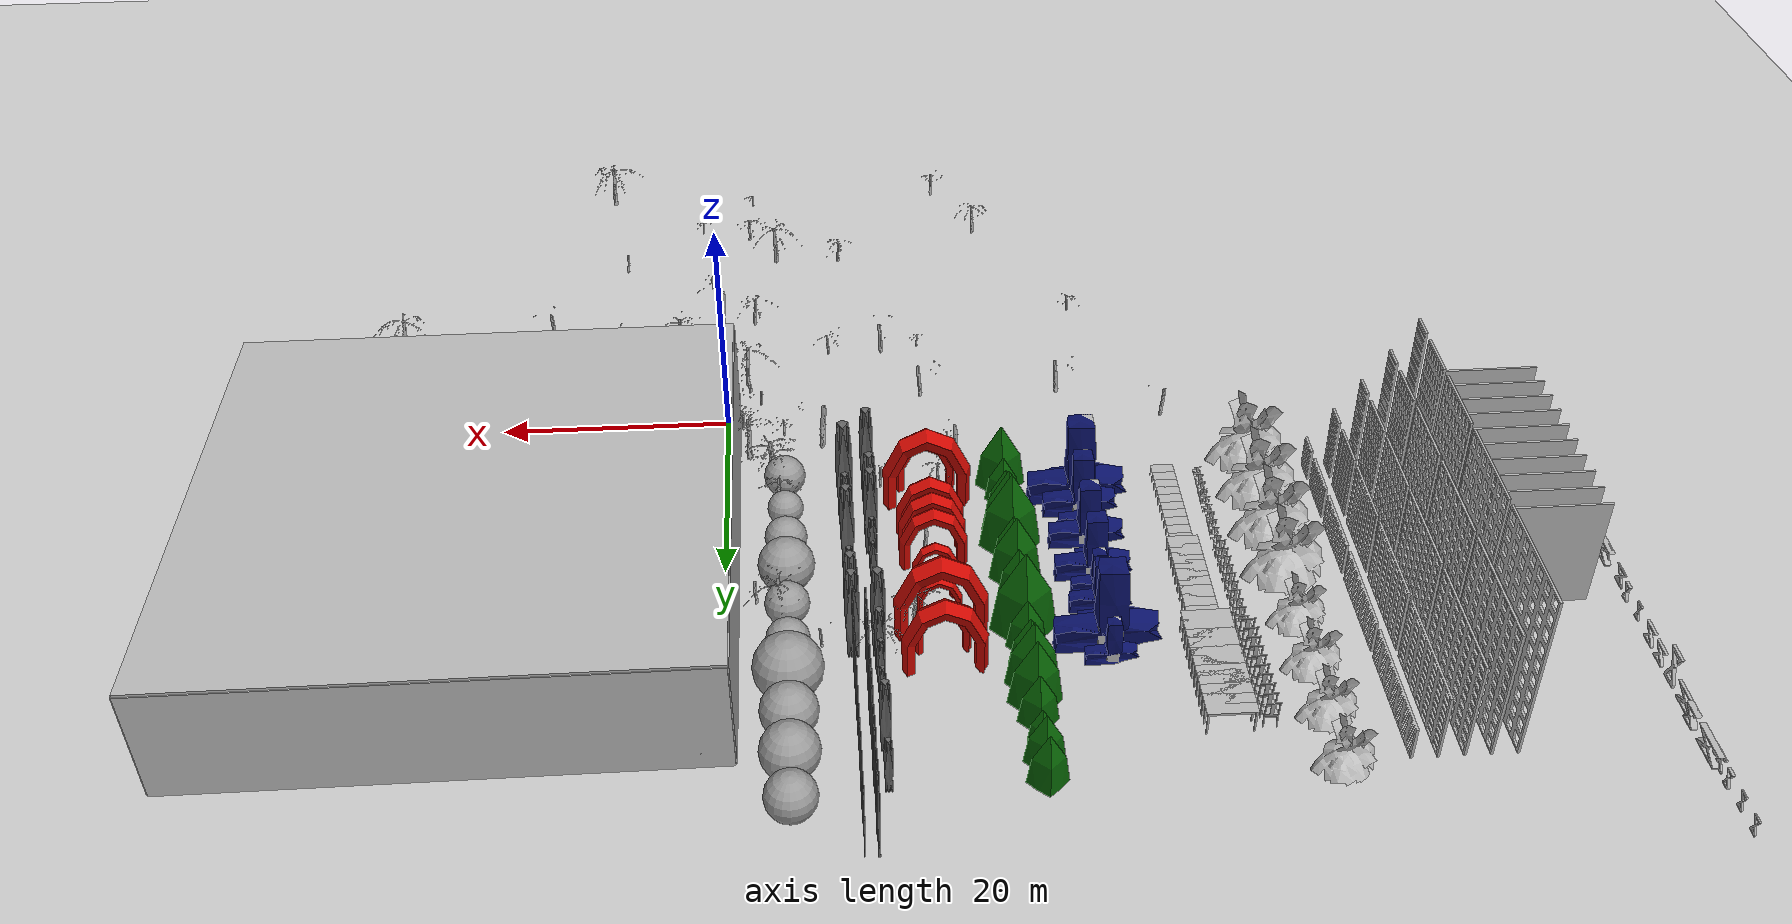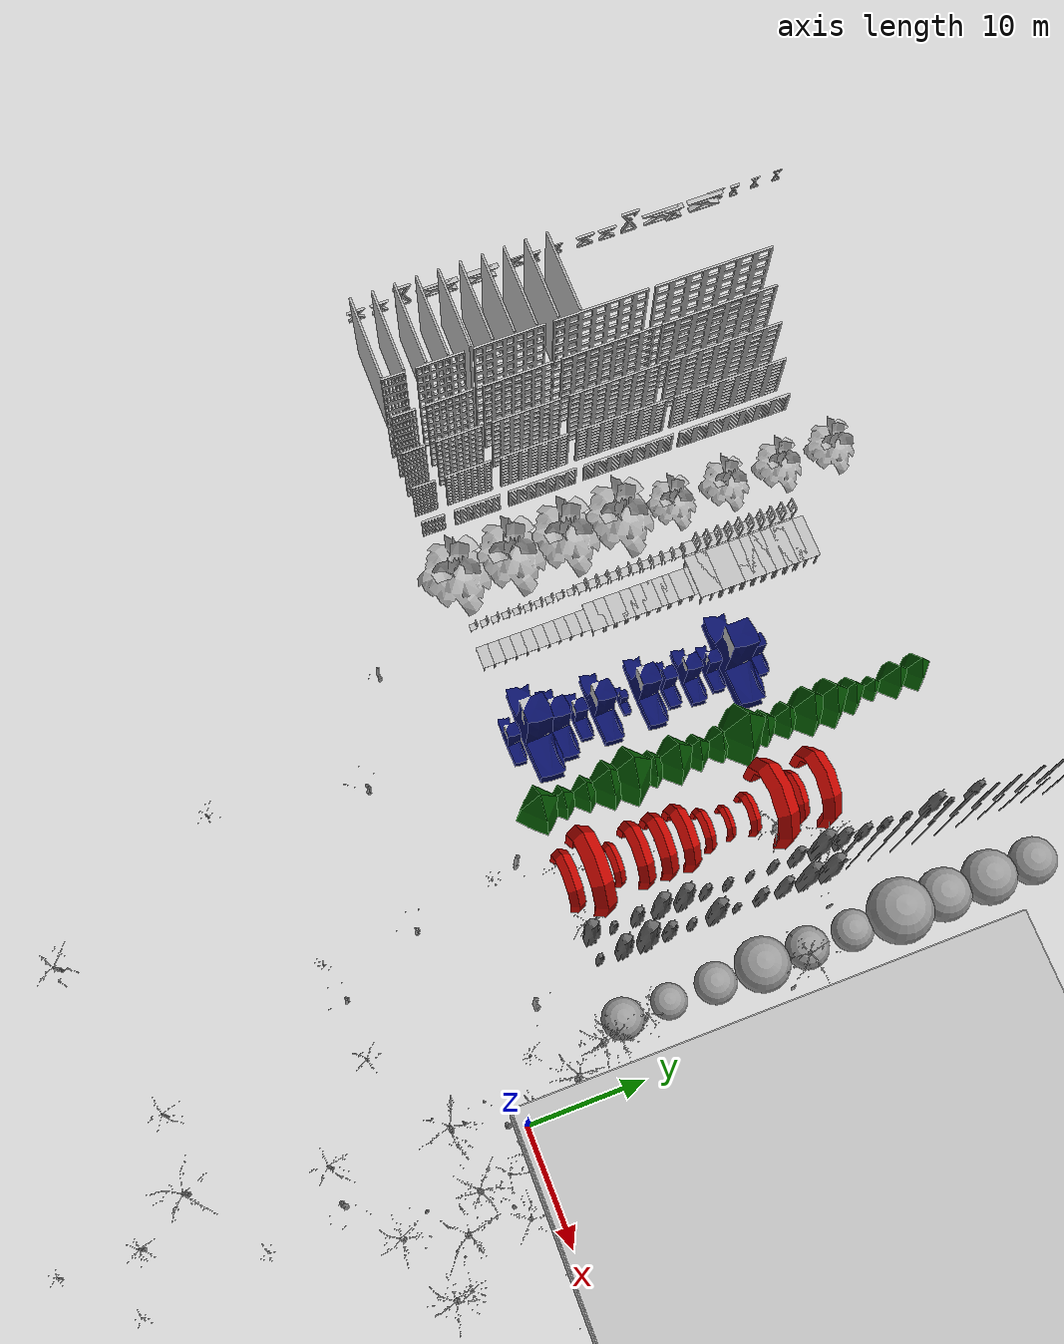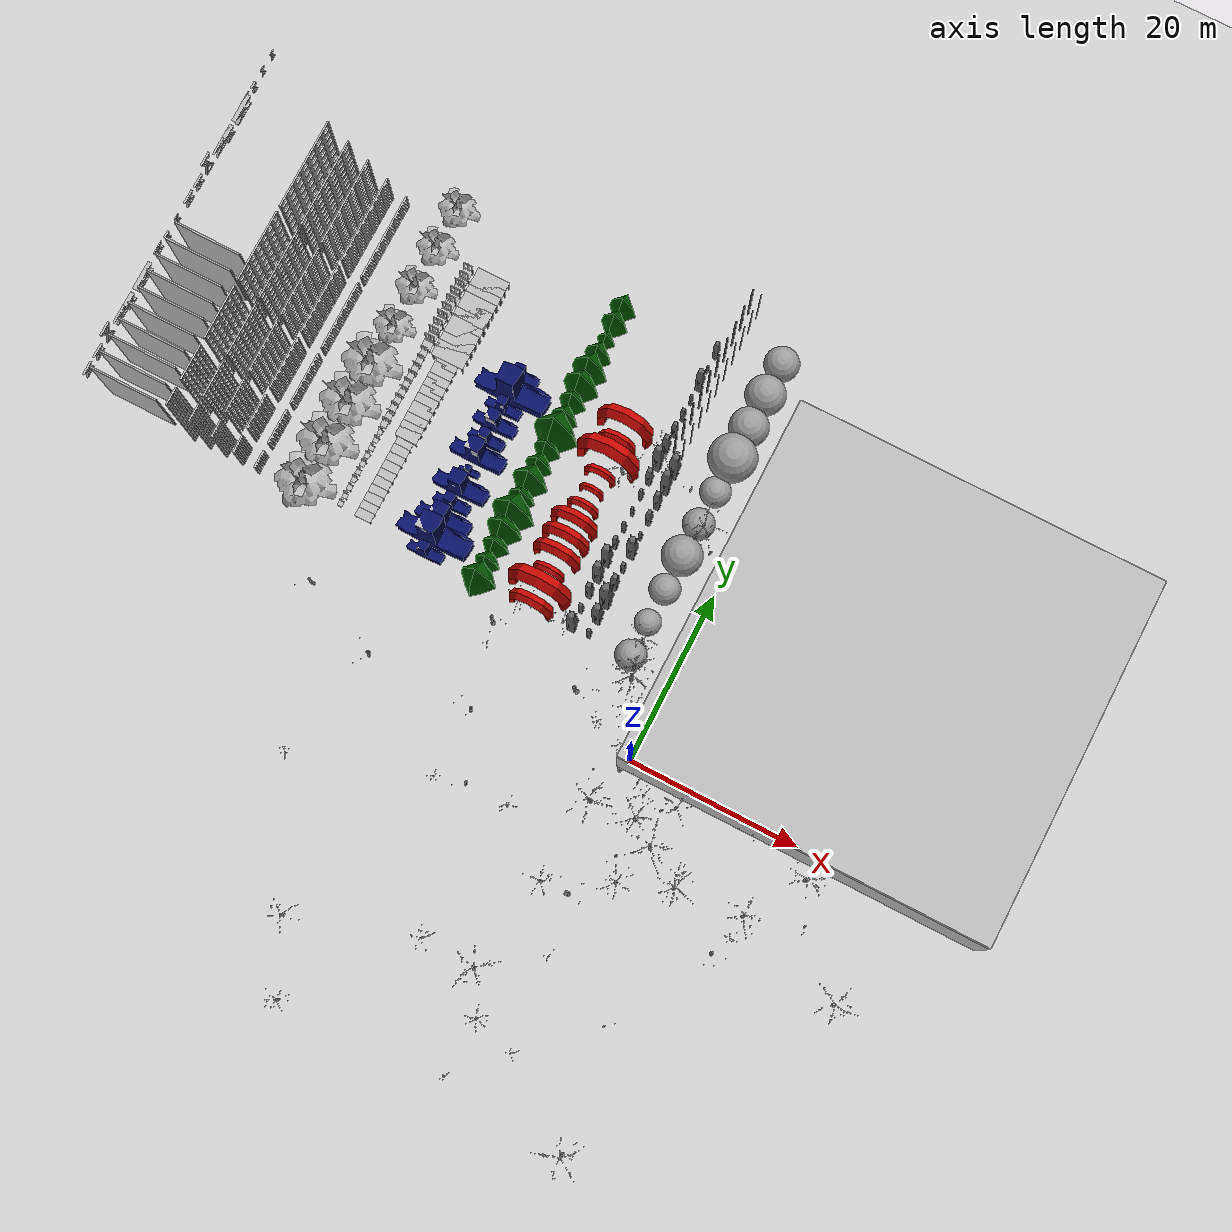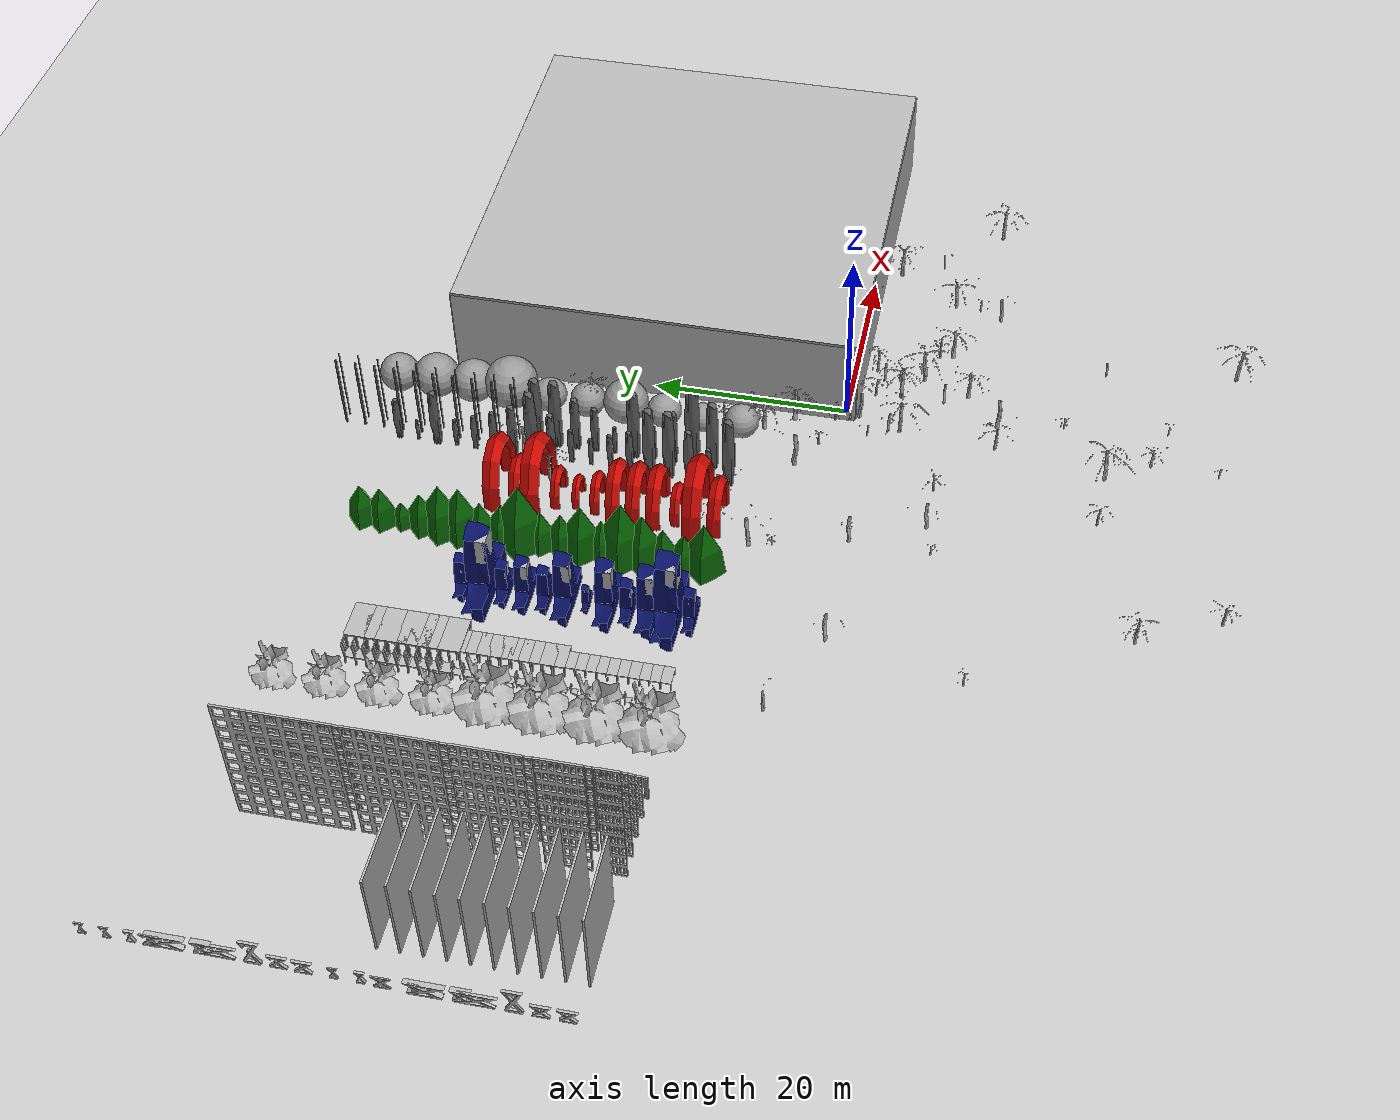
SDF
<sdf version="1.6">
 <world name="default">
  <model name="ground_plane">
   <static>1</static>
   <link name="link">
    <collision name="collision">
     <geometry><plane><normal>0 0 1</normal><size>1000 1000</size></plane></geometry>
     <surface>
      <contact><collide_bitmask>65535</collide_bitmask></contact>
      <friction><ode><mu>100</mu><mu2>50</mu2></ode></friction>
     </surface>
    </collision>
    <visual name="visual">
     <cast_shadows>0</cast_shadows>
     <geometry><plane><normal>0 0 1</normal><size>1000 1000</size></plane></geometry>
     <material>
      <script><uri>file://media/materials/scripts/gazebo.material</uri><name>Gazebo/Grey</name></script>
     </material>
    </visual>
   </link>
  </model>
  <light name="sun" type="directional">
   <pose>0 0 10 0 -0 0</pose>
   <diffuse>0.8 0.8 0.8 1</diffuse>
   <specular>0.2 0.2 0.2 1</specular>
   <attenuation>
    <range>1000</range>
    <constant>0.9</constant>
    <linear>0.01</linear>
    <quadratic>0.001</quadratic>
   </attenuation>
   <direction>-0.5 0.1 -0.9</direction>
  </light>
  <scene><shadows>0</shadows><ambient>0.4 0.4 0.4 1</ambient><background>0.7 0.7 0.7 1</background></scene>
  <plugin name="ros_interface_plugin" filename="librotors_gazebo_ros_interface_plugin.so"/>
  <physics name="default_physics" default="0" type="ode">
   <max_step_size>0.005</max_step_size>
   <real_time_factor>10</real_time_factor>
   <real_time_update_rate>600</real_time_update_rate>
   <ode>
    <solver>
     <type>quick</type>
     <iters>1000</iters>
     <sor>1.3</sor>
     <use_dynamic_moi_rescaling>0</use_dynamic_moi_rescaling>
    </solver>
    <constraints>
     <cfm>0</cfm>
     <erp>0.2</erp>
     <contact_max_correcting_vel>100</contact_max_correcting_vel>
     <contact_surface_layer>0.001</contact_surface_layer>
    </constraints>
   </ode>
  </physics>
  <gravity>0 0 -9.8</gravity>
  <magnetic_field>6e-06 2.3e-05 -4.2e-05</magnetic_field>
  <atmosphere type="adiabatic"/>
  <audio><device>default</device></audio>
  <spherical_coordinates>
   <surface_model>EARTH_WGS84</surface_model>
   <latitude_deg>0</latitude_deg>
   <longitude_deg>0</longitude_deg>
   <elevation>0</elevation>
   <heading_deg>0</heading_deg>
  </spherical_coordinates>
  <model name="wall_top">
   <static>1</static>
   <link name="link">
    <pose>0 0 0.1 0 0 0</pose>
    <collision name="collision"><geometry><box><size>42.0 42.0 0.2</size></box></geometry></collision>
    <visual name="visual">
     <cast_shadows>0</cast_shadows>
     <geometry><box><size>42.0 42.0 0.2</size></box></geometry>
    </visual>
   </link>
   <pose>20.0 20.0 10.0 0 0 0</pose>
  </model>
  <model name="Simple Block_6">
   <pose>-30 22 0 0 -0 0</pose>
   <static>1</static>
   <link name="link">
    <collision name="collision">
     <geometry>
      <mesh><uri>model://Simple Block/meshes/Simple Block.dae</uri><scale>0.75 0.75 0.75</scale></mesh>
     </geometry>
    </collision>
    <visual name="visual">
     <geometry>
      <mesh><uri>model://Simple Block/meshes/Simple Block.dae</uri><scale>0.75 0.75 0.75</scale></mesh>
     </geometry>
    </visual>
   </link>
  </model>
  <model name="Simple Block_0">
   <pose>-30 10 0 0 -0 0</pose>
   <static>1</static>
   <link name="link">
    <collision name="collision">
     <geometry>
      <mesh><uri>model://Simple Block/meshes/Simple Block.dae</uri><scale>0.5 0.5 0.5</scale></mesh>
     </geometry>
    </collision>
    <visual name="visual">
     <geometry>
      <mesh><uri>model://Simple Block/meshes/Simple Block.dae</uri><scale>0.5 0.5 0.5</scale></mesh>
     </geometry>
    </visual>
   </link>
  </model>
  <model name="Simple Block_1">
   <pose>-30 12 0 0 -0 0</pose>
   <static>1</static>
   <link name="link">
    <collision name="collision">
     <geometry><mesh><uri>model://Simple Block/meshes/Simple Block.dae</uri></mesh></geometry>
    </collision>
    <visual name="visual">
     <geometry><mesh><uri>model://Simple Block/meshes/Simple Block.dae</uri></mesh></geometry>
    </visual>
   </link>
  </model>
  <model name="Simple Block_2">
   <pose>-30 14 0 0 -0 0</pose>
   <static>1</static>
   <link name="link">
    <collision name="collision">
     <geometry>
      <mesh><uri>model://Simple Block/meshes/Simple Block.dae</uri><scale>0.75 0.75 0.75</scale></mesh>
     </geometry>
    </collision>
    <visual name="visual">
     <geometry>
      <mesh><uri>model://Simple Block/meshes/Simple Block.dae</uri><scale>0.75 0.75 0.75</scale></mesh>
     </geometry>
    </visual>
   </link>
  </model>
  <model name="Simple Block_3">
   <pose>-30 16 0 0 -0 0</pose>
   <static>1</static>
   <link name="link">
    <collision name="collision">
     <geometry>
      <mesh><uri>model://Simple Block/meshes/Simple Block.dae</uri><scale>0.5 0.5 0.5</scale></mesh>
     </geometry>
    </collision>
    <visual name="visual">
     <geometry>
      <mesh><uri>model://Simple Block/meshes/Simple Block.dae</uri><scale>0.5 0.5 0.5</scale></mesh>
     </geometry>
    </visual>
   </link>
  </model>
  <model name="Simple Block_4">
   <pose>-30 18 0 0 -0 0</pose>
   <static>1</static>
   <link name="link">
    <collision name="collision">
     <geometry>
      <mesh><uri>model://Simple Block/meshes/Simple Block.dae</uri><scale>0.75 0.75 0.75</scale></mesh>
     </geometry>
    </collision>
    <visual name="visual">
     <geometry>
      <mesh><uri>model://Simple Block/meshes/Simple Block.dae</uri><scale>0.75 0.75 0.75</scale></mesh>
     </geometry>
    </visual>
   </link>
  </model>
  <model name="Simple Block_5">
   <pose>-30 20 0 0 -0 0</pose>
   <static>1</static>
   <link name="link">
    <collision name="collision">
     <geometry>
      <mesh><uri>model://Simple Block/meshes/Simple Block.dae</uri><scale>0.3 0.3 0.3</scale></mesh>
     </geometry>
    </collision>
    <visual name="visual">
     <geometry>
      <mesh><uri>model://Simple Block/meshes/Simple Block.dae</uri><scale>0.3 0.3 0.3</scale></mesh>
     </geometry>
    </visual>
   </link>
  </model>
  <model name="Simple Pyramid_11">
   <pose>-23.5 32 0 0 -0 0</pose>
   <static>1</static>
   <link name="link">
    <collision name="collision">
     <geometry>
      <mesh><uri>model://Simple Pyramid/meshes/Simple Pyramid.dae</uri><scale>0.75 0.75 0.75</scale></mesh>
     </geometry>
    </collision>
    <visual name="visual">
     <geometry>
      <mesh><uri>model://Simple Pyramid/meshes/Simple Pyramid.dae</uri><scale>0.75 0.75 0.75</scale></mesh>
     </geometry>
    </visual>
   </link>
  </model>
  <model name="Simple Pyramid_0">
   <pose>-23.5 10 0 0 -0 0</pose>
   <static>1</static>
   <link name="link">
    <collision name="collision">
     <geometry><mesh><uri>model://Simple Pyramid/meshes/Simple Pyramid.dae</uri></mesh></geometry>
    </collision>
    <visual name="visual">
     <geometry><mesh><uri>model://Simple Pyramid/meshes/Simple Pyramid.dae</uri></mesh></geometry>
    </visual>
   </link>
  </model>
  <model name="Simple Pyramid_1">
   <pose>-23.5 12 0 0 -0 0</pose>
   <static>1</static>
   <link name="link">
    <collision name="collision">
     <geometry>
      <mesh><uri>model://Simple Pyramid/meshes/Simple Pyramid.dae</uri><scale>0.7 0.7 0.7</scale></mesh>
     </geometry>
    </collision>
    <visual name="visual">
     <geometry>
      <mesh><uri>model://Simple Pyramid/meshes/Simple Pyramid.dae</uri><scale>0.7 0.7 0.7</scale></mesh>
     </geometry>
    </visual>
   </link>
  </model>
  <model name="Simple Pyramid_2">
   <pose>-23.5 14 0 0 -0 0</pose>
   <static>1</static>
   <link name="link">
    <collision name="collision">
     <geometry>
      <mesh><uri>model://Simple Pyramid/meshes/Simple Pyramid.dae</uri><scale>0.75 0.75 0.75</scale></mesh>
     </geometry>
    </collision>
    <visual name="visual">
     <geometry>
      <mesh><uri>model://Simple Pyramid/meshes/Simple Pyramid.dae</uri><scale>0.75 0.75 0.75</scale></mesh>
     </geometry>
    </visual>
   </link>
  </model>
  <model name="Simple Pyramid_3">
   <pose>-23.5 16 0 0 -0 0</pose>
   <static>1</static>
   <link name="link">
    <collision name="collision">
     <geometry><mesh><uri>model://Simple Pyramid/meshes/Simple Pyramid.dae</uri></mesh></geometry>
    </collision>
    <visual name="visual">
     <geometry><mesh><uri>model://Simple Pyramid/meshes/Simple Pyramid.dae</uri></mesh></geometry>
    </visual>
   </link>
  </model>
  <model name="Simple Pyramid_4">
   <pose>-23.5 18 0 0 -0 0</pose>
   <static>1</static>
   <link name="link">
    <collision name="collision">
     <geometry>
      <mesh><uri>model://Simple Pyramid/meshes/Simple Pyramid.dae</uri><scale>1.2 1.2 1.2</scale></mesh>
     </geometry>
    </collision>
    <visual name="visual">
     <geometry>
      <mesh><uri>model://Simple Pyramid/meshes/Simple Pyramid.dae</uri><scale>1.2 1.2 1.2</scale></mesh>
     </geometry>
    </visual>
   </link>
  </model>
  <model name="Simple Pyramid_5">
   <pose>-23.5 20 0 0 -0 0</pose>
   <static>1</static>
   <link name="link">
    <collision name="collision">
     <geometry>
      <mesh><uri>model://Simple Pyramid/meshes/Simple Pyramid.dae</uri><scale>0.75 0.75 0.75</scale></mesh>
     </geometry>
    </collision>
    <visual name="visual">
     <geometry>
      <mesh><uri>model://Simple Pyramid/meshes/Simple Pyramid.dae</uri><scale>0.75 0.75 0.75</scale></mesh>
     </geometry>
    </visual>
   </link>
  </model>
  <model name="Simple Pyramid_6">
   <pose>-23.5 22 0 0 -0 0</pose>
   <static>1</static>
   <link name="link">
    <collision name="collision">
     <geometry><mesh><uri>model://Simple Pyramid/meshes/Simple Pyramid.dae</uri></mesh></geometry>
    </collision>
    <visual name="visual">
     <geometry><mesh><uri>model://Simple Pyramid/meshes/Simple Pyramid.dae</uri></mesh></geometry>
    </visual>
   </link>
  </model>
  <model name="Simple Pyramid_7">
   <pose>-23.5 24 0 0 -0 0</pose>
   <static>1</static>
   <link name="link">
    <collision name="collision">
     <geometry>
      <mesh><uri>model://Simple Pyramid/meshes/Simple Pyramid.dae</uri><scale>0.75 0.75 0.75</scale></mesh>
     </geometry>
    </collision>
    <visual name="visual">
     <geometry>
      <mesh><uri>model://Simple Pyramid/meshes/Simple Pyramid.dae</uri><scale>0.75 0.75 0.75</scale></mesh>
     </geometry>
    </visual>
   </link>
  </model>
  <model name="Simple Pyramid_8">
   <pose>-23.5 26 0 0 -0 0</pose>
   <static>1</static>
   <link name="link">
    <collision name="collision">
     <geometry>
      <mesh><uri>model://Simple Pyramid/meshes/Simple Pyramid.dae</uri><scale>0.75 0.75 0.75</scale></mesh>
     </geometry>
    </collision>
    <visual name="visual">
     <geometry>
      <mesh><uri>model://Simple Pyramid/meshes/Simple Pyramid.dae</uri><scale>0.75 0.75 0.75</scale></mesh>
     </geometry>
    </visual>
   </link>
  </model>
  <model name="Simple Pyramid_9">
   <pose>-23.5 28 0 0 -0 0</pose>
   <static>1</static>
   <link name="link">
    <collision name="collision">
     <geometry>
      <mesh><uri>model://Simple Pyramid/meshes/Simple Pyramid.dae</uri><scale>1.25 1.25 1.25</scale></mesh>
     </geometry>
    </collision>
    <visual name="visual">
     <geometry>
      <mesh><uri>model://Simple Pyramid/meshes/Simple Pyramid.dae</uri><scale>1.25 1.25 1.25</scale></mesh>
     </geometry>
    </visual>
   </link>
  </model>
  <model name="Simple Pyramid_10">
   <pose>-23.5 30 0 0 -0 0</pose>
   <static>1</static>
   <link name="link">
    <collision name="collision">
     <geometry>
      <mesh><uri>model://Simple Pyramid/meshes/Simple Pyramid.dae</uri><scale>0.75 0.75 0.75</scale></mesh>
     </geometry>
    </collision>
    <visual name="visual">
     <geometry>
      <mesh><uri>model://Simple Pyramid/meshes/Simple Pyramid.dae</uri><scale>0.75 0.75 0.75</scale></mesh>
     </geometry>
    </visual>
   </link>
  </model>
  <model name="Simple U_7">
   <pose>-17 24 0 0 -0 0</pose>
   <static>1</static>
   <link name="link">
    <collision name="collision">
     <geometry><mesh><uri>model://Simple U/meshes/Simple U.dae</uri><scale>0.4 0.4 0.4</scale></mesh></geometry>
    </collision>
    <visual name="visual">
     <geometry><mesh><uri>model://Simple U/meshes/Simple U.dae</uri><scale>0.4 0.4 0.4</scale></mesh></geometry>
    </visual>
   </link>
  </model>
  <model name="Simple U_0">
   <pose>-17 10 0 0 -0 0</pose>
   <static>1</static>
   <link name="link">
    <collision name="collision">
     <geometry><mesh><uri>model://Simple U/meshes/Simple U.dae</uri><scale>0.7 0.7 0.7</scale></mesh></geometry>
    </collision>
    <visual name="visual">
     <geometry><mesh><uri>model://Simple U/meshes/Simple U.dae</uri><scale>0.7 0.7 0.7</scale></mesh></geometry>
    </visual>
   </link>
  </model>
  <model name="Simple U_1">
   <pose>-17 12 0 0 -0 0</pose>
   <static>1</static>
   <link name="link">
    <collision name="collision">
     <geometry><mesh><uri>model://Simple U/meshes/Simple U.dae</uri></mesh></geometry>
    </collision>
    <visual name="visual">
     <geometry><mesh><uri>model://Simple U/meshes/Simple U.dae</uri></mesh></geometry>
    </visual>
   </link>
  </model>
  <model name="Simple U_2">
   <pose>-17 14 0 0 -0 0</pose>
   <static>1</static>
   <link name="link">
    <collision name="collision">
     <geometry><mesh><uri>model://Simple U/meshes/Simple U.dae</uri><scale>0.5 0.5 0.5</scale></mesh></geometry>
    </collision>
    <visual name="visual">
     <geometry><mesh><uri>model://Simple U/meshes/Simple U.dae</uri><scale>0.5 0.5 0.5</scale></mesh></geometry>
    </visual>
   </link>
  </model>
  <model name="Simple U_3">
   <pose>-17 16 0 0 -0 0</pose>
   <static>1</static>
   <link name="link">
    <collision name="collision">
     <geometry><mesh><uri>model://Simple U/meshes/Simple U.dae</uri><scale>0.75 0.75 0.75</scale></mesh></geometry>
    </collision>
    <visual name="visual">
     <geometry><mesh><uri>model://Simple U/meshes/Simple U.dae</uri><scale>0.75 0.75 0.75</scale></mesh></geometry>
    </visual>
   </link>
  </model>
  <model name="Simple U_4">
   <pose>-17 18 0 0 -0 0</pose>
   <static>1</static>
   <link name="link">
    <collision name="collision">
     <geometry><mesh><uri>model://Simple U/meshes/Simple U.dae</uri><scale>0.75 0.75 0.75</scale></mesh></geometry>
    </collision>
    <visual name="visual">
     <geometry><mesh><uri>model://Simple U/meshes/Simple U.dae</uri><scale>0.75 0.75 0.75</scale></mesh></geometry>
    </visual>
   </link>
  </model>
  <model name="Simple U_5">
   <pose>-17 20 0 0 -0 0</pose>
   <static>1</static>
   <link name="link">
    <collision name="collision">
     <geometry><mesh><uri>model://Simple U/meshes/Simple U.dae</uri><scale>0.75 0.75 0.75</scale></mesh></geometry>
    </collision>
    <visual name="visual">
     <geometry><mesh><uri>model://Simple U/meshes/Simple U.dae</uri><scale>0.75 0.75 0.75</scale></mesh></geometry>
    </visual>
   </link>
  </model>
  <model name="Simple U_6">
   <pose>-17 22 0 0 -0 0</pose>
   <static>1</static>
   <link name="link">
    <collision name="collision">
     <geometry><mesh><uri>model://Simple U/meshes/Simple U.dae</uri><scale>0.5 0.5 0.5</scale></mesh></geometry>
    </collision>
    <visual name="visual">
     <geometry><mesh><uri>model://Simple U/meshes/Simple U.dae</uri><scale>0.5 0.5 0.5</scale></mesh></geometry>
    </visual>
   </link>
  </model>
  <model name="Simple Stone_25">
   <pose>-10 24 0 0 -0 0</pose>
   <static>1</static>
   <link name="link">
    <collision name="collision">
     <geometry>
      <mesh><uri>model://Simple Stone/meshes/Simple Stone.dae</uri><scale>0.66 0.66 0.66</scale></mesh>
     </geometry>
    </collision>
    <visual name="visual">
     <geometry>
      <mesh><uri>model://Simple Stone/meshes/Simple Stone.dae</uri><scale>0.66 0.66 0.66</scale></mesh>
     </geometry>
    </visual>
   </link>
  </model>
  <model name="Simple Stone_0">
   <pose>-12 10 0 0 -0 0</pose>
   <static>1</static>
   <link name="link">
    <collision name="collision">
     <geometry><mesh><uri>model://Simple Stone/meshes/Simple Stone.dae</uri></mesh></geometry>
    </collision>
    <visual name="visual">
     <geometry><mesh><uri>model://Simple Stone/meshes/Simple Stone.dae</uri></mesh></geometry>
    </visual>
   </link>
  </model>
  <model name="Simple Stone_1">
   <pose>-12 12 0 0 -0 0</pose>
   <static>1</static>
   <link name="link">
    <collision name="collision">
     <geometry>
      <mesh><uri>model://Simple Stone/meshes/Simple Stone.dae</uri><scale>0.5 0.5 0.5</scale></mesh>
     </geometry>
    </collision>
    <visual name="visual">
     <geometry>
      <mesh><uri>model://Simple Stone/meshes/Simple Stone.dae</uri><scale>0.5 0.5 0.5</scale></mesh>
     </geometry>
    </visual>
   </link>
  </model>
  <model name="Simple Stone_2">
   <pose>-12 14 0 0 -0 0</pose>
   <static>1</static>
   <link name="link">
    <collision name="collision">
     <geometry>
      <mesh><uri>model://Simple Stone/meshes/Simple Stone.dae</uri><scale>0.75 0.75 0.75</scale></mesh>
     </geometry>
    </collision>
    <visual name="visual">
     <geometry>
      <mesh><uri>model://Simple Stone/meshes/Simple Stone.dae</uri><scale>0.75 0.75 0.75</scale></mesh>
     </geometry>
    </visual>
   </link>
  </model>
  <model name="Simple Stone_3">
   <pose>-12 16 0 0 -0 0</pose>
   <static>1</static>
   <link name="link">
    <collision name="collision">
     <geometry><mesh><uri>model://Simple Stone/meshes/Simple Stone.dae</uri></mesh></geometry>
    </collision>
    <visual name="visual">
     <geometry><mesh><uri>model://Simple Stone/meshes/Simple Stone.dae</uri></mesh></geometry>
    </visual>
   </link>
  </model>
  <model name="Simple Stone_4">
   <pose>-12 18 0 0 -0 0</pose>
   <static>1</static>
   <link name="link">
    <collision name="collision">
     <geometry><mesh><uri>model://Simple Stone/meshes/Simple Stone.dae</uri></mesh></geometry>
    </collision>
    <visual name="visual">
     <geometry><mesh><uri>model://Simple Stone/meshes/Simple Stone.dae</uri></mesh></geometry>
    </visual>
   </link>
  </model>
  <model name="Simple Stone_5">
   <pose>-12 20 0 0 -0 0</pose>
   <static>1</static>
   <link name="link">
    <collision name="collision">
     <geometry>
      <mesh><uri>model://Simple Stone/meshes/Simple Stone.dae</uri><scale>0.6 0.6 0.6</scale></mesh>
     </geometry>
    </collision>
    <visual name="visual">
     <geometry>
      <mesh><uri>model://Simple Stone/meshes/Simple Stone.dae</uri><scale>0.6 0.6 0.6</scale></mesh>
     </geometry>
    </visual>
   </link>
  </model>
  <model name="Simple Stone_6">
   <pose>-12 22 0 0 -0 0</pose>
   <static>1</static>
   <link name="link">
    <collision name="collision">
     <geometry>
      <mesh><uri>model://Simple Stone/meshes/Simple Stone.dae</uri><scale>0.5 0.5 0.5</scale></mesh>
     </geometry>
    </collision>
    <visual name="visual">
     <geometry>
      <mesh><uri>model://Simple Stone/meshes/Simple Stone.dae</uri><scale>0.5 0.5 0.5</scale></mesh>
     </geometry>
    </visual>
   </link>
  </model>
  <model name="Simple Stone_7">
   <pose>-12 24 0 0 -0 0</pose>
   <static>1</static>
   <link name="link">
    <collision name="collision">
     <geometry>
      <mesh><uri>model://Simple Stone/meshes/Simple Stone.dae</uri><scale>0.4 0.4 0.4</scale></mesh>
     </geometry>
    </collision>
    <visual name="visual">
     <geometry>
      <mesh><uri>model://Simple Stone/meshes/Simple Stone.dae</uri><scale>0.4 0.4 0.4</scale></mesh>
     </geometry>
    </visual>
   </link>
  </model>
  <model name="Simple Stone_8">
   <pose>-12 26 0 0 -0 0</pose>
   <static>1</static>
   <link name="link">
    <collision name="collision">
     <geometry>
      <mesh><uri>model://Simple Stone/meshes/Simple Stone.dae</uri><scale>0.5 0.5 0.5</scale></mesh>
     </geometry>
    </collision>
    <visual name="visual">
     <geometry>
      <mesh><uri>model://Simple Stone/meshes/Simple Stone.dae</uri><scale>0.5 0.5 0.5</scale></mesh>
     </geometry>
    </visual>
   </link>
  </model>
  <model name="Simple Stone_9">
   <pose>-12 28 0 0 -0 0</pose>
   <static>1</static>
   <link name="link">
    <collision name="collision">
     <geometry>
      <mesh><uri>model://Simple Stone/meshes/Simple Stone.dae</uri><scale>0.7 0.7 0.7</scale></mesh>
     </geometry>
    </collision>
    <visual name="visual">
     <geometry>
      <mesh><uri>model://Simple Stone/meshes/Simple Stone.dae</uri><scale>0.7 0.7 0.7</scale></mesh>
     </geometry>
    </visual>
   </link>
  </model>
  <model name="Simple Stone_10">
   <pose>-12 30 0 0 -0 0</pose>
   <static>1</static>
   <link name="link">
    <collision name="collision">
     <geometry><mesh><uri>model://Simple Stone/meshes/Simple Stone.dae</uri></mesh></geometry>
    </collision>
    <visual name="visual">
     <geometry><mesh><uri>model://Simple Stone/meshes/Simple Stone.dae</uri></mesh></geometry>
    </visual>
   </link>
  </model>
  <model name="Simple Stone_11">
   <pose>-12 32 0 0 -0 0</pose>
   <static>1</static>
   <link name="link">
    <collision name="collision">
     <geometry>
      <mesh><uri>model://Simple Stone/meshes/Simple Stone.dae</uri><scale>0.75 0.75 0.75</scale></mesh>
     </geometry>
    </collision>
    <visual name="visual">
     <geometry>
      <mesh><uri>model://Simple Stone/meshes/Simple Stone.dae</uri><scale>0.75 0.75 0.75</scale></mesh>
     </geometry>
    </visual>
   </link>
  </model>
  <model name="Simple Stone_12">
   <pose>-12 34 0 0 -0 0</pose>
   <static>1</static>
   <link name="link">
    <collision name="collision">
     <geometry>
      <mesh><uri>model://Simple Stone/meshes/Simple Stone.dae</uri><scale>0.6 0.6 0.6</scale></mesh>
     </geometry>
    </collision>
    <visual name="visual">
     <geometry>
      <mesh><uri>model://Simple Stone/meshes/Simple Stone.dae</uri><scale>0.6 0.6 0.6</scale></mesh>
     </geometry>
    </visual>
   </link>
  </model>
  <model name="Simple Stone_13">
   <pose>-12 36 0 0 -0 0</pose>
   <static>1</static>
   <link name="link">
    <collision name="collision">
     <geometry>
      <mesh><uri>model://Simple Stone/meshes/Simple Stone.dae</uri><scale>0.5 0.5 0.5</scale></mesh>
     </geometry>
    </collision>
    <visual name="visual">
     <geometry>
      <mesh><uri>model://Simple Stone/meshes/Simple Stone.dae</uri><scale>0.5 0.5 0.5</scale></mesh>
     </geometry>
    </visual>
   </link>
  </model>
  <model name="Simple Stone_14">
   <pose>-12 38 0 0 -0 0</pose>
   <static>1</static>
   <link name="link">
    <collision name="collision">
     <geometry>
      <mesh><uri>model://Simple Stone/meshes/Simple Stone.dae</uri><scale>0.4 0.4 0.4</scale></mesh>
     </geometry>
    </collision>
    <visual name="visual">
     <geometry>
      <mesh><uri>model://Simple Stone/meshes/Simple Stone.dae</uri><scale>0.4 0.4 0.4</scale></mesh>
     </geometry>
    </visual>
   </link>
  </model>
  <model name="Simple Stone_15">
   <pose>-12 40 0 0 -0 0</pose>
   <static>1</static>
   <link name="link">
    <collision name="collision">
     <geometry>
      <mesh><uri>model://Simple Stone/meshes/Simple Stone.dae</uri><scale>0.8 0.8 0.8</scale></mesh>
     </geometry>
    </collision>
    <visual name="visual">
     <geometry>
      <mesh><uri>model://Simple Stone/meshes/Simple Stone.dae</uri><scale>0.8 0.8 0.8</scale></mesh>
     </geometry>
    </visual>
   </link>
  </model>
  <model name="Simple Stone_16">
   <pose>-12 42 0 0 -0 0</pose>
   <static>1</static>
   <link name="link">
    <collision name="collision">
     <geometry>
      <mesh><uri>model://Simple Stone/meshes/Simple Stone.dae</uri><scale>0.3 0.3 0.3</scale></mesh>
     </geometry>
    </collision>
    <visual name="visual">
     <geometry>
      <mesh><uri>model://Simple Stone/meshes/Simple Stone.dae</uri><scale>0.3 0.3 0.3</scale></mesh>
     </geometry>
    </visual>
   </link>
  </model>
  <model name="Simple Stone_17">
   <pose>-12 44 0 0 -0 0</pose>
   <static>1</static>
   <link name="link">
    <collision name="collision">
     <geometry>
      <mesh><uri>model://Simple Stone/meshes/Simple Stone.dae</uri><scale>0.6 0.6 0.6</scale></mesh>
     </geometry>
    </collision>
    <visual name="visual">
     <geometry>
      <mesh><uri>model://Simple Stone/meshes/Simple Stone.dae</uri><scale>0.6 0.6 0.6</scale></mesh>
     </geometry>
    </visual>
   </link>
  </model>
  <model name="Simple Stone_18">
   <pose>-10 10 0 0 -0 0</pose>
   <static>1</static>
   <link name="link">
    <collision name="collision">
     <geometry>
      <mesh><uri>model://Simple Stone/meshes/Simple Stone.dae</uri><scale>0.5 0.5 0.5</scale></mesh>
     </geometry>
    </collision>
    <visual name="visual">
     <geometry>
      <mesh><uri>model://Simple Stone/meshes/Simple Stone.dae</uri><scale>0.5 0.5 0.5</scale></mesh>
     </geometry>
    </visual>
   </link>
  </model>
  <model name="Simple Stone_19">
   <pose>-10 12 0 0 -0 0</pose>
   <static>1</static>
   <link name="link">
    <collision name="collision">
     <geometry><mesh><uri>model://Simple Stone/meshes/Simple Stone.dae</uri></mesh></geometry>
    </collision>
    <visual name="visual">
     <geometry><mesh><uri>model://Simple Stone/meshes/Simple Stone.dae</uri></mesh></geometry>
    </visual>
   </link>
  </model>
  <model name="Simple Stone_20">
   <pose>-10 14 0 0 -0 0</pose>
   <static>1</static>
   <link name="link">
    <collision name="collision">
     <geometry>
      <mesh><uri>model://Simple Stone/meshes/Simple Stone.dae</uri><scale>1.2 1.2 1.2</scale></mesh>
     </geometry>
    </collision>
    <visual name="visual">
     <geometry>
      <mesh><uri>model://Simple Stone/meshes/Simple Stone.dae</uri><scale>1.2 1.2 1.2</scale></mesh>
     </geometry>
    </visual>
   </link>
  </model>
  <model name="Simple Stone_21">
   <pose>-10 16 0 0 -0 0</pose>
   <static>1</static>
   <link name="link">
    <collision name="collision">
     <geometry>
      <mesh><uri>model://Simple Stone/meshes/Simple Stone.dae</uri><scale>0.77 0.77 0.77</scale></mesh>
     </geometry>
    </collision>
    <visual name="visual">
     <geometry>
      <mesh><uri>model://Simple Stone/meshes/Simple Stone.dae</uri><scale>0.77 0.77 0.77</scale></mesh>
     </geometry>
    </visual>
   </link>
  </model>
  <model name="Simple Stone_22">
   <pose>-10 18 0 0 -0 0</pose>
   <static>1</static>
   <link name="link">
    <collision name="collision">
     <geometry>
      <mesh><uri>model://Simple Stone/meshes/Simple Stone.dae</uri><scale>0.5 0.5 0.5</scale></mesh>
     </geometry>
    </collision>
    <visual name="visual">
     <geometry>
      <mesh><uri>model://Simple Stone/meshes/Simple Stone.dae</uri><scale>0.5 0.5 0.5</scale></mesh>
     </geometry>
    </visual>
   </link>
  </model>
  <model name="Simple Stone_23">
   <pose>-10 20 0 0 -0 0</pose>
   <static>1</static>
   <link name="link">
    <collision name="collision">
     <geometry><mesh><uri>model://Simple Stone/meshes/Simple Stone.dae</uri></mesh></geometry>
    </collision>
    <visual name="visual">
     <geometry><mesh><uri>model://Simple Stone/meshes/Simple Stone.dae</uri></mesh></geometry>
    </visual>
   </link>
  </model>
  <model name="Simple Stone_24">
   <pose>-10 22 0 0 -0 0</pose>
   <static>1</static>
   <link name="link">
    <collision name="collision">
     <geometry>
      <mesh><uri>model://Simple Stone/meshes/Simple Stone.dae</uri><scale>0.4 0.4 0.4</scale></mesh>
     </geometry>
    </collision>
    <visual name="visual">
     <geometry>
      <mesh><uri>model://Simple Stone/meshes/Simple Stone.dae</uri><scale>0.4 0.4 0.4</scale></mesh>
     </geometry>
    </visual>
   </link>
  </model>
  <model name="Simple Block_11">
   <pose>-30 32 0 0 -0 0</pose>
   <static>1</static>
   <link name="link">
    <collision name="collision">
     <geometry>
      <mesh><uri>model://Simple Block/meshes/Simple Block.dae</uri><scale>0.5 0.5 0.5</scale></mesh>
     </geometry>
    </collision>
    <visual name="visual">
     <geometry>
      <mesh><uri>model://Simple Block/meshes/Simple Block.dae</uri><scale>0.5 0.5 0.5</scale></mesh>
     </geometry>
    </visual>
   </link>
  </model>
  <model name="Simple Pyramid_17">
   <pose>-23.5 44 0 0 -0 0</pose>
   <static>1</static>
   <link name="link">
    <collision name="collision">
     <geometry>
      <mesh><uri>model://Simple Pyramid/meshes/Simple Pyramid.dae</uri><scale>0.75 0.75 0.75</scale></mesh>
     </geometry>
    </collision>
    <visual name="visual">
     <geometry>
      <mesh><uri>model://Simple Pyramid/meshes/Simple Pyramid.dae</uri><scale>0.75 0.75 0.75</scale></mesh>
     </geometry>
    </visual>
   </link>
  </model>
  <model name="Simple U_11">
   <pose>-17 32 0 0 -0 0</pose>
   <static>1</static>
   <link name="link">
    <collision name="collision">
     <geometry><mesh><uri>model://Simple U/meshes/Simple U.dae</uri><scale>0.9 0.9 0.9</scale></mesh></geometry>
    </collision>
    <visual name="visual">
     <geometry><mesh><uri>model://Simple U/meshes/Simple U.dae</uri><scale>0.9 0.9 0.9</scale></mesh></geometry>
    </visual>
   </link>
  </model>
  <model name="Simple U_8">
   <pose>-17 26 0 0 -0 0</pose>
   <static>1</static>
   <link name="link">
    <collision name="collision">
     <geometry><mesh><uri>model://Simple U/meshes/Simple U.dae</uri><scale>0.5 0.5 0.5</scale></mesh></geometry>
    </collision>
    <visual name="visual">
     <geometry><mesh><uri>model://Simple U/meshes/Simple U.dae</uri><scale>0.5 0.5 0.5</scale></mesh></geometry>
    </visual>
   </link>
  </model>
  <model name="Simple U_9">
   <pose>-17 28 0 0 -0 0</pose>
   <static>1</static>
   <link name="link">
    <collision name="collision">
     <geometry><mesh><uri>model://Simple U/meshes/Simple U.dae</uri></mesh></geometry>
    </collision>
    <visual name="visual">
     <geometry><mesh><uri>model://Simple U/meshes/Simple U.dae</uri></mesh></geometry>
    </visual>
   </link>
  </model>
  <model name="Simple Block_7">
   <pose>-30 24 0 0 -0 0</pose>
   <static>1</static>
   <link name="link">
    <collision name="collision">
     <geometry>
      <mesh><uri>model://Simple Block/meshes/Simple Block.dae</uri><scale>0.5 0.5 0.5</scale></mesh>
     </geometry>
    </collision>
    <visual name="visual">
     <geometry>
      <mesh><uri>model://Simple Block/meshes/Simple Block.dae</uri><scale>0.5 0.5 0.5</scale></mesh>
     </geometry>
    </visual>
   </link>
  </model>
  <model name="Simple Block_8">
   <pose>-30 26 0 0 -0 0</pose>
   <static>1</static>
   <link name="link">
    <collision name="collision">
     <geometry>
      <mesh><uri>model://Simple Block/meshes/Simple Block.dae</uri><scale>0.6 0.6 0.6</scale></mesh>
     </geometry>
    </collision>
    <visual name="visual">
     <geometry>
      <mesh><uri>model://Simple Block/meshes/Simple Block.dae</uri><scale>0.6 0.6 0.6</scale></mesh>
     </geometry>
    </visual>
   </link>
  </model>
  <model name="Simple Block_9">
   <pose>-30 28 0 0 -0 0</pose>
   <static>1</static>
   <link name="link">
    <collision name="collision">
     <geometry>
      <mesh><uri>model://Simple Block/meshes/Simple Block.dae</uri><scale>0.5 0.5 0.5</scale></mesh>
     </geometry>
    </collision>
    <visual name="visual">
     <geometry>
      <mesh><uri>model://Simple Block/meshes/Simple Block.dae</uri><scale>0.5 0.5 0.5</scale></mesh>
     </geometry>
    </visual>
   </link>
  </model>
  <model name="Simple Pyramid_12">
   <pose>-23.5 34 0 0 -0 0</pose>
   <static>1</static>
   <link name="link">
    <collision name="collision">
     <geometry><mesh><uri>model://Simple Pyramid/meshes/Simple Pyramid.dae</uri></mesh></geometry>
    </collision>
    <visual name="visual">
     <geometry><mesh><uri>model://Simple Pyramid/meshes/Simple Pyramid.dae</uri></mesh></geometry>
    </visual>
   </link>
  </model>
  <model name="Simple Pyramid_13">
   <pose>-23.5 36 0 0 -0 0</pose>
   <static>1</static>
   <link name="link">
    <collision name="collision">
     <geometry><mesh><uri>model://Simple Pyramid/meshes/Simple Pyramid.dae</uri></mesh></geometry>
    </collision>
    <visual name="visual">
     <geometry><mesh><uri>model://Simple Pyramid/meshes/Simple Pyramid.dae</uri></mesh></geometry>
    </visual>
   </link>
  </model>
  <model name="Simple Pyramid_14">
   <pose>-23.5 38 0 0 -0 0</pose>
   <static>1</static>
   <link name="link">
    <collision name="collision">
     <geometry>
      <mesh><uri>model://Simple Pyramid/meshes/Simple Pyramid.dae</uri><scale>0.75 0.75 0.75</scale></mesh>
     </geometry>
    </collision>
    <visual name="visual">
     <geometry>
      <mesh><uri>model://Simple Pyramid/meshes/Simple Pyramid.dae</uri><scale>0.75 0.75 0.75</scale></mesh>
     </geometry>
    </visual>
   </link>
  </model>
  <model name="Simple Pyramid_15">
   <pose>-23.5 40 0 0 -0 0</pose>
   <static>1</static>
   <link name="link">
    <collision name="collision">
     <geometry>
      <mesh><uri>model://Simple Pyramid/meshes/Simple Pyramid.dae</uri><scale>0.5 0.5 0.5</scale></mesh>
     </geometry>
    </collision>
    <visual name="visual">
     <geometry>
      <mesh><uri>model://Simple Pyramid/meshes/Simple Pyramid.dae</uri><scale>0.5 0.5 0.5</scale></mesh>
     </geometry>
    </visual>
   </link>
  </model>
  <model name="Simple Stone_28">
   <pose>-10 30 0 0 -0 0</pose>
   <static>1</static>
   <link name="link">
    <collision name="collision">
     <geometry><mesh><uri>model://Simple Stone/meshes/Simple Stone.dae</uri></mesh></geometry>
    </collision>
    <visual name="visual">
     <geometry><mesh><uri>model://Simple Stone/meshes/Simple Stone.dae</uri></mesh></geometry>
    </visual>
   </link>
  </model>
  <model name="Simple Stone_29">
   <pose>-10 32 0 0 -0 0</pose>
   <static>1</static>
   <link name="link">
    <collision name="collision">
     <geometry>
      <mesh><uri>model://Simple Stone/meshes/Simple Stone.dae</uri><scale>0.1 0.1 1.0</scale></mesh>
     </geometry>
    </collision>
    <visual name="visual">
     <geometry>
      <mesh><uri>model://Simple Stone/meshes/Simple Stone.dae</uri><scale>0.1 0.1 1.0</scale></mesh>
     </geometry>
    </visual>
   </link>
  </model>
  <model name="Simple Stone_30">
   <pose>-10 34 0 0 -0 0</pose>
   <static>1</static>
   <link name="link">
    <collision name="collision">
     <geometry>
      <mesh><uri>model://Simple Stone/meshes/Simple Stone.dae</uri><scale>0.1 0.1 1.0</scale></mesh>
     </geometry>
    </collision>
    <visual name="visual">
     <geometry>
      <mesh><uri>model://Simple Stone/meshes/Simple Stone.dae</uri><scale>0.1 0.1 1.0</scale></mesh>
     </geometry>
    </visual>
   </link>
  </model>
  <model name="Simple Stone_31">
   <pose>-10 36 0 0 -0 0</pose>
   <static>1</static>
   <link name="link">
    <collision name="collision">
     <geometry>
      <mesh><uri>model://Simple Stone/meshes/Simple Stone.dae</uri><scale>0.1 0.1 1.0</scale></mesh>
     </geometry>
    </collision>
    <visual name="visual">
     <geometry>
      <mesh><uri>model://Simple Stone/meshes/Simple Stone.dae</uri><scale>0.1 0.1 1.0</scale></mesh>
     </geometry>
    </visual>
   </link>
  </model>
  <model name="Simple Stone_32">
   <pose>-10 38 0 0 -0 0</pose>
   <static>1</static>
   <link name="link">
    <collision name="collision">
     <geometry>
      <mesh><uri>model://Simple Stone/meshes/Simple Stone.dae</uri><scale>0.1 0.1 1.0</scale></mesh>
     </geometry>
    </collision>
    <visual name="visual">
     <geometry>
      <mesh><uri>model://Simple Stone/meshes/Simple Stone.dae</uri><scale>0.1 0.1 1.0</scale></mesh>
     </geometry>
    </visual>
   </link>
  </model>
  <model name="Simple Stone_33">
   <pose>-10 40 0 0 -0 0</pose>
   <static>1</static>
   <link name="link">
    <collision name="collision">
     <geometry>
      <mesh><uri>model://Simple Stone/meshes/Simple Stone.dae</uri><scale>0.1 0.1 1.0</scale></mesh>
     </geometry>
    </collision>
    <visual name="visual">
     <geometry>
      <mesh><uri>model://Simple Stone/meshes/Simple Stone.dae</uri><scale>0.1 0.1 1.0</scale></mesh>
     </geometry>
    </visual>
   </link>
  </model>
  <model name="Simple Stone_34">
   <pose>-11 32 0 0 -0 0</pose>
   <static>1</static>
   <link name="link">
    <collision name="collision">
     <geometry>
      <mesh><uri>model://Simple Stone/meshes/Simple Stone.dae</uri><scale>0.2 0.2 1.0</scale></mesh>
     </geometry>
    </collision>
    <visual name="visual">
     <geometry>
      <mesh><uri>model://Simple Stone/meshes/Simple Stone.dae</uri><scale>0.2 0.2 1.0</scale></mesh>
     </geometry>
    </visual>
   </link>
  </model>
  <model name="Simple Stone_35">
   <pose>-11 34 0 0 -0 0</pose>
   <static>1</static>
   <link name="link">
    <collision name="collision">
     <geometry>
      <mesh><uri>model://Simple Stone/meshes/Simple Stone.dae</uri><scale>0.2 0.2 1.0</scale></mesh>
     </geometry>
    </collision>
    <visual name="visual">
     <geometry>
      <mesh><uri>model://Simple Stone/meshes/Simple Stone.dae</uri><scale>0.2 0.2 1.0</scale></mesh>
     </geometry>
    </visual>
   </link>
  </model>
  <model name="Simple Stone_36">
   <pose>-11 36 0 0 -0 0</pose>
   <static>1</static>
   <link name="link">
    <collision name="collision">
     <geometry>
      <mesh><uri>model://Simple Stone/meshes/Simple Stone.dae</uri><scale>0.2 0.2 1.0</scale></mesh>
     </geometry>
    </collision>
    <visual name="visual">
     <geometry>
      <mesh><uri>model://Simple Stone/meshes/Simple Stone.dae</uri><scale>0.2 0.2 1.0</scale></mesh>
     </geometry>
    </visual>
   </link>
  </model>
  <model name="Simple Stone_37">
   <pose>-11 38 0 0 -0 0</pose>
   <static>1</static>
   <link name="link">
    <collision name="collision">
     <geometry>
      <mesh><uri>model://Simple Stone/meshes/Simple Stone.dae</uri><scale>0.2 0.2 1.0</scale></mesh>
     </geometry>
    </collision>
    <visual name="visual">
     <geometry>
      <mesh><uri>model://Simple Stone/meshes/Simple Stone.dae</uri><scale>0.2 0.2 1.0</scale></mesh>
     </geometry>
    </visual>
   </link>
  </model>
  <model name="Simple Stone_38">
   <pose>-11 40 0 0 -0 0</pose>
   <static>1</static>
   <link name="link">
    <collision name="collision">
     <geometry>
      <mesh><uri>model://Simple Stone/meshes/Simple Stone.dae</uri><scale>0.2 0.2 1.0</scale></mesh>
     </geometry>
    </collision>
    <visual name="visual">
     <geometry>
      <mesh><uri>model://Simple Stone/meshes/Simple Stone.dae</uri><scale>0.2 0.2 1.0</scale></mesh>
     </geometry>
    </visual>
   </link>
  </model>
  <model name="Simple Stone_39">
   <pose>-10 42 0 0 -0 0</pose>
   <static>1</static>
   <link name="link">
    <collision name="collision">
     <geometry>
      <mesh><uri>model://Simple Stone/meshes/Simple Stone.dae</uri><scale>0.1 0.1 1.0</scale></mesh>
     </geometry>
    </collision>
    <visual name="visual">
     <geometry>
      <mesh><uri>model://Simple Stone/meshes/Simple Stone.dae</uri><scale>0.1 0.1 1.0</scale></mesh>
     </geometry>
    </visual>
   </link>
  </model>
  <model name="Simple Stone_40">
   <pose>-10 44 0 0 -0 0</pose>
   <static>1</static>
   <link name="link">
    <collision name="collision">
     <geometry>
      <mesh><uri>model://Simple Stone/meshes/Simple Stone.dae</uri><scale>0.1 0.1 1.0</scale></mesh>
     </geometry>
    </collision>
    <visual name="visual">
     <geometry>
      <mesh><uri>model://Simple Stone/meshes/Simple Stone.dae</uri><scale>0.1 0.1 1.0</scale></mesh>
     </geometry>
    </visual>
   </link>
  </model>
  <model name="Simple Stone_41">
   <pose>-10 46 0 0 -0 0</pose>
   <static>1</static>
   <link name="link">
    <collision name="collision">
     <geometry>
      <mesh><uri>model://Simple Stone/meshes/Simple Stone.dae</uri><scale>0.1 0.1 1.0</scale></mesh>
     </geometry>
    </collision>
    <visual name="visual">
     <geometry>
      <mesh><uri>model://Simple Stone/meshes/Simple Stone.dae</uri><scale>0.1 0.1 1.0</scale></mesh>
     </geometry>
    </visual>
   </link>
  </model>
  <model name="Simple Stone_42">
   <pose>-10 48 0 0 -0 0</pose>
   <static>1</static>
   <link name="link">
    <collision name="collision">
     <geometry>
      <mesh><uri>model://Simple Stone/meshes/Simple Stone.dae</uri><scale>0.1 0.1 1.0</scale></mesh>
     </geometry>
    </collision>
    <visual name="visual">
     <geometry>
      <mesh><uri>model://Simple Stone/meshes/Simple Stone.dae</uri><scale>0.1 0.1 1.0</scale></mesh>
     </geometry>
    </visual>
   </link>
  </model>
  <model name="Simple Stone_43">
   <pose>-10 50 0 0 -0 0</pose>
   <static>1</static>
   <link name="link">
    <collision name="collision">
     <geometry>
      <mesh><uri>model://Simple Stone/meshes/Simple Stone.dae</uri><scale>0.1 0.1 1.0</scale></mesh>
     </geometry>
    </collision>
    <visual name="visual">
     <geometry>
      <mesh><uri>model://Simple Stone/meshes/Simple Stone.dae</uri><scale>0.1 0.1 1.0</scale></mesh>
     </geometry>
    </visual>
   </link>
  </model>
  <model name="Simple Stone_44">
   <pose>-11 42 0 0 -0 0</pose>
   <static>1</static>
   <link name="link">
    <collision name="collision">
     <geometry>
      <mesh><uri>model://Simple Stone/meshes/Simple Stone.dae</uri><scale>0.2 0.2 1.0</scale></mesh>
     </geometry>
    </collision>
    <visual name="visual">
     <geometry>
      <mesh><uri>model://Simple Stone/meshes/Simple Stone.dae</uri><scale>0.2 0.2 1.0</scale></mesh>
     </geometry>
    </visual>
   </link>
  </model>
  <model name="Simple Stone_45">
   <pose>-11 44 0 0 -0 0</pose>
   <static>1</static>
   <link name="link">
    <collision name="collision">
     <geometry>
      <mesh><uri>model://Simple Stone/meshes/Simple Stone.dae</uri><scale>0.2 0.2 1.0</scale></mesh>
     </geometry>
    </collision>
    <visual name="visual">
     <geometry>
      <mesh><uri>model://Simple Stone/meshes/Simple Stone.dae</uri><scale>0.2 0.2 1.0</scale></mesh>
     </geometry>
    </visual>
   </link>
  </model>
  <model name="Simple Stone_46">
   <pose>-11 46 0 0 -0 0</pose>
   <static>1</static>
   <link name="link">
    <collision name="collision">
     <geometry>
      <mesh><uri>model://Simple Stone/meshes/Simple Stone.dae</uri><scale>0.2 0.2 1.0</scale></mesh>
     </geometry>
    </collision>
    <visual name="visual">
     <geometry>
      <mesh><uri>model://Simple Stone/meshes/Simple Stone.dae</uri><scale>0.2 0.2 1.0</scale></mesh>
     </geometry>
    </visual>
   </link>
  </model>
  <model name="Simple Stone_47">
   <pose>-11 48 0 0 -0 0</pose>
   <static>1</static>
   <link name="link">
    <collision name="collision">
     <geometry>
      <mesh><uri>model://Simple Stone/meshes/Simple Stone.dae</uri><scale>0.2 0.2 1.0</scale></mesh>
     </geometry>
    </collision>
    <visual name="visual">
     <geometry>
      <mesh><uri>model://Simple Stone/meshes/Simple Stone.dae</uri><scale>0.2 0.2 1.0</scale></mesh>
     </geometry>
    </visual>
   </link>
  </model>
  <model name="Simple Stone_48">
   <pose>-11 50 0 0 -0 0</pose>
   <static>1</static>
   <link name="link">
    <collision name="collision">
     <geometry>
      <mesh><uri>model://Simple Stone/meshes/Simple Stone.dae</uri><scale>0.2 0.2 1.0</scale></mesh>
     </geometry>
    </collision>
    <visual name="visual">
     <geometry>
      <mesh><uri>model://Simple Stone/meshes/Simple Stone.dae</uri><scale>0.2 0.2 1.0</scale></mesh>
     </geometry>
    </visual>
   </link>
  </model>
  <model name="Simple Stone_26">
   <pose>-10 26 0 0 -0 0</pose>
   <static>1</static>
   <link name="link">
    <collision name="collision">
     <geometry>
      <mesh><uri>model://Simple Stone/meshes/Simple Stone.dae</uri><scale>0.77 0.77 0.77</scale></mesh>
     </geometry>
    </collision>
    <visual name="visual">
     <geometry>
      <mesh><uri>model://Simple Stone/meshes/Simple Stone.dae</uri><scale>0.77 0.77 0.77</scale></mesh>
     </geometry>
    </visual>
   </link>
  </model>
  <model name="Simple Block_10">
   <pose>-30 30 0 0 -0 0</pose>
   <static>1</static>
   <link name="link">
    <collision name="collision">
     <geometry><mesh><uri>model://Simple Block/meshes/Simple Block.dae</uri></mesh></geometry>
    </collision>
    <visual name="visual">
     <geometry><mesh><uri>model://Simple Block/meshes/Simple Block.dae</uri></mesh></geometry>
    </visual>
   </link>
  </model>
  <model name="Simple U_10">
   <pose>-17 30 0 0 -0 0</pose>
   <static>1</static>
   <link name="link">
    <collision name="collision">
     <geometry><mesh><uri>model://Simple U/meshes/Simple U.dae</uri><scale>0.6 0.6 0.6</scale></mesh></geometry>
    </collision>
    <visual name="visual">
     <geometry><mesh><uri>model://Simple U/meshes/Simple U.dae</uri><scale>0.6 0.6 0.6</scale></mesh></geometry>
    </visual>
   </link>
  </model>
  <model name="Simple Pyramid_16">
   <pose>-23.5 42 0 0 -0 0</pose>
   <static>1</static>
   <link name="link">
    <collision name="collision">
     <geometry>
      <mesh><uri>model://Simple Pyramid/meshes/Simple Pyramid.dae</uri><scale>0.75 0.75 0.75</scale></mesh>
     </geometry>
    </collision>
    <visual name="visual">
     <geometry>
      <mesh><uri>model://Simple Pyramid/meshes/Simple Pyramid.dae</uri><scale>0.75 0.75 0.75</scale></mesh>
     </geometry>
    </visual>
   </link>
  </model>
  <model name="Simple Stone_27">
   <pose>-10 28 0 0 -0 0</pose>
   <static>1</static>
   <link name="link">
    <collision name="collision">
     <geometry><mesh><uri>model://Simple Stone/meshes/Simple Stone.dae</uri></mesh></geometry>
    </collision>
    <visual name="visual">
     <geometry><mesh><uri>model://Simple Stone/meshes/Simple Stone.dae</uri></mesh></geometry>
    </visual>
   </link>
  </model>
  <model name="unit_sphere_0">
   <pose>-5 10 1.75 0 -0 0</pose>
   <static>1</static>
   <link name="link">
    <inertial>
     <mass>1</mass>
     <inertia><ixx>0.1</ixx><ixy>0</ixy><ixz>0</ixz><iyy>0.1</iyy><iyz>0</iyz><izz>0.1</izz></inertia>
    </inertial>
    <collision name="collision"><geometry><sphere><radius>1.75</radius></sphere></geometry></collision>
    <visual name="visual">
     <geometry><sphere><radius>1.75</radius></sphere></geometry>
     <material>
      <script><name>Gazebo/Grey</name><uri>file://media/materials/scripts/gazebo.material</uri></script>
     </material>
    </visual>
   </link>
  </model>
  <model name="unit_sphere_1">
   <pose>-5 14 1.5 0 -0 0</pose>
   <static>1</static>
   <link name="link">
    <inertial>
     <mass>1</mass>
     <inertia><ixx>0.1</ixx><ixy>0</ixy><ixz>0</ixz><iyy>0.1</iyy><iyz>0</iyz><izz>0.1</izz></inertia>
    </inertial>
    <collision name="collision"><geometry><sphere><radius>1.5</radius></sphere></geometry></collision>
    <visual name="visual">
     <geometry><sphere><radius>1.5</radius></sphere></geometry>
     <material>
      <script><name>Gazebo/Grey</name><uri>file://media/materials/scripts/gazebo.material</uri></script>
     </material>
    </visual>
   </link>
  </model>
  <model name="unit_sphere_2">
   <pose>-5 18 1.75 0 -0 0</pose>
   <static>1</static>
   <link name="link">
    <inertial>
     <mass>1</mass>
     <inertia><ixx>0.1</ixx><ixy>0</ixy><ixz>0</ixz><iyy>0.1</iyy><iyz>0</iyz><izz>0.1</izz></inertia>
    </inertial>
    <collision name="collision"><geometry><sphere><radius>1.75</radius></sphere></geometry></collision>
    <visual name="visual">
     <geometry><sphere><radius>1.75</radius></sphere></geometry>
     <material>
      <script><name>Gazebo/Grey</name><uri>file://media/materials/scripts/gazebo.material</uri></script>
     </material>
    </visual>
   </link>
  </model>
  <model name="unit_sphere_3">
   <pose>-5 22 2.3 0 -0 0</pose>
   <static>1</static>
   <link name="link">
    <inertial>
     <mass>1</mass>
     <inertia><ixx>0.1</ixx><ixy>0</ixy><ixz>0</ixz><iyy>0.1</iyy><iyz>0</iyz><izz>0.1</izz></inertia>
    </inertial>
    <collision name="collision"><geometry><sphere><radius>2.3</radius></sphere></geometry></collision>
    <visual name="visual">
     <geometry><sphere><radius>2.3</radius></sphere></geometry>
     <material>
      <script><name>Gazebo/Grey</name><uri>file://media/materials/scripts/gazebo.material</uri></script>
     </material>
    </visual>
   </link>
  </model>
  <model name="unit_sphere_4">
   <pose>-5 26 1.8 0 -0 0</pose>
   <static>1</static>
   <link name="link">
    <inertial>
     <mass>1</mass>
     <inertia><ixx>0.1</ixx><ixy>0</ixy><ixz>0</ixz><iyy>0.1</iyy><iyz>0</iyz><izz>0.1</izz></inertia>
    </inertial>
    <collision name="collision"><geometry><sphere><radius>1.8</radius></sphere></geometry></collision>
    <visual name="visual">
     <geometry><sphere><radius>1.8</radius></sphere></geometry>
     <material>
      <script><name>Gazebo/Grey</name><uri>file://media/materials/scripts/gazebo.material</uri></script>
     </material>
    </visual>
   </link>
  </model>
  <model name="unit_sphere_5">
   <pose>-5 30 1.75 0 -0 0</pose>
   <static>1</static>
   <link name="link">
    <inertial>
     <mass>1</mass>
     <inertia><ixx>0.1</ixx><ixy>0</ixy><ixz>0</ixz><iyy>0.1</iyy><iyz>0</iyz><izz>0.1</izz></inertia>
    </inertial>
    <collision name="collision"><geometry><sphere><radius>1.75</radius></sphere></geometry></collision>
    <visual name="visual">
     <geometry><sphere><radius>1.75</radius></sphere></geometry>
     <material>
      <script><name>Gazebo/Grey</name><uri>file://media/materials/scripts/gazebo.material</uri></script>
     </material>
    </visual>
   </link>
  </model>
  <model name="unit_sphere_6">
   <pose>-5 34 2.75 0 -0 0</pose>
   <static>1</static>
   <link name="link">
    <inertial>
     <mass>1</mass>
     <inertia><ixx>0.1</ixx><ixy>0</ixy><ixz>0</ixz><iyy>0.1</iyy><iyz>0</iyz><izz>0.1</izz></inertia>
    </inertial>
    <collision name="collision"><geometry><sphere><radius>2.75</radius></sphere></geometry></collision>
    <visual name="visual">
     <geometry><sphere><radius>2.75</radius></sphere></geometry>
     <material>
      <script><name>Gazebo/Grey</name><uri>file://media/materials/scripts/gazebo.material</uri></script>
     </material>
    </visual>
   </link>
  </model>
  <model name="unit_sphere_7">
   <pose>-5 38 2.25 0 -0 0</pose>
   <static>1</static>
   <link name="link">
    <inertial>
     <mass>1</mass>
     <inertia><ixx>0.1</ixx><ixy>0</ixy><ixz>0</ixz><iyy>0.1</iyy><iyz>0</iyz><izz>0.1</izz></inertia>
    </inertial>
    <collision name="collision"><geometry><sphere><radius>2.25</radius></sphere></geometry></collision>
    <visual name="visual">
     <geometry><sphere><radius>2.25</radius></sphere></geometry>
     <material>
      <script><name>Gazebo/Grey</name><uri>file://media/materials/scripts/gazebo.material</uri></script>
     </material>
    </visual>
   </link>
  </model>
  <model name="unit_sphere_8">
   <pose>-5 42 2.3 0 -0 0</pose>
   <static>1</static>
   <link name="link">
    <inertial>
     <mass>1</mass>
     <inertia><ixx>0.1</ixx><ixy>0</ixy><ixz>0</ixz><iyy>0.1</iyy><iyz>0</iyz><izz>0.1</izz></inertia>
    </inertial>
    <collision name="collision"><geometry><sphere><radius>2.3</radius></sphere></geometry></collision>
    <visual name="visual">
     <geometry><sphere><radius>2.3</radius></sphere></geometry>
     <material>
      <script><name>Gazebo/Grey</name><uri>file://media/materials/scripts/gazebo.material</uri></script>
     </material>
    </visual>
   </link>
  </model>
  <model name="unit_sphere_9">
   <pose>-5 46 2 0 -0 0</pose>
   <static>1</static>
   <link name="link">
    <inertial>
     <mass>1</mass>
     <inertia><ixx>0.1</ixx><ixy>0</ixy><ixz>0</ixz><iyy>0.1</iyy><iyz>0</iyz><izz>0.1</izz></inertia>
    </inertial>
    <collision name="collision"><geometry><sphere><radius>2</radius></sphere></geometry></collision>
    <visual name="visual">
     <geometry><sphere><radius>2</radius></sphere></geometry>
     <material>
      <script><name>Gazebo/Grey</name><uri>file://media/materials/scripts/gazebo.material</uri></script>
     </material>
    </visual>
   </link>
  </model>
  <model name="table_low_poly_0">
   <static>1</static>
   <link name="link">
    <inertial>
     <mass>100</mass>
     <inertia><ixx>100</ixx><ixy>0</ixy><ixz>0</ixz><iyy>100</iyy><iyz>0</iyz><izz>100</izz></inertia>
    </inertial>
    <collision name="collision">
     <geometry><mesh><uri>model://table_low_poly/meshes/table.dae</uri><scale>1.5 1.5 1.5</scale></mesh></geometry>
    </collision>
    <visual name="visual">
     <geometry><mesh><uri>model://table_low_poly/meshes/table.dae</uri><scale>1.5 1.5 1.5</scale></mesh></geometry>
    </visual>
   </link>
   <pose>-37.5795 10.4619 0 0 -0 0</pose>
  </model>
  <model name="table_low_poly_1">
   <static>1</static>
   <link name="link">
    <inertial>
     <mass>100</mass>
     <inertia><ixx>100</ixx><ixy>0</ixy><ixz>0</ixz><iyy>100</iyy><iyz>0</iyz><izz>100</izz></inertia>
    </inertial>
    <collision name="collision">
     <geometry><mesh><uri>model://table_low_poly/meshes/table.dae</uri><scale>1.5 1.5 1.5</scale></mesh></geometry>
    </collision>
    <visual name="visual">
     <geometry><mesh><uri>model://table_low_poly/meshes/table.dae</uri><scale>1.5 1.5 1.5</scale></mesh></geometry>
    </visual>
   </link>
   <pose>-37.5795 11.4619 0 0 -0 0</pose>
  </model>
  <model name="table_low_poly_2">
   <static>1</static>
   <link name="link">
    <inertial>
     <mass>100</mass>
     <inertia><ixx>100</ixx><ixy>0</ixy><ixz>0</ixz><iyy>100</iyy><iyz>0</iyz><izz>100</izz></inertia>
    </inertial>
    <collision name="collision">
     <geometry><mesh><uri>model://table_low_poly/meshes/table.dae</uri><scale>1.5 1.5 1.5</scale></mesh></geometry>
    </collision>
    <visual name="visual">
     <geometry><mesh><uri>model://table_low_poly/meshes/table.dae</uri><scale>1.5 1.5 1.5</scale></mesh></geometry>
    </visual>
   </link>
   <pose>-37.5795 12.4619 0 0 -0 0</pose>
  </model>
  <model name="table_low_poly_3">
   <static>1</static>
   <link name="link">
    <inertial>
     <mass>100</mass>
     <inertia><ixx>100</ixx><ixy>0</ixy><ixz>0</ixz><iyy>100</iyy><iyz>0</iyz><izz>100</izz></inertia>
    </inertial>
    <collision name="collision">
     <geometry><mesh><uri>model://table_low_poly/meshes/table.dae</uri><scale>1.5 1.5 1.5</scale></mesh></geometry>
    </collision>
    <visual name="visual">
     <geometry><mesh><uri>model://table_low_poly/meshes/table.dae</uri><scale>1.5 1.5 1.5</scale></mesh></geometry>
    </visual>
   </link>
   <pose>-37.5795 13.4619 0 0 -0 0</pose>
  </model>
  <model name="table_low_poly_4">
   <static>1</static>
   <link name="link">
    <inertial>
     <mass>100</mass>
     <inertia><ixx>100</ixx><ixy>0</ixy><ixz>0</ixz><iyy>100</iyy><iyz>0</iyz><izz>100</izz></inertia>
    </inertial>
    <collision name="collision">
     <geometry><mesh><uri>model://table_low_poly/meshes/table.dae</uri><scale>1.5 1.5 1.5</scale></mesh></geometry>
    </collision>
    <visual name="visual">
     <geometry><mesh><uri>model://table_low_poly/meshes/table.dae</uri><scale>1.5 1.5 1.5</scale></mesh></geometry>
    </visual>
   </link>
   <pose>-37.5795 14.4619 0 0 -0 0</pose>
  </model>
  <model name="table_low_poly_5">
   <static>1</static>
   <link name="link">
    <inertial>
     <mass>100</mass>
     <inertia><ixx>100</ixx><ixy>0</ixy><ixz>0</ixz><iyy>100</iyy><iyz>0</iyz><izz>100</izz></inertia>
    </inertial>
    <collision name="collision">
     <geometry><mesh><uri>model://table_low_poly/meshes/table.dae</uri><scale>1.5 1.5 1.5</scale></mesh></geometry>
    </collision>
    <visual name="visual">
     <geometry><mesh><uri>model://table_low_poly/meshes/table.dae</uri><scale>1.5 1.5 1.5</scale></mesh></geometry>
    </visual>
   </link>
   <pose>-37.5795 15.4619 0 0 -0 0</pose>
  </model>
  <model name="table_low_poly_6">
   <static>1</static>
   <link name="link">
    <inertial>
     <mass>100</mass>
     <inertia><ixx>100</ixx><ixy>0</ixy><ixz>0</ixz><iyy>100</iyy><iyz>0</iyz><izz>100</izz></inertia>
    </inertial>
    <collision name="collision">
     <geometry><mesh><uri>model://table_low_poly/meshes/table.dae</uri><scale>1.5 1.5 1.5</scale></mesh></geometry>
    </collision>
    <visual name="visual">
     <geometry><mesh><uri>model://table_low_poly/meshes/table.dae</uri><scale>1.5 1.5 1.5</scale></mesh></geometry>
    </visual>
   </link>
   <pose>-37.5795 16.4619 0 0 -0 0</pose>
  </model>
  <model name="table_low_poly_7">
   <static>1</static>
   <link name="link">
    <inertial>
     <mass>100</mass>
     <inertia><ixx>100</ixx><ixy>0</ixy><ixz>0</ixz><iyy>100</iyy><iyz>0</iyz><izz>100</izz></inertia>
    </inertial>
    <collision name="collision">
     <geometry><mesh><uri>model://table_low_poly/meshes/table.dae</uri><scale>1.5 1.5 1.5</scale></mesh></geometry>
    </collision>
    <visual name="visual">
     <geometry><mesh><uri>model://table_low_poly/meshes/table.dae</uri><scale>1.5 1.5 1.5</scale></mesh></geometry>
    </visual>
   </link>
   <pose>-37.5795 17.4619 0 0 -0 0</pose>
  </model>
  <model name="table_low_poly_8">
   <static>1</static>
   <link name="link">
    <inertial>
     <mass>100</mass>
     <inertia><ixx>100</ixx><ixy>0</ixy><ixz>0</ixz><iyy>100</iyy><iyz>0</iyz><izz>100</izz></inertia>
    </inertial>
    <collision name="collision">
     <geometry><mesh><uri>model://table_low_poly/meshes/table.dae</uri><scale>1.5 1.5 1.5</scale></mesh></geometry>
    </collision>
    <visual name="visual">
     <geometry><mesh><uri>model://table_low_poly/meshes/table.dae</uri><scale>1.5 1.5 1.5</scale></mesh></geometry>
    </visual>
   </link>
   <pose>-37.5795 18.4619 0 0 -0 0</pose>
  </model>
  <model name="table_low_poly_9">
   <static>1</static>
   <link name="link">
    <inertial>
     <mass>100</mass>
     <inertia><ixx>100</ixx><ixy>0</ixy><ixz>0</ixz><iyy>100</iyy><iyz>0</iyz><izz>100</izz></inertia>
    </inertial>
    <collision name="collision">
     <geometry><mesh><uri>model://table_low_poly/meshes/table.dae</uri><scale>1.5 1.5 1.5</scale></mesh></geometry>
    </collision>
    <visual name="visual">
     <geometry><mesh><uri>model://table_low_poly/meshes/table.dae</uri><scale>1.5 1.5 1.5</scale></mesh></geometry>
    </visual>
   </link>
   <pose>-37.5795 19.4619 0 0 -0 0</pose>
  </model>
  <model name="table_low_poly_10">
   <static>1</static>
   <link name="link">
    <inertial>
     <mass>100</mass>
     <inertia><ixx>100</ixx><ixy>0</ixy><ixz>0</ixz><iyy>100</iyy><iyz>0</iyz><izz>100</izz></inertia>
    </inertial>
    <collision name="collision">
     <geometry><mesh><uri>model://table_low_poly/meshes/table.dae</uri><scale>2 2 2</scale></mesh></geometry>
    </collision>
    <visual name="visual">
     <geometry><mesh><uri>model://table_low_poly/meshes/table.dae</uri><scale>2 2 2</scale></mesh></geometry>
    </visual>
   </link>
   <pose>-37.5795 20.4619 0 0 -0 0</pose>
  </model>
  <model name="table_low_poly_11">
   <static>1</static>
   <link name="link">
    <inertial>
     <mass>100</mass>
     <inertia><ixx>100</ixx><ixy>0</ixy><ixz>0</ixz><iyy>100</iyy><iyz>0</iyz><izz>100</izz></inertia>
    </inertial>
    <collision name="collision">
     <geometry><mesh><uri>model://table_low_poly/meshes/table.dae</uri><scale>2 2 2</scale></mesh></geometry>
    </collision>
    <visual name="visual">
     <geometry><mesh><uri>model://table_low_poly/meshes/table.dae</uri><scale>2 2 2</scale></mesh></geometry>
    </visual>
   </link>
   <pose>-37.5795 21.4619 0 0 -0 0</pose>
  </model>
  <model name="table_low_poly_12">
   <static>1</static>
   <link name="link">
    <inertial>
     <mass>100</mass>
     <inertia><ixx>100</ixx><ixy>0</ixy><ixz>0</ixz><iyy>100</iyy><iyz>0</iyz><izz>100</izz></inertia>
    </inertial>
    <collision name="collision">
     <geometry><mesh><uri>model://table_low_poly/meshes/table.dae</uri><scale>2 2 2</scale></mesh></geometry>
    </collision>
    <visual name="visual">
     <geometry><mesh><uri>model://table_low_poly/meshes/table.dae</uri><scale>2 2 2</scale></mesh></geometry>
    </visual>
   </link>
   <pose>-37.5795 22.4619 0 0 -0 0</pose>
  </model>
  <model name="table_low_poly_13">
   <static>1</static>
   <link name="link">
    <inertial>
     <mass>100</mass>
     <inertia><ixx>100</ixx><ixy>0</ixy><ixz>0</ixz><iyy>100</iyy><iyz>0</iyz><izz>100</izz></inertia>
    </inertial>
    <collision name="collision">
     <geometry><mesh><uri>model://table_low_poly/meshes/table.dae</uri><scale>2 2 2</scale></mesh></geometry>
    </collision>
    <visual name="visual">
     <geometry><mesh><uri>model://table_low_poly/meshes/table.dae</uri><scale>2 2 2</scale></mesh></geometry>
    </visual>
   </link>
   <pose>-37.5795 23.4619 0 0 -0 0</pose>
  </model>
  <model name="table_low_poly_14">
   <static>1</static>
   <link name="link">
    <inertial>
     <mass>100</mass>
     <inertia><ixx>100</ixx><ixy>0</ixy><ixz>0</ixz><iyy>100</iyy><iyz>0</iyz><izz>100</izz></inertia>
    </inertial>
    <collision name="collision">
     <geometry><mesh><uri>model://table_low_poly/meshes/table.dae</uri><scale>2 2 2</scale></mesh></geometry>
    </collision>
    <visual name="visual">
     <geometry><mesh><uri>model://table_low_poly/meshes/table.dae</uri><scale>2 2 2</scale></mesh></geometry>
    </visual>
   </link>
   <pose>-37.5795 24.4619 0 0 -0 0</pose>
  </model>
  <model name="table_low_poly_15">
   <static>1</static>
   <link name="link">
    <inertial>
     <mass>100</mass>
     <inertia><ixx>100</ixx><ixy>0</ixy><ixz>0</ixz><iyy>100</iyy><iyz>0</iyz><izz>100</izz></inertia>
    </inertial>
    <collision name="collision">
     <geometry><mesh><uri>model://table_low_poly/meshes/table.dae</uri><scale>2 2 2</scale></mesh></geometry>
    </collision>
    <visual name="visual">
     <geometry><mesh><uri>model://table_low_poly/meshes/table.dae</uri><scale>2 2 2</scale></mesh></geometry>
    </visual>
   </link>
   <pose>-37.5795 25.4619 0 0 -0 0</pose>
  </model>
  <model name="table_low_poly_16">
   <static>1</static>
   <link name="link">
    <inertial>
     <mass>100</mass>
     <inertia><ixx>100</ixx><ixy>0</ixy><ixz>0</ixz><iyy>100</iyy><iyz>0</iyz><izz>100</izz></inertia>
    </inertial>
    <collision name="collision">
     <geometry><mesh><uri>model://table_low_poly/meshes/table.dae</uri><scale>2 2 2</scale></mesh></geometry>
    </collision>
    <visual name="visual">
     <geometry><mesh><uri>model://table_low_poly/meshes/table.dae</uri><scale>2 2 2</scale></mesh></geometry>
    </visual>
   </link>
   <pose>-37.5795 26.4619 0 0 -0 0</pose>
  </model>
  <model name="table_low_poly_17">
   <static>1</static>
   <link name="link">
    <inertial>
     <mass>100</mass>
     <inertia><ixx>100</ixx><ixy>0</ixy><ixz>0</ixz><iyy>100</iyy><iyz>0</iyz><izz>100</izz></inertia>
    </inertial>
    <collision name="collision">
     <geometry><mesh><uri>model://table_low_poly/meshes/table.dae</uri><scale>2 2 2</scale></mesh></geometry>
    </collision>
    <visual name="visual">
     <geometry><mesh><uri>model://table_low_poly/meshes/table.dae</uri><scale>2 2 2</scale></mesh></geometry>
    </visual>
   </link>
   <pose>-37.5795 27.4619 0 0 -0 0</pose>
  </model>
  <model name="table_low_poly_18">
   <static>1</static>
   <link name="link">
    <inertial>
     <mass>100</mass>
     <inertia><ixx>100</ixx><ixy>0</ixy><ixz>0</ixz><iyy>100</iyy><iyz>0</iyz><izz>100</izz></inertia>
    </inertial>
    <collision name="collision">
     <geometry><mesh><uri>model://table_low_poly/meshes/table.dae</uri><scale>2 2 2</scale></mesh></geometry>
    </collision>
    <visual name="visual">
     <geometry><mesh><uri>model://table_low_poly/meshes/table.dae</uri><scale>2 2 2</scale></mesh></geometry>
    </visual>
   </link>
   <pose>-37.5795 28.4619 0 0 -0 0</pose>
  </model>
  <model name="table_low_poly_19">
   <static>1</static>
   <link name="link">
    <inertial>
     <mass>100</mass>
     <inertia><ixx>100</ixx><ixy>0</ixy><ixz>0</ixz><iyy>100</iyy><iyz>0</iyz><izz>100</izz></inertia>
    </inertial>
    <collision name="collision">
     <geometry><mesh><uri>model://table_low_poly/meshes/table.dae</uri><scale>2 2 2</scale></mesh></geometry>
    </collision>
    <visual name="visual">
     <geometry><mesh><uri>model://table_low_poly/meshes/table.dae</uri><scale>2 2 2</scale></mesh></geometry>
    </visual>
   </link>
   <pose>-37.5795 29.4619 0 0 -0 0</pose>
  </model>
  <model name="table_low_poly_20">
   <static>1</static>
   <link name="link">
    <inertial>
     <mass>100</mass>
     <inertia><ixx>100</ixx><ixy>0</ixy><ixz>0</ixz><iyy>100</iyy><iyz>0</iyz><izz>100</izz></inertia>
    </inertial>
    <collision name="collision">
     <geometry><mesh><uri>model://table_low_poly/meshes/table.dae</uri><scale>3 3 3</scale></mesh></geometry>
    </collision>
    <visual name="visual">
     <geometry><mesh><uri>model://table_low_poly/meshes/table.dae</uri><scale>3 3 3</scale></mesh></geometry>
    </visual>
   </link>
   <pose>-37.5795 30.4619 0 0 -0 0</pose>
  </model>
  <model name="table_low_poly_21">
   <static>1</static>
   <link name="link">
    <inertial>
     <mass>100</mass>
     <inertia><ixx>100</ixx><ixy>0</ixy><ixz>0</ixz><iyy>100</iyy><iyz>0</iyz><izz>100</izz></inertia>
    </inertial>
    <collision name="collision">
     <geometry><mesh><uri>model://table_low_poly/meshes/table.dae</uri><scale>3 3 3</scale></mesh></geometry>
    </collision>
    <visual name="visual">
     <geometry><mesh><uri>model://table_low_poly/meshes/table.dae</uri><scale>3 3 3</scale></mesh></geometry>
    </visual>
   </link>
   <pose>-37.5795 31.4619 0 0 -0 0</pose>
  </model>
  <model name="table_low_poly_22">
   <static>1</static>
   <link name="link">
    <inertial>
     <mass>100</mass>
     <inertia><ixx>100</ixx><ixy>0</ixy><ixz>0</ixz><iyy>100</iyy><iyz>0</iyz><izz>100</izz></inertia>
    </inertial>
    <collision name="collision">
     <geometry><mesh><uri>model://table_low_poly/meshes/table.dae</uri><scale>3 3 3</scale></mesh></geometry>
    </collision>
    <visual name="visual">
     <geometry><mesh><uri>model://table_low_poly/meshes/table.dae</uri><scale>3 3 3</scale></mesh></geometry>
    </visual>
   </link>
   <pose>-37.5795 32.4619 0 0 -0 0</pose>
  </model>
  <model name="table_low_poly_23">
   <static>1</static>
   <link name="link">
    <inertial>
     <mass>100</mass>
     <inertia><ixx>100</ixx><ixy>0</ixy><ixz>0</ixz><iyy>100</iyy><iyz>0</iyz><izz>100</izz></inertia>
    </inertial>
    <collision name="collision">
     <geometry><mesh><uri>model://table_low_poly/meshes/table.dae</uri><scale>3 3 3</scale></mesh></geometry>
    </collision>
    <visual name="visual">
     <geometry><mesh><uri>model://table_low_poly/meshes/table.dae</uri><scale>3 3 3</scale></mesh></geometry>
    </visual>
   </link>
   <pose>-37.5795 33.4619 0 0 -0 0</pose>
  </model>
  <model name="table_low_poly_24">
   <static>1</static>
   <link name="link">
    <inertial>
     <mass>100</mass>
     <inertia><ixx>100</ixx><ixy>0</ixy><ixz>0</ixz><iyy>100</iyy><iyz>0</iyz><izz>100</izz></inertia>
    </inertial>
    <collision name="collision">
     <geometry><mesh><uri>model://table_low_poly/meshes/table.dae</uri><scale>3 3 3</scale></mesh></geometry>
    </collision>
    <visual name="visual">
     <geometry><mesh><uri>model://table_low_poly/meshes/table.dae</uri><scale>3 3 3</scale></mesh></geometry>
    </visual>
   </link>
   <pose>-37.5795 34.4619 0 0 -0 0</pose>
  </model>
  <model name="table_low_poly_25">
   <static>1</static>
   <link name="link">
    <inertial>
     <mass>100</mass>
     <inertia><ixx>100</ixx><ixy>0</ixy><ixz>0</ixz><iyy>100</iyy><iyz>0</iyz><izz>100</izz></inertia>
    </inertial>
    <collision name="collision">
     <geometry><mesh><uri>model://table_low_poly/meshes/table.dae</uri><scale>3 3 3</scale></mesh></geometry>
    </collision>
    <visual name="visual">
     <geometry><mesh><uri>model://table_low_poly/meshes/table.dae</uri><scale>3 3 3</scale></mesh></geometry>
    </visual>
   </link>
   <pose>-37.5795 35.4619 0 0 -0 0</pose>
  </model>
  <model name="table_low_poly_26">
   <static>1</static>
   <link name="link">
    <inertial>
     <mass>100</mass>
     <inertia><ixx>100</ixx><ixy>0</ixy><ixz>0</ixz><iyy>100</iyy><iyz>0</iyz><izz>100</izz></inertia>
    </inertial>
    <collision name="collision">
     <geometry><mesh><uri>model://table_low_poly/meshes/table.dae</uri><scale>3 3 3</scale></mesh></geometry>
    </collision>
    <visual name="visual">
     <geometry><mesh><uri>model://table_low_poly/meshes/table.dae</uri><scale>3 3 3</scale></mesh></geometry>
    </visual>
   </link>
   <pose>-37.5795 36.4619 0 0 -0 0</pose>
  </model>
  <model name="table_low_poly_27">
   <static>1</static>
   <link name="link">
    <inertial>
     <mass>100</mass>
     <inertia><ixx>100</ixx><ixy>0</ixy><ixz>0</ixz><iyy>100</iyy><iyz>0</iyz><izz>100</izz></inertia>
    </inertial>
    <collision name="collision">
     <geometry><mesh><uri>model://table_low_poly/meshes/table.dae</uri><scale>3 3 3</scale></mesh></geometry>
    </collision>
    <visual name="visual">
     <geometry><mesh><uri>model://table_low_poly/meshes/table.dae</uri><scale>3 3 3</scale></mesh></geometry>
    </visual>
   </link>
   <pose>-37.5795 37.4619 0 0 -0 0</pose>
  </model>
  <model name="table_low_poly_28">
   <static>1</static>
   <link name="link">
    <inertial>
     <mass>100</mass>
     <inertia><ixx>100</ixx><ixy>0</ixy><ixz>0</ixz><iyy>100</iyy><iyz>0</iyz><izz>100</izz></inertia>
    </inertial>
    <collision name="collision">
     <geometry><mesh><uri>model://table_low_poly/meshes/table.dae</uri><scale>3 3 3</scale></mesh></geometry>
    </collision>
    <visual name="visual">
     <geometry><mesh><uri>model://table_low_poly/meshes/table.dae</uri><scale>3 3 3</scale></mesh></geometry>
    </visual>
   </link>
   <pose>-37.5795 38.4619 0 0 -0 0</pose>
  </model>
  <model name="table_low_poly_29">
   <static>1</static>
   <link name="link">
    <inertial>
     <mass>100</mass>
     <inertia><ixx>100</ixx><ixy>0</ixy><ixz>0</ixz><iyy>100</iyy><iyz>0</iyz><izz>100</izz></inertia>
    </inertial>
    <collision name="collision">
     <geometry><mesh><uri>model://table_low_poly/meshes/table.dae</uri><scale>3 3 3</scale></mesh></geometry>
    </collision>
    <visual name="visual">
     <geometry><mesh><uri>model://table_low_poly/meshes/table.dae</uri><scale>3 3 3</scale></mesh></geometry>
    </visual>
   </link>
   <pose>-37.5795 39.4619 0 0 -0 0</pose>
  </model>
  <model name="tree_0">
   <static>1</static>
   <link name="link">
    <inertial>
     <mass>100</mass>
     <inertia><ixx>100</ixx><ixy>0</ixy><ixz>0</ixz><iyy>100</iyy><iyz>0</iyz><izz>100</izz></inertia>
    </inertial>
    <collision name="collision">
     <geometry><mesh><uri>model://tree/meshes/tree.dae</uri></mesh></geometry>
    </collision>
    <visual name="visual"><geometry><mesh><uri>model://tree/meshes/tree.dae</uri></mesh></geometry></visual>
   </link>
   <pose>-44.6003 10.3851 0 0 -0 0</pose>
  </model>
  <model name="tree_1">
   <static>1</static>
   <link name="link">
    <inertial>
     <mass>100</mass>
     <inertia><ixx>100</ixx><ixy>0</ixy><ixz>0</ixz><iyy>100</iyy><iyz>0</iyz><izz>100</izz></inertia>
    </inertial>
    <collision name="collision">
     <geometry><mesh><uri>model://tree/meshes/tree.dae</uri></mesh></geometry>
    </collision>
    <visual name="visual"><geometry><mesh><uri>model://tree/meshes/tree.dae</uri></mesh></geometry></visual>
   </link>
   <pose>-44.6003 15.3851 0 0 -0 0</pose>
  </model>
  <model name="tree_2">
   <static>1</static>
   <link name="link">
    <inertial>
     <mass>100</mass>
     <inertia><ixx>100</ixx><ixy>0</ixy><ixz>0</ixz><iyy>100</iyy><iyz>0</iyz><izz>100</izz></inertia>
    </inertial>
    <collision name="collision">
     <geometry><mesh><uri>model://tree/meshes/tree.dae</uri></mesh></geometry>
    </collision>
    <visual name="visual"><geometry><mesh><uri>model://tree/meshes/tree.dae</uri></mesh></geometry></visual>
   </link>
   <pose>-44.6003 20.3851 0 0 -0 0</pose>
  </model>
  <model name="tree_3">
   <static>1</static>
   <link name="link">
    <inertial>
     <mass>100</mass>
     <inertia><ixx>100</ixx><ixy>0</ixy><ixz>0</ixz><iyy>100</iyy><iyz>0</iyz><izz>100</izz></inertia>
    </inertial>
    <collision name="collision">
     <geometry><mesh><uri>model://tree/meshes/tree.dae</uri></mesh></geometry>
    </collision>
    <visual name="visual"><geometry><mesh><uri>model://tree/meshes/tree.dae</uri></mesh></geometry></visual>
   </link>
   <pose>-44.6003 25.3851 0 0 -0 0</pose>
  </model>
  <model name="tree_4">
   <static>1</static>
   <link name="link">
    <inertial>
     <mass>100</mass>
     <inertia><ixx>100</ixx><ixy>0</ixy><ixz>0</ixz><iyy>100</iyy><iyz>0</iyz><izz>100</izz></inertia>
    </inertial>
    <collision name="collision">
     <geometry><mesh><uri>model://tree/meshes/tree.dae</uri><scale>0.7 0.7 0.7</scale></mesh></geometry>
    </collision>
    <visual name="visual">
     <geometry><mesh><uri>model://tree/meshes/tree.dae</uri><scale>0.7 0.7 0.7</scale></mesh></geometry>
    </visual>
   </link>
   <pose>-44.6003 30.3851 0 0 -0 0</pose>
  </model>
  <model name="tree_5">
   <static>1</static>
   <link name="link">
    <inertial>
     <mass>100</mass>
     <inertia><ixx>100</ixx><ixy>0</ixy><ixz>0</ixz><iyy>100</iyy><iyz>0</iyz><izz>100</izz></inertia>
    </inertial>
    <collision name="collision">
     <geometry><mesh><uri>model://tree/meshes/tree.dae</uri><scale>0.7 0.7 0.7</scale></mesh></geometry>
    </collision>
    <visual name="visual">
     <geometry><mesh><uri>model://tree/meshes/tree.dae</uri><scale>0.7 0.7 0.7</scale></mesh></geometry>
    </visual>
   </link>
   <pose>-44.6003 35.3851 0 0 -0 0</pose>
  </model>
  <model name="tree_6">
   <static>1</static>
   <link name="link">
    <inertial>
     <mass>100</mass>
     <inertia><ixx>100</ixx><ixy>0</ixy><ixz>0</ixz><iyy>100</iyy><iyz>0</iyz><izz>100</izz></inertia>
    </inertial>
    <collision name="collision">
     <geometry><mesh><uri>model://tree/meshes/tree.dae</uri><scale>0.7 0.7 0.7</scale></mesh></geometry>
    </collision>
    <visual name="visual">
     <geometry><mesh><uri>model://tree/meshes/tree.dae</uri><scale>0.7 0.7 0.7</scale></mesh></geometry>
    </visual>
   </link>
   <pose>-44.6003 40.3851 0 0 -0 0</pose>
  </model>
  <model name="tree_7">
   <static>1</static>
   <link name="link">
    <inertial>
     <mass>100</mass>
     <inertia><ixx>100</ixx><ixy>0</ixy><ixz>0</ixz><iyy>100</iyy><iyz>0</iyz><izz>100</izz></inertia>
    </inertial>
    <collision name="collision">
     <geometry><mesh><uri>model://tree/meshes/tree.dae</uri><scale>0.7 0.7 0.7</scale></mesh></geometry>
    </collision>
    <visual name="visual">
     <geometry><mesh><uri>model://tree/meshes/tree.dae</uri><scale>0.7 0.7 0.7</scale></mesh></geometry>
    </visual>
   </link>
   <pose>-44.6003 45.3851 0 0 -0 0</pose>
  </model>
  <model name="chair_0">
   <static>1</static>
   <link name="link">
    <inertial>
     <mass>100</mass>
     <inertia><ixx>100</ixx><ixy>0</ixy><ixz>0</ixz><iyy>100</iyy><iyz>0</iyz><izz>100</izz></inertia>
    </inertial>
    <collision name="collision">
     <geometry><mesh><uri>model://chair/meshes/chair.dae</uri><scale>1.5 1.5 1.5</scale></mesh></geometry>
    </collision>
    <visual name="visual">
     <geometry><mesh><uri>model://chair/meshes/chair.dae</uri><scale>1.5 1.5 1.5</scale></mesh></geometry>
    </visual>
   </link>
   <pose>-40.6067 10.4313 0 0 -0 0</pose>
  </model>
  <model name="chair_1">
   <static>1</static>
   <link name="link">
    <inertial>
     <mass>100</mass>
     <inertia><ixx>100</ixx><ixy>0</ixy><ixz>0</ixz><iyy>100</iyy><iyz>0</iyz><izz>100</izz></inertia>
    </inertial>
    <collision name="collision">
     <geometry><mesh><uri>model://chair/meshes/chair.dae</uri><scale>1.5 1.5 1.5</scale></mesh></geometry>
    </collision>
    <visual name="visual">
     <geometry><mesh><uri>model://chair/meshes/chair.dae</uri><scale>1.5 1.5 1.5</scale></mesh></geometry>
    </visual>
   </link>
   <pose>-40.6067 11.4313 0 0 -0 0</pose>
  </model>
  <model name="chair_2">
   <static>1</static>
   <link name="link">
    <inertial>
     <mass>100</mass>
     <inertia><ixx>100</ixx><ixy>0</ixy><ixz>0</ixz><iyy>100</iyy><iyz>0</iyz><izz>100</izz></inertia>
    </inertial>
    <collision name="collision">
     <geometry><mesh><uri>model://chair/meshes/chair.dae</uri><scale>1.5 1.5 1.5</scale></mesh></geometry>
    </collision>
    <visual name="visual">
     <geometry><mesh><uri>model://chair/meshes/chair.dae</uri><scale>1.5 1.5 1.5</scale></mesh></geometry>
    </visual>
   </link>
   <pose>-40.6067 12.4313 0 0 -0 0</pose>
  </model>
  <model name="chair_3">
   <static>1</static>
   <link name="link">
    <inertial>
     <mass>100</mass>
     <inertia><ixx>100</ixx><ixy>0</ixy><ixz>0</ixz><iyy>100</iyy><iyz>0</iyz><izz>100</izz></inertia>
    </inertial>
    <collision name="collision">
     <geometry><mesh><uri>model://chair/meshes/chair.dae</uri><scale>1.5 1.5 1.5</scale></mesh></geometry>
    </collision>
    <visual name="visual">
     <geometry><mesh><uri>model://chair/meshes/chair.dae</uri><scale>1.5 1.5 1.5</scale></mesh></geometry>
    </visual>
   </link>
   <pose>-40.6067 13.4313 0 0 -0 0</pose>
  </model>
  <model name="chair_4">
   <static>1</static>
   <link name="link">
    <inertial>
     <mass>100</mass>
     <inertia><ixx>100</ixx><ixy>0</ixy><ixz>0</ixz><iyy>100</iyy><iyz>0</iyz><izz>100</izz></inertia>
    </inertial>
    <collision name="collision">
     <geometry><mesh><uri>model://chair/meshes/chair.dae</uri><scale>1.5 1.5 1.5</scale></mesh></geometry>
    </collision>
    <visual name="visual">
     <geometry><mesh><uri>model://chair/meshes/chair.dae</uri><scale>1.5 1.5 1.5</scale></mesh></geometry>
    </visual>
   </link>
   <pose>-40.6067 14.4313 0 0 -0 0</pose>
  </model>
  <model name="chair_5">
   <static>1</static>
   <link name="link">
    <inertial>
     <mass>100</mass>
     <inertia><ixx>100</ixx><ixy>0</ixy><ixz>0</ixz><iyy>100</iyy><iyz>0</iyz><izz>100</izz></inertia>
    </inertial>
    <collision name="collision">
     <geometry><mesh><uri>model://chair/meshes/chair.dae</uri><scale>1.5 1.5 1.5</scale></mesh></geometry>
    </collision>
    <visual name="visual">
     <geometry><mesh><uri>model://chair/meshes/chair.dae</uri><scale>1.5 1.5 1.5</scale></mesh></geometry>
    </visual>
   </link>
   <pose>-40.6067 15.4313 0 0 -0 0</pose>
  </model>
  <model name="chair_6">
   <static>1</static>
   <link name="link">
    <inertial>
     <mass>100</mass>
     <inertia><ixx>100</ixx><ixy>0</ixy><ixz>0</ixz><iyy>100</iyy><iyz>0</iyz><izz>100</izz></inertia>
    </inertial>
    <collision name="collision">
     <geometry><mesh><uri>model://chair/meshes/chair.dae</uri><scale>1.5 1.5 1.5</scale></mesh></geometry>
    </collision>
    <visual name="visual">
     <geometry><mesh><uri>model://chair/meshes/chair.dae</uri><scale>1.5 1.5 1.5</scale></mesh></geometry>
    </visual>
   </link>
   <pose>-40.6067 16.4313 0 0 -0 0</pose>
  </model>
  <model name="chair_7">
   <static>1</static>
   <link name="link">
    <inertial>
     <mass>100</mass>
     <inertia><ixx>100</ixx><ixy>0</ixy><ixz>0</ixz><iyy>100</iyy><iyz>0</iyz><izz>100</izz></inertia>
    </inertial>
    <collision name="collision">
     <geometry><mesh><uri>model://chair/meshes/chair.dae</uri><scale>1.5 1.5 1.5</scale></mesh></geometry>
    </collision>
    <visual name="visual">
     <geometry><mesh><uri>model://chair/meshes/chair.dae</uri><scale>1.5 1.5 1.5</scale></mesh></geometry>
    </visual>
   </link>
   <pose>-40.6067 17.4313 0 0 -0 0</pose>
  </model>
  <model name="chair_8">
   <static>1</static>
   <link name="link">
    <inertial>
     <mass>100</mass>
     <inertia><ixx>100</ixx><ixy>0</ixy><ixz>0</ixz><iyy>100</iyy><iyz>0</iyz><izz>100</izz></inertia>
    </inertial>
    <collision name="collision">
     <geometry><mesh><uri>model://chair/meshes/chair.dae</uri><scale>1.5 1.5 1.5</scale></mesh></geometry>
    </collision>
    <visual name="visual">
     <geometry><mesh><uri>model://chair/meshes/chair.dae</uri><scale>1.5 1.5 1.5</scale></mesh></geometry>
    </visual>
   </link>
   <pose>-40.6067 18.4313 0 0 -0 0</pose>
  </model>
  <model name="chair_9">
   <static>1</static>
   <link name="link">
    <inertial>
     <mass>100</mass>
     <inertia><ixx>100</ixx><ixy>0</ixy><ixz>0</ixz><iyy>100</iyy><iyz>0</iyz><izz>100</izz></inertia>
    </inertial>
    <collision name="collision">
     <geometry><mesh><uri>model://chair/meshes/chair.dae</uri><scale>1.5 1.5 1.5</scale></mesh></geometry>
    </collision>
    <visual name="visual">
     <geometry><mesh><uri>model://chair/meshes/chair.dae</uri><scale>1.5 1.5 1.5</scale></mesh></geometry>
    </visual>
   </link>
   <pose>-40.6067 19.4313 0 0 -0 0</pose>
  </model>
  <model name="chair_10">
   <static>1</static>
   <link name="link">
    <inertial>
     <mass>100</mass>
     <inertia><ixx>100</ixx><ixy>0</ixy><ixz>0</ixz><iyy>100</iyy><iyz>0</iyz><izz>100</izz></inertia>
    </inertial>
    <collision name="collision">
     <geometry><mesh><uri>model://chair/meshes/chair.dae</uri><scale>2 2 2</scale></mesh></geometry>
    </collision>
    <visual name="visual">
     <geometry><mesh><uri>model://chair/meshes/chair.dae</uri><scale>2 2 2</scale></mesh></geometry>
    </visual>
   </link>
   <pose>-40.6067 20.4313 0 0 -0 0</pose>
  </model>
  <model name="chair_11">
   <static>1</static>
   <link name="link">
    <inertial>
     <mass>100</mass>
     <inertia><ixx>100</ixx><ixy>0</ixy><ixz>0</ixz><iyy>100</iyy><iyz>0</iyz><izz>100</izz></inertia>
    </inertial>
    <collision name="collision">
     <geometry><mesh><uri>model://chair/meshes/chair.dae</uri><scale>2 2 2</scale></mesh></geometry>
    </collision>
    <visual name="visual">
     <geometry><mesh><uri>model://chair/meshes/chair.dae</uri><scale>2 2 2</scale></mesh></geometry>
    </visual>
   </link>
   <pose>-40.6067 21.4313 0 0 -0 0</pose>
  </model>
  <model name="chair_12">
   <static>1</static>
   <link name="link">
    <inertial>
     <mass>100</mass>
     <inertia><ixx>100</ixx><ixy>0</ixy><ixz>0</ixz><iyy>100</iyy><iyz>0</iyz><izz>100</izz></inertia>
    </inertial>
    <collision name="collision">
     <geometry><mesh><uri>model://chair/meshes/chair.dae</uri><scale>2 2 2</scale></mesh></geometry>
    </collision>
    <visual name="visual">
     <geometry><mesh><uri>model://chair/meshes/chair.dae</uri><scale>2 2 2</scale></mesh></geometry>
    </visual>
   </link>
   <pose>-40.6067 22.4313 0 0 -0 0</pose>
  </model>
  <model name="chair_13">
   <static>1</static>
   <link name="link">
    <inertial>
     <mass>100</mass>
     <inertia><ixx>100</ixx><ixy>0</ixy><ixz>0</ixz><iyy>100</iyy><iyz>0</iyz><izz>100</izz></inertia>
    </inertial>
    <collision name="collision">
     <geometry><mesh><uri>model://chair/meshes/chair.dae</uri><scale>2 2 2</scale></mesh></geometry>
    </collision>
    <visual name="visual">
     <geometry><mesh><uri>model://chair/meshes/chair.dae</uri><scale>2 2 2</scale></mesh></geometry>
    </visual>
   </link>
   <pose>-40.6067 23.4313 0 0 -0 0</pose>
  </model>
  <model name="chair_14">
   <static>1</static>
   <link name="link">
    <inertial>
     <mass>100</mass>
     <inertia><ixx>100</ixx><ixy>0</ixy><ixz>0</ixz><iyy>100</iyy><iyz>0</iyz><izz>100</izz></inertia>
    </inertial>
    <collision name="collision">
     <geometry><mesh><uri>model://chair/meshes/chair.dae</uri><scale>2 2 2</scale></mesh></geometry>
    </collision>
    <visual name="visual">
     <geometry><mesh><uri>model://chair/meshes/chair.dae</uri><scale>2 2 2</scale></mesh></geometry>
    </visual>
   </link>
   <pose>-40.6067 24.4313 0 0 -0 0</pose>
  </model>
  <model name="chair_15">
   <static>1</static>
   <link name="link">
    <inertial>
     <mass>100</mass>
     <inertia><ixx>100</ixx><ixy>0</ixy><ixz>0</ixz><iyy>100</iyy><iyz>0</iyz><izz>100</izz></inertia>
    </inertial>
    <collision name="collision">
     <geometry><mesh><uri>model://chair/meshes/chair.dae</uri><scale>2 2 2</scale></mesh></geometry>
    </collision>
    <visual name="visual">
     <geometry><mesh><uri>model://chair/meshes/chair.dae</uri><scale>2 2 2</scale></mesh></geometry>
    </visual>
   </link>
   <pose>-40.6067 25.4313 0 0 -0 0</pose>
  </model>
  <model name="chair_16">
   <static>1</static>
   <link name="link">
    <inertial>
     <mass>100</mass>
     <inertia><ixx>100</ixx><ixy>0</ixy><ixz>0</ixz><iyy>100</iyy><iyz>0</iyz><izz>100</izz></inertia>
    </inertial>
    <collision name="collision">
     <geometry><mesh><uri>model://chair/meshes/chair.dae</uri><scale>2 2 2</scale></mesh></geometry>
    </collision>
    <visual name="visual">
     <geometry><mesh><uri>model://chair/meshes/chair.dae</uri><scale>2 2 2</scale></mesh></geometry>
    </visual>
   </link>
   <pose>-40.6067 26.4313 0 0 -0 0</pose>
  </model>
  <model name="chair_17">
   <static>1</static>
   <link name="link">
    <inertial>
     <mass>100</mass>
     <inertia><ixx>100</ixx><ixy>0</ixy><ixz>0</ixz><iyy>100</iyy><iyz>0</iyz><izz>100</izz></inertia>
    </inertial>
    <collision name="collision">
     <geometry><mesh><uri>model://chair/meshes/chair.dae</uri><scale>2 2 2</scale></mesh></geometry>
    </collision>
    <visual name="visual">
     <geometry><mesh><uri>model://chair/meshes/chair.dae</uri><scale>2 2 2</scale></mesh></geometry>
    </visual>
   </link>
   <pose>-40.6067 27.4313 0 0 -0 0</pose>
  </model>
  <model name="chair_18">
   <static>1</static>
   <link name="link">
    <inertial>
     <mass>100</mass>
     <inertia><ixx>100</ixx><ixy>0</ixy><ixz>0</ixz><iyy>100</iyy><iyz>0</iyz><izz>100</izz></inertia>
    </inertial>
    <collision name="collision">
     <geometry><mesh><uri>model://chair/meshes/chair.dae</uri><scale>2 2 2</scale></mesh></geometry>
    </collision>
    <visual name="visual">
     <geometry><mesh><uri>model://chair/meshes/chair.dae</uri><scale>2 2 2</scale></mesh></geometry>
    </visual>
   </link>
   <pose>-40.6067 28.4313 0 0 -0 0</pose>
  </model>
  <model name="chair_19">
   <static>1</static>
   <link name="link">
    <inertial>
     <mass>100</mass>
     <inertia><ixx>100</ixx><ixy>0</ixy><ixz>0</ixz><iyy>100</iyy><iyz>0</iyz><izz>100</izz></inertia>
    </inertial>
    <collision name="collision">
     <geometry><mesh><uri>model://chair/meshes/chair.dae</uri><scale>2 2 2</scale></mesh></geometry>
    </collision>
    <visual name="visual">
     <geometry><mesh><uri>model://chair/meshes/chair.dae</uri><scale>2 2 2</scale></mesh></geometry>
    </visual>
   </link>
   <pose>-40.6067 29.4313 0 0 -0 0</pose>
  </model>
  <model name="chair_20">
   <static>1</static>
   <link name="link">
    <inertial>
     <mass>100</mass>
     <inertia><ixx>100</ixx><ixy>0</ixy><ixz>0</ixz><iyy>100</iyy><iyz>0</iyz><izz>100</izz></inertia>
    </inertial>
    <collision name="collision">
     <geometry><mesh><uri>model://chair/meshes/chair.dae</uri><scale>3 3 3</scale></mesh></geometry>
    </collision>
    <visual name="visual">
     <geometry><mesh><uri>model://chair/meshes/chair.dae</uri><scale>3 3 3</scale></mesh></geometry>
    </visual>
   </link>
   <pose>-40.6067 30.4313 0 0 -0 0</pose>
  </model>
  <model name="chair_21">
   <static>1</static>
   <link name="link">
    <inertial>
     <mass>100</mass>
     <inertia><ixx>100</ixx><ixy>0</ixy><ixz>0</ixz><iyy>100</iyy><iyz>0</iyz><izz>100</izz></inertia>
    </inertial>
    <collision name="collision">
     <geometry><mesh><uri>model://chair/meshes/chair.dae</uri><scale>3 3 3</scale></mesh></geometry>
    </collision>
    <visual name="visual">
     <geometry><mesh><uri>model://chair/meshes/chair.dae</uri><scale>3 3 3</scale></mesh></geometry>
    </visual>
   </link>
   <pose>-40.6067 31.4313 0 0 -0 0</pose>
  </model>
  <model name="chair_22">
   <static>1</static>
   <link name="link">
    <inertial>
     <mass>100</mass>
     <inertia><ixx>100</ixx><ixy>0</ixy><ixz>0</ixz><iyy>100</iyy><iyz>0</iyz><izz>100</izz></inertia>
    </inertial>
    <collision name="collision">
     <geometry><mesh><uri>model://chair/meshes/chair.dae</uri><scale>3 3 3</scale></mesh></geometry>
    </collision>
    <visual name="visual">
     <geometry><mesh><uri>model://chair/meshes/chair.dae</uri><scale>3 3 3</scale></mesh></geometry>
    </visual>
   </link>
   <pose>-40.6067 32.4313 0 0 -0 0</pose>
  </model>
  <model name="chair_23">
   <static>1</static>
   <link name="link">
    <inertial>
     <mass>100</mass>
     <inertia><ixx>100</ixx><ixy>0</ixy><ixz>0</ixz><iyy>100</iyy><iyz>0</iyz><izz>100</izz></inertia>
    </inertial>
    <collision name="collision">
     <geometry><mesh><uri>model://chair/meshes/chair.dae</uri><scale>3 3 3</scale></mesh></geometry>
    </collision>
    <visual name="visual">
     <geometry><mesh><uri>model://chair/meshes/chair.dae</uri><scale>3 3 3</scale></mesh></geometry>
    </visual>
   </link>
   <pose>-40.6067 33.4313 0 0 -0 0</pose>
  </model>
  <model name="chair_24">
   <static>1</static>
   <link name="link">
    <inertial>
     <mass>100</mass>
     <inertia><ixx>100</ixx><ixy>0</ixy><ixz>0</ixz><iyy>100</iyy><iyz>0</iyz><izz>100</izz></inertia>
    </inertial>
    <collision name="collision">
     <geometry><mesh><uri>model://chair/meshes/chair.dae</uri><scale>3 3 3</scale></mesh></geometry>
    </collision>
    <visual name="visual">
     <geometry><mesh><uri>model://chair/meshes/chair.dae</uri><scale>3 3 3</scale></mesh></geometry>
    </visual>
   </link>
   <pose>-40.6067 34.4313 0 0 -0 0</pose>
  </model>
  <model name="chair_25">
   <static>1</static>
   <link name="link">
    <inertial>
     <mass>100</mass>
     <inertia><ixx>100</ixx><ixy>0</ixy><ixz>0</ixz><iyy>100</iyy><iyz>0</iyz><izz>100</izz></inertia>
    </inertial>
    <collision name="collision">
     <geometry><mesh><uri>model://chair/meshes/chair.dae</uri><scale>3 3 3</scale></mesh></geometry>
    </collision>
    <visual name="visual">
     <geometry><mesh><uri>model://chair/meshes/chair.dae</uri><scale>3 3 3</scale></mesh></geometry>
    </visual>
   </link>
   <pose>-40.6067 35.4313 0 0 -0 0</pose>
  </model>
  <model name="chair_26">
   <static>1</static>
   <link name="link">
    <inertial>
     <mass>100</mass>
     <inertia><ixx>100</ixx><ixy>0</ixy><ixz>0</ixz><iyy>100</iyy><iyz>0</iyz><izz>100</izz></inertia>
    </inertial>
    <collision name="collision">
     <geometry><mesh><uri>model://chair/meshes/chair.dae</uri><scale>3 3 3</scale></mesh></geometry>
    </collision>
    <visual name="visual">
     <geometry><mesh><uri>model://chair/meshes/chair.dae</uri><scale>3 3 3</scale></mesh></geometry>
    </visual>
   </link>
   <pose>-40.6067 36.4313 0 0 -0 0</pose>
  </model>
  <model name="chair_27">
   <static>1</static>
   <link name="link">
    <inertial>
     <mass>100</mass>
     <inertia><ixx>100</ixx><ixy>0</ixy><ixz>0</ixz><iyy>100</iyy><iyz>0</iyz><izz>100</izz></inertia>
    </inertial>
    <collision name="collision">
     <geometry><mesh><uri>model://chair/meshes/chair.dae</uri><scale>3 3 3</scale></mesh></geometry>
    </collision>
    <visual name="visual">
     <geometry><mesh><uri>model://chair/meshes/chair.dae</uri><scale>3 3 3</scale></mesh></geometry>
    </visual>
   </link>
   <pose>-40.6067 37.4313 0 0 -0 0</pose>
  </model>
  <model name="chair_28">
   <static>1</static>
   <link name="link">
    <inertial>
     <mass>100</mass>
     <inertia><ixx>100</ixx><ixy>0</ixy><ixz>0</ixz><iyy>100</iyy><iyz>0</iyz><izz>100</izz></inertia>
    </inertial>
    <collision name="collision">
     <geometry><mesh><uri>model://chair/meshes/chair.dae</uri><scale>3 3 3</scale></mesh></geometry>
    </collision>
    <visual name="visual">
     <geometry><mesh><uri>model://chair/meshes/chair.dae</uri><scale>3 3 3</scale></mesh></geometry>
    </visual>
   </link>
   <pose>-40.6067 38.4313 0 0 -0 0</pose>
  </model>
  <model name="chair_29">
   <static>1</static>
   <link name="link">
    <inertial>
     <mass>100</mass>
     <inertia><ixx>100</ixx><ixy>0</ixy><ixz>0</ixz><iyy>100</iyy><iyz>0</iyz><izz>100</izz></inertia>
    </inertial>
    <collision name="collision">
     <geometry><mesh><uri>model://chair/meshes/chair.dae</uri><scale>3 3 3</scale></mesh></geometry>
    </collision>
    <visual name="visual">
     <geometry><mesh><uri>model://chair/meshes/chair.dae</uri><scale>3 3 3</scale></mesh></geometry>
    </visual>
   </link>
   <pose>-40.6067 39.4313 0 0 -0 0</pose>
  </model>
  <model name="fence_0">
   <static>1</static>
   <link name="link">
    <inertial>
     <mass>100</mass>
     <inertia><ixx>100</ixx><ixy>0</ixy><ixz>0</ixz><iyy>100</iyy><iyz>0</iyz><izz>100</izz></inertia>
    </inertial>
    <collision name="collision">
     <geometry><mesh><uri>model://fence/meshes/fence_10x7.dae</uri><scale>1 1 1</scale></mesh></geometry>
    </collision>
    <visual name="visual">
     <geometry><mesh><uri>model://fence/meshes/fence_10x7.dae</uri><scale>1 1 1</scale></mesh></geometry>
    </visual>
   </link>
   <pose>-50.3571 9.35688 0 0 -0 0</pose>
  </model>
  <model name="fence_1">
   <static>1</static>
   <link name="link">
    <inertial>
     <mass>100</mass>
     <inertia><ixx>100</ixx><ixy>0</ixy><ixz>0</ixz><iyy>100</iyy><iyz>0</iyz><izz>100</izz></inertia>
    </inertial>
    <collision name="collision">
     <geometry><mesh><uri>model://fence/meshes/fence_10x7.dae</uri><scale>1 2 1</scale></mesh></geometry>
    </collision>
    <visual name="visual">
     <geometry><mesh><uri>model://fence/meshes/fence_10x7.dae</uri><scale>1 2 1</scale></mesh></geometry>
    </visual>
   </link>
   <pose>-50.3571 12.3569 0 0 -0 0</pose>
  </model>
  <model name="fence_2">
   <static>1</static>
   <link name="link">
    <inertial>
     <mass>100</mass>
     <inertia><ixx>100</ixx><ixy>0</ixy><ixz>0</ixz><iyy>100</iyy><iyz>0</iyz><izz>100</izz></inertia>
    </inertial>
    <collision name="collision">
     <geometry><mesh><uri>model://fence/meshes/fence_10x7.dae</uri><scale>1 3 1</scale></mesh></geometry>
    </collision>
    <visual name="visual">
     <geometry><mesh><uri>model://fence/meshes/fence_10x7.dae</uri><scale>1 3 1</scale></mesh></geometry>
    </visual>
   </link>
   <pose>-50.3571 17.3569 0 0 -0 0</pose>
  </model>
  <model name="fence_3">
   <static>1</static>
   <link name="link">
    <inertial>
     <mass>100</mass>
     <inertia><ixx>100</ixx><ixy>0</ixy><ixz>0</ixz><iyy>100</iyy><iyz>0</iyz><izz>100</izz></inertia>
    </inertial>
    <collision name="collision">
     <geometry><mesh><uri>model://fence/meshes/fence_10x7.dae</uri><scale>1 4 1</scale></mesh></geometry>
    </collision>
    <visual name="visual">
     <geometry><mesh><uri>model://fence/meshes/fence_10x7.dae</uri><scale>1 4 1</scale></mesh></geometry>
    </visual>
   </link>
   <pose>-50.3571 24.3569 0 0 -0 0</pose>
  </model>
  <model name="fence_4">
   <static>1</static>
   <link name="link">
    <inertial>
     <mass>100</mass>
     <inertia><ixx>100</ixx><ixy>0</ixy><ixz>0</ixz><iyy>100</iyy><iyz>0</iyz><izz>100</izz></inertia>
    </inertial>
    <collision name="collision">
     <geometry><mesh><uri>model://fence/meshes/fence_10x7.dae</uri><scale>1 5 1</scale></mesh></geometry>
    </collision>
    <visual name="visual">
     <geometry><mesh><uri>model://fence/meshes/fence_10x7.dae</uri><scale>1 5 1</scale></mesh></geometry>
    </visual>
   </link>
   <pose>-50.3571 33.3569 0 0 -0 0</pose>
  </model>
  <model name="fence_5">
   <static>1</static>
   <link name="link">
    <inertial>
     <mass>100</mass>
     <inertia><ixx>100</ixx><ixy>0</ixy><ixz>0</ixz><iyy>100</iyy><iyz>0</iyz><izz>100</izz></inertia>
    </inertial>
    <collision name="collision">
     <geometry><mesh><uri>model://fence/meshes/fence_10x7.dae</uri><scale>1 1 2</scale></mesh></geometry>
    </collision>
    <visual name="visual">
     <geometry><mesh><uri>model://fence/meshes/fence_10x7.dae</uri><scale>1 1 2</scale></mesh></geometry>
    </visual>
   </link>
   <pose>-52.3571 9.35688 0 0 -0 0</pose>
  </model>
  <model name="fence_6">
   <static>1</static>
   <link name="link">
    <inertial>
     <mass>100</mass>
     <inertia><ixx>100</ixx><ixy>0</ixy><ixz>0</ixz><iyy>100</iyy><iyz>0</iyz><izz>100</izz></inertia>
    </inertial>
    <collision name="collision">
     <geometry><mesh><uri>model://fence/meshes/fence_10x7.dae</uri><scale>1 2 2</scale></mesh></geometry>
    </collision>
    <visual name="visual">
     <geometry><mesh><uri>model://fence/meshes/fence_10x7.dae</uri><scale>1 2 2</scale></mesh></geometry>
    </visual>
   </link>
   <pose>-52.3571 12.3569 0 0 -0 0</pose>
  </model>
  <model name="fence_7">
   <static>1</static>
   <link name="link">
    <inertial>
     <mass>100</mass>
     <inertia><ixx>100</ixx><ixy>0</ixy><ixz>0</ixz><iyy>100</iyy><iyz>0</iyz><izz>100</izz></inertia>
    </inertial>
    <collision name="collision">
     <geometry><mesh><uri>model://fence/meshes/fence_10x7.dae</uri><scale>1 3 2</scale></mesh></geometry>
    </collision>
    <visual name="visual">
     <geometry><mesh><uri>model://fence/meshes/fence_10x7.dae</uri><scale>1 3 2</scale></mesh></geometry>
    </visual>
   </link>
   <pose>-52.3571 17.3569 0 0 -0 0</pose>
  </model>
  <model name="fence_8">
   <static>1</static>
   <link name="link">
    <inertial>
     <mass>100</mass>
     <inertia><ixx>100</ixx><ixy>0</ixy><ixz>0</ixz><iyy>100</iyy><iyz>0</iyz><izz>100</izz></inertia>
    </inertial>
    <collision name="collision">
     <geometry><mesh><uri>model://fence/meshes/fence_10x7.dae</uri><scale>1 4 2</scale></mesh></geometry>
    </collision>
    <visual name="visual">
     <geometry><mesh><uri>model://fence/meshes/fence_10x7.dae</uri><scale>1 4 2</scale></mesh></geometry>
    </visual>
   </link>
   <pose>-52.3571 24.3569 0 0 -0 0</pose>
  </model>
  <model name="fence_9">
   <static>1</static>
   <link name="link">
    <inertial>
     <mass>100</mass>
     <inertia><ixx>100</ixx><ixy>0</ixy><ixz>0</ixz><iyy>100</iyy><iyz>0</iyz><izz>100</izz></inertia>
    </inertial>
    <collision name="collision">
     <geometry><mesh><uri>model://fence/meshes/fence_10x7.dae</uri><scale>1 5 2</scale></mesh></geometry>
    </collision>
    <visual name="visual">
     <geometry><mesh><uri>model://fence/meshes/fence_10x7.dae</uri><scale>1 5 2</scale></mesh></geometry>
    </visual>
   </link>
   <pose>-52.3571 33.3569 0 0 -0 0</pose>
  </model>
  <model name="fence_10">
   <static>1</static>
   <link name="link">
    <inertial>
     <mass>100</mass>
     <inertia><ixx>100</ixx><ixy>0</ixy><ixz>0</ixz><iyy>100</iyy><iyz>0</iyz><izz>100</izz></inertia>
    </inertial>
    <collision name="collision">
     <geometry><mesh><uri>model://fence/meshes/fence_10x7.dae</uri><scale>1 1 3</scale></mesh></geometry>
    </collision>
    <visual name="visual">
     <geometry><mesh><uri>model://fence/meshes/fence_10x7.dae</uri><scale>1 1 3</scale></mesh></geometry>
    </visual>
   </link>
   <pose>-54.3571 9.35688 0 0 -0 0</pose>
  </model>
  <model name="fence_11">
   <static>1</static>
   <link name="link">
    <inertial>
     <mass>100</mass>
     <inertia><ixx>100</ixx><ixy>0</ixy><ixz>0</ixz><iyy>100</iyy><iyz>0</iyz><izz>100</izz></inertia>
    </inertial>
    <collision name="collision">
     <geometry><mesh><uri>model://fence/meshes/fence_10x7.dae</uri><scale>1 2 3</scale></mesh></geometry>
    </collision>
    <visual name="visual">
     <geometry><mesh><uri>model://fence/meshes/fence_10x7.dae</uri><scale>1 2 3</scale></mesh></geometry>
    </visual>
   </link>
   <pose>-54.3571 12.3569 0 0 -0 0</pose>
  </model>
  <model name="fence_12">
   <static>1</static>
   <link name="link">
    <inertial>
     <mass>100</mass>
     <inertia><ixx>100</ixx><ixy>0</ixy><ixz>0</ixz><iyy>100</iyy><iyz>0</iyz><izz>100</izz></inertia>
    </inertial>
    <collision name="collision">
     <geometry><mesh><uri>model://fence/meshes/fence_10x7.dae</uri><scale>1 3 3</scale></mesh></geometry>
    </collision>
    <visual name="visual">
     <geometry><mesh><uri>model://fence/meshes/fence_10x7.dae</uri><scale>1 3 3</scale></mesh></geometry>
    </visual>
   </link>
   <pose>-54.3571 17.3569 0 0 -0 0</pose>
  </model>
  <model name="fence_13">
   <static>1</static>
   <link name="link">
    <inertial>
     <mass>100</mass>
     <inertia><ixx>100</ixx><ixy>0</ixy><ixz>0</ixz><iyy>100</iyy><iyz>0</iyz><izz>100</izz></inertia>
    </inertial>
    <collision name="collision">
     <geometry><mesh><uri>model://fence/meshes/fence_10x7.dae</uri><scale>1 4 3</scale></mesh></geometry>
    </collision>
    <visual name="visual">
     <geometry><mesh><uri>model://fence/meshes/fence_10x7.dae</uri><scale>1 4 3</scale></mesh></geometry>
    </visual>
   </link>
   <pose>-54.3571 24.3569 0 0 -0 0</pose>
  </model>
  <model name="fence_14">
   <static>1</static>
   <link name="link">
    <inertial>
     <mass>100</mass>
     <inertia><ixx>100</ixx><ixy>0</ixy><ixz>0</ixz><iyy>100</iyy><iyz>0</iyz><izz>100</izz></inertia>
    </inertial>
    <collision name="collision">
     <geometry><mesh><uri>model://fence/meshes/fence_10x7.dae</uri><scale>1 5 3</scale></mesh></geometry>
    </collision>
    <visual name="visual">
     <geometry><mesh><uri>model://fence/meshes/fence_10x7.dae</uri><scale>1 5 3</scale></mesh></geometry>
    </visual>
   </link>
   <pose>-54.3571 33.3569 0 0 -0 0</pose>
  </model>
  <model name="fence_15">
   <static>1</static>
   <link name="link">
    <inertial>
     <mass>100</mass>
     <inertia><ixx>100</ixx><ixy>0</ixy><ixz>0</ixz><iyy>100</iyy><iyz>0</iyz><izz>100</izz></inertia>
    </inertial>
    <collision name="collision">
     <geometry><mesh><uri>model://fence/meshes/fence_10x7.dae</uri><scale>1 1 4</scale></mesh></geometry>
    </collision>
    <visual name="visual">
     <geometry><mesh><uri>model://fence/meshes/fence_10x7.dae</uri><scale>1 1 4</scale></mesh></geometry>
    </visual>
   </link>
   <pose>-56.3571 9.35688 0 0 -0 0</pose>
  </model>
  <model name="fence_16">
   <static>1</static>
   <link name="link">
    <inertial>
     <mass>100</mass>
     <inertia><ixx>100</ixx><ixy>0</ixy><ixz>0</ixz><iyy>100</iyy><iyz>0</iyz><izz>100</izz></inertia>
    </inertial>
    <collision name="collision">
     <geometry><mesh><uri>model://fence/meshes/fence_10x7.dae</uri><scale>1 2 4</scale></mesh></geometry>
    </collision>
    <visual name="visual">
     <geometry><mesh><uri>model://fence/meshes/fence_10x7.dae</uri><scale>1 2 4</scale></mesh></geometry>
    </visual>
   </link>
   <pose>-56.3571 12.3569 0 0 -0 0</pose>
  </model>
  <model name="fence_17">
   <static>1</static>
   <link name="link">
    <inertial>
     <mass>100</mass>
     <inertia><ixx>100</ixx><ixy>0</ixy><ixz>0</ixz><iyy>100</iyy><iyz>0</iyz><izz>100</izz></inertia>
    </inertial>
    <collision name="collision">
     <geometry><mesh><uri>model://fence/meshes/fence_10x7.dae</uri><scale>1 3 4</scale></mesh></geometry>
    </collision>
    <visual name="visual">
     <geometry><mesh><uri>model://fence/meshes/fence_10x7.dae</uri><scale>1 3 4</scale></mesh></geometry>
    </visual>
   </link>
   <pose>-56.3571 17.3569 0 0 -0 0</pose>
  </model>
  <model name="fence_18">
   <static>1</static>
   <link name="link">
    <inertial>
     <mass>100</mass>
     <inertia><ixx>100</ixx><ixy>0</ixy><ixz>0</ixz><iyy>100</iyy><iyz>0</iyz><izz>100</izz></inertia>
    </inertial>
    <collision name="collision">
     <geometry><mesh><uri>model://fence/meshes/fence_10x7.dae</uri><scale>1 4 4</scale></mesh></geometry>
    </collision>
    <visual name="visual">
     <geometry><mesh><uri>model://fence/meshes/fence_10x7.dae</uri><scale>1 4 4</scale></mesh></geometry>
    </visual>
   </link>
   <pose>-56.3571 24.3569 0 0 -0 0</pose>
  </model>
  <model name="fence_19">
   <static>1</static>
   <link name="link">
    <inertial>
     <mass>100</mass>
     <inertia><ixx>100</ixx><ixy>0</ixy><ixz>0</ixz><iyy>100</iyy><iyz>0</iyz><izz>100</izz></inertia>
    </inertial>
    <collision name="collision">
     <geometry><mesh><uri>model://fence/meshes/fence_10x7.dae</uri><scale>1 5 4</scale></mesh></geometry>
    </collision>
    <visual name="visual">
     <geometry><mesh><uri>model://fence/meshes/fence_10x7.dae</uri><scale>1 5 4</scale></mesh></geometry>
    </visual>
   </link>
   <pose>-56.3571 33.3569 0 0 -0 0</pose>
  </model>
  <model name="fence_20">
   <static>1</static>
   <link name="link">
    <inertial>
     <mass>100</mass>
     <inertia><ixx>100</ixx><ixy>0</ixy><ixz>0</ixz><iyy>100</iyy><iyz>0</iyz><izz>100</izz></inertia>
    </inertial>
    <collision name="collision">
     <geometry><mesh><uri>model://fence/meshes/fence_10x7.dae</uri><scale>1 1 5</scale></mesh></geometry>
    </collision>
    <visual name="visual">
     <geometry><mesh><uri>model://fence/meshes/fence_10x7.dae</uri><scale>1 1 5</scale></mesh></geometry>
    </visual>
   </link>
   <pose>-58.3571 9.35688 0 0 -0 0</pose>
  </model>
  <model name="fence_21">
   <static>1</static>
   <link name="link">
    <inertial>
     <mass>100</mass>
     <inertia><ixx>100</ixx><ixy>0</ixy><ixz>0</ixz><iyy>100</iyy><iyz>0</iyz><izz>100</izz></inertia>
    </inertial>
    <collision name="collision">
     <geometry><mesh><uri>model://fence/meshes/fence_10x7.dae</uri><scale>1 2 5</scale></mesh></geometry>
    </collision>
    <visual name="visual">
     <geometry><mesh><uri>model://fence/meshes/fence_10x7.dae</uri><scale>1 2 5</scale></mesh></geometry>
    </visual>
   </link>
   <pose>-58.3571 12.3569 0 0 -0 0</pose>
  </model>
  <model name="fence_22">
   <static>1</static>
   <link name="link">
    <inertial>
     <mass>100</mass>
     <inertia><ixx>100</ixx><ixy>0</ixy><ixz>0</ixz><iyy>100</iyy><iyz>0</iyz><izz>100</izz></inertia>
    </inertial>
    <collision name="collision">
     <geometry><mesh><uri>model://fence/meshes/fence_10x7.dae</uri><scale>1 3 5</scale></mesh></geometry>
    </collision>
    <visual name="visual">
     <geometry><mesh><uri>model://fence/meshes/fence_10x7.dae</uri><scale>1 3 5</scale></mesh></geometry>
    </visual>
   </link>
   <pose>-58.3571 17.3569 0 0 -0 0</pose>
  </model>
  <model name="fence_23">
   <static>1</static>
   <link name="link">
    <inertial>
     <mass>100</mass>
     <inertia><ixx>100</ixx><ixy>0</ixy><ixz>0</ixz><iyy>100</iyy><iyz>0</iyz><izz>100</izz></inertia>
    </inertial>
    <collision name="collision">
     <geometry><mesh><uri>model://fence/meshes/fence_10x7.dae</uri><scale>1 4 5</scale></mesh></geometry>
    </collision>
    <visual name="visual">
     <geometry><mesh><uri>model://fence/meshes/fence_10x7.dae</uri><scale>1 4 5</scale></mesh></geometry>
    </visual>
   </link>
   <pose>-58.3571 24.3569 0 0 -0 0</pose>
  </model>
  <model name="fence_24">
   <static>1</static>
   <link name="link">
    <inertial>
     <mass>100</mass>
     <inertia><ixx>100</ixx><ixy>0</ixy><ixz>0</ixz><iyy>100</iyy><iyz>0</iyz><izz>100</izz></inertia>
    </inertial>
    <collision name="collision">
     <geometry><mesh><uri>model://fence/meshes/fence_10x7.dae</uri><scale>1 5 5</scale></mesh></geometry>
    </collision>
    <visual name="visual">
     <geometry><mesh><uri>model://fence/meshes/fence_10x7.dae</uri><scale>1 5 5</scale></mesh></geometry>
    </visual>
   </link>
   <pose>-58.3571 33.3569 0 0 -0 0</pose>
  </model>
  <model name="grey_wall_boundary_0">
   <static>1</static>
   <link name="link">
    <pose>0 0 5 0 -0 0</pose>
    <collision name="collision"><geometry><box><size>42 0.2 10</size></box></geometry></collision>
    <visual name="visual">
     <cast_shadows>0</cast_shadows>
     <geometry><box><size>42 0.2 10</size></box></geometry>
    </visual>
   </link>
   <pose>20 -1 0 0 -0 0</pose>
  </model>
  <model name="grey_wall_boundary_1">
   <static>1</static>
   <link name="link">
    <pose>0 0 5 0 -0 1.5708</pose>
    <collision name="collision"><geometry><box><size>42 0.2 10</size></box></geometry></collision>
    <visual name="visual">
     <cast_shadows>0</cast_shadows>
     <geometry><box><size>42 0.2 10</size></box></geometry>
    </visual>
   </link>
   <pose>41 20 0 0 -0 0</pose>
  </model>
  <model name="grey_wall_boundary_2">
   <static>1</static>
   <link name="link">
    <pose>0 0 5 0 -0 0</pose>
    <collision name="collision"><geometry><box><size>42 0.2 10</size></box></geometry></collision>
    <visual name="visual">
     <cast_shadows>0</cast_shadows>
     <geometry><box><size>42 0.2 10</size></box></geometry>
    </visual>
   </link>
   <pose>20 41 0 0 -0 0</pose>
  </model>
  <model name="grey_wall_boundary_3">
   <static>1</static>
   <link name="link">
    <pose>0 0 5 0 -0 1.5708</pose>
    <collision name="collision"><geometry><box><size>42 0.2 10</size></box></geometry></collision>
    <visual name="visual">
     <cast_shadows>0</cast_shadows>
     <geometry><box><size>42 0.2 10</size></box></geometry>
    </visual>
   </link>
   <pose>-1 20 0 0 -0 0</pose>
  </model>
  <model name="grey_wall_obstacle_0">
   <static>1</static>
   <link name="link">
    <pose>0 0 5 0 -0 0</pose>
    <collision name="collision"><geometry><box><size>8 0.2 10</size></box></geometry></collision>
    <visual name="visual">
     <cast_shadows>0</cast_shadows>
     <geometry><box><size>8 0.2 10</size></box></geometry>
    </visual>
   </link>
   <pose>-65 10 0 0 -0 0</pose>
  </model>
  <model name="grey_wall_obstacle_1">
   <static>1</static>
   <link name="link">
    <pose>0 0 5 0 -0 0</pose>
    <collision name="collision"><geometry><box><size>8 0.2 10</size></box></geometry></collision>
    <visual name="visual">
     <cast_shadows>0</cast_shadows>
     <geometry><box><size>8 0.2 10</size></box></geometry>
    </visual>
   </link>
   <pose>-65 12 0 0 -0 0</pose>
  </model>
  <model name="grey_wall_obstacle_2">
   <static>1</static>
   <link name="link">
    <pose>0 0 5 0 -0 0</pose>
    <collision name="collision"><geometry><box><size>8 0.2 10</size></box></geometry></collision>
    <visual name="visual">
     <cast_shadows>0</cast_shadows>
     <geometry><box><size>8 0.2 10</size></box></geometry>
    </visual>
   </link>
   <pose>-65 14 0 0 -0 0</pose>
  </model>
  <model name="grey_wall_obstacle_3">
   <static>1</static>
   <link name="link">
    <pose>0 0 5 0 -0 0</pose>
    <collision name="collision"><geometry><box><size>8 0.2 10</size></box></geometry></collision>
    <visual name="visual">
     <cast_shadows>0</cast_shadows>
     <geometry><box><size>8 0.2 10</size></box></geometry>
    </visual>
   </link>
   <pose>-65 16 0 0 -0 0</pose>
  </model>
  <model name="grey_wall_obstacle_4">
   <static>1</static>
   <link name="link">
    <pose>0 0 5 0 -0 0</pose>
    <collision name="collision"><geometry><box><size>8 0.2 10</size></box></geometry></collision>
    <visual name="visual">
     <cast_shadows>0</cast_shadows>
     <geometry><box><size>8 0.2 10</size></box></geometry>
    </visual>
   </link>
   <pose>-65 18 0 0 -0 0</pose>
  </model>
  <model name="grey_wall_obstacle_5">
   <static>1</static>
   <link name="link">
    <pose>0 0 5 0 -0 0</pose>
    <collision name="collision"><geometry><box><size>8 0.2 10</size></box></geometry></collision>
    <visual name="visual">
     <cast_shadows>0</cast_shadows>
     <geometry><box><size>8 0.2 10</size></box></geometry>
    </visual>
   </link>
   <pose>-65 20 0 0 -0 0</pose>
  </model>
  <model name="grey_wall_obstacle_6">
   <static>1</static>
   <link name="link">
    <pose>0 0 5 0 -0 0</pose>
    <collision name="collision"><geometry><box><size>8 0.2 10</size></box></geometry></collision>
    <visual name="visual">
     <cast_shadows>0</cast_shadows>
     <geometry><box><size>8 0.2 10</size></box></geometry>
    </visual>
   </link>
   <pose>-65 22 0 0 -0 0</pose>
  </model>
  <model name="grey_wall_obstacle_7">
   <static>1</static>
   <link name="link">
    <pose>0 0 5 0 -0 0</pose>
    <collision name="collision"><geometry><box><size>8 0.2 10</size></box></geometry></collision>
    <visual name="visual">
     <cast_shadows>0</cast_shadows>
     <geometry><box><size>8 0.2 10</size></box></geometry>
    </visual>
   </link>
   <pose>-65 24 0 0 -0 0</pose>
  </model>
  <model name="grey_wall_obstacle_8">
   <static>1</static>
   <link name="link">
    <pose>0 0 5 0 -0 0</pose>
    <collision name="collision"><geometry><box><size>8 0.2 10</size></box></geometry></collision>
    <visual name="visual">
     <cast_shadows>0</cast_shadows>
     <geometry><box><size>8 0.2 10</size></box></geometry>
    </visual>
   </link>
   <pose>-65 26 0 0 -0 0</pose>
  </model>
  <model name="grey_wall_obstacle_9">
   <static>1</static>
   <link name="link">
    <pose>0 0 5 0 -0 0</pose>
    <collision name="collision"><geometry><box><size>8 0.2 10</size></box></geometry></collision>
    <visual name="visual">
     <cast_shadows>0</cast_shadows>
     <geometry><box><size>8 0.2 10</size></box></geometry>
    </visual>
   </link>
   <pose>-65 28 0 0 -0 0</pose>
  </model>
  <model name="diagonal_no_side_9">
   <static>1</static>
   <link name="link">
    <inertial>
     <mass>100</mass>
     <inertia><ixx>100</ixx><ixy>0</ixy><ixz>0</ixz><iyy>100</iyy><iyz>0</iyz><izz>100</izz></inertia>
    </inertial>
    <collision name="collision">
     <geometry>
      <mesh><uri>model://diagonal_no_side/meshes/diagonal_no_side.dae</uri><scale>1 1 1</scale></mesh>
     </geometry>
    </collision>
    <visual name="visual">
     <geometry>
      <mesh><uri>model://diagonal_no_side/meshes/diagonal_no_side.dae</uri><scale>1 1 1</scale></mesh>
     </geometry>
    </visual>
   </link>
   <pose>-72.4332 10.0311 0 0 -0 0</pose>
  </model>
  <model name="diagonal_no_side_0">
   <static>1</static>
   <link name="link">
    <inertial>
     <mass>100</mass>
     <inertia><ixx>100</ixx><ixy>0</ixy><ixz>0</ixz><iyy>100</iyy><iyz>0</iyz><izz>100</izz></inertia>
    </inertial>
    <collision name="collision">
     <geometry>
      <mesh><uri>model://diagonal_no_side/meshes/diagonal_no_side.dae</uri><scale>1 1 1</scale></mesh>
     </geometry>
    </collision>
    <visual name="visual">
     <geometry>
      <mesh><uri>model://diagonal_no_side/meshes/diagonal_no_side.dae</uri><scale>1 1 1</scale></mesh>
     </geometry>
    </visual>
   </link>
   <pose>-72.4157 12.2805 0 0 -0 0</pose>
  </model>
  <model name="diagonal_no_side_1">
   <static>1</static>
   <link name="link">
    <inertial>
     <mass>100</mass>
     <inertia><ixx>100</ixx><ixy>0</ixy><ixz>0</ixz><iyy>100</iyy><iyz>0</iyz><izz>100</izz></inertia>
    </inertial>
    <collision name="collision">
     <geometry>
      <mesh><uri>model://diagonal_no_side/meshes/diagonal_no_side.dae</uri><scale>1 1 2</scale></mesh>
     </geometry>
    </collision>
    <visual name="visual">
     <geometry>
      <mesh><uri>model://diagonal_no_side/meshes/diagonal_no_side.dae</uri><scale>1 1 2</scale></mesh>
     </geometry>
    </visual>
   </link>
   <pose>-72.4133 14.5059 0 0 -0 0</pose>
  </model>
  <model name="diagonal_no_side_2">
   <static>1</static>
   <link name="link">
    <inertial>
     <mass>100</mass>
     <inertia><ixx>100</ixx><ixy>0</ixy><ixz>0</ixz><iyy>100</iyy><iyz>0</iyz><izz>100</izz></inertia>
    </inertial>
    <collision name="collision">
     <geometry>
      <mesh><uri>model://diagonal_no_side/meshes/diagonal_no_side.dae</uri><scale>1 2 1</scale></mesh>
     </geometry>
    </collision>
    <visual name="visual">
     <geometry>
      <mesh><uri>model://diagonal_no_side/meshes/diagonal_no_side.dae</uri><scale>1 2 1</scale></mesh>
     </geometry>
    </visual>
   </link>
   <pose>-72.4049 16.6906 0 0 -0 0</pose>
  </model>
  <model name="diagonal_no_side_3">
   <static>1</static>
   <link name="link">
    <inertial>
     <mass>100</mass>
     <inertia><ixx>100</ixx><ixy>0</ixy><ixz>0</ixz><iyy>100</iyy><iyz>0</iyz><izz>100</izz></inertia>
    </inertial>
    <collision name="collision">
     <geometry>
      <mesh><uri>model://diagonal_no_side/meshes/diagonal_no_side.dae</uri><scale>2 1 1</scale></mesh>
     </geometry>
    </collision>
    <visual name="visual">
     <geometry>
      <mesh><uri>model://diagonal_no_side/meshes/diagonal_no_side.dae</uri><scale>2 1 1</scale></mesh>
     </geometry>
    </visual>
   </link>
   <pose>-72.3917 18.9247 0 0 -0 0</pose>
  </model>
  <model name="diagonal_no_side_4">
   <static>1</static>
   <link name="link">
    <inertial>
     <mass>100</mass>
     <inertia><ixx>100</ixx><ixy>0</ixy><ixz>0</ixz><iyy>100</iyy><iyz>0</iyz><izz>100</izz></inertia>
    </inertial>
    <collision name="collision">
     <geometry>
      <mesh><uri>model://diagonal_no_side/meshes/diagonal_no_side.dae</uri><scale>2 2 1</scale></mesh>
     </geometry>
    </collision>
    <visual name="visual">
     <geometry>
      <mesh><uri>model://diagonal_no_side/meshes/diagonal_no_side.dae</uri><scale>2 2 1</scale></mesh>
     </geometry>
    </visual>
   </link>
   <pose>-72.4206 21.0838 0 0 -0 0</pose>
  </model>
  <model name="diagonal_no_side_5">
   <static>1</static>
   <link name="link">
    <inertial>
     <mass>100</mass>
     <inertia><ixx>100</ixx><ixy>0</ixy><ixz>0</ixz><iyy>100</iyy><iyz>0</iyz><izz>100</izz></inertia>
    </inertial>
    <collision name="collision">
     <geometry>
      <mesh><uri>model://diagonal_no_side/meshes/diagonal_no_side.dae</uri><scale>0.5 0.5 1</scale></mesh>
     </geometry>
    </collision>
    <visual name="visual">
     <geometry>
      <mesh><uri>model://diagonal_no_side/meshes/diagonal_no_side.dae</uri><scale>0.5 0.5 1</scale></mesh>
     </geometry>
    </visual>
   </link>
   <pose>-72.3907 23.2466 0 0 -0 0</pose>
  </model>
  <model name="diagonal_no_side_6">
   <static>1</static>
   <link name="link">
    <inertial>
     <mass>100</mass>
     <inertia><ixx>100</ixx><ixy>0</ixy><ixz>0</ixz><iyy>100</iyy><iyz>0</iyz><izz>100</izz></inertia>
    </inertial>
    <collision name="collision">
     <geometry>
      <mesh><uri>model://diagonal_no_side/meshes/diagonal_no_side.dae</uri><scale>0.5 1 1</scale></mesh>
     </geometry>
    </collision>
    <visual name="visual">
     <geometry>
      <mesh><uri>model://diagonal_no_side/meshes/diagonal_no_side.dae</uri><scale>0.5 1 1</scale></mesh>
     </geometry>
    </visual>
   </link>
   <pose>-72.347 25.5508 0 0 -0 0</pose>
  </model>
  <model name="diagonal_no_side_7">
   <static>1</static>
   <link name="link">
    <inertial>
     <mass>100</mass>
     <inertia><ixx>100</ixx><ixy>0</ixy><ixz>0</ixz><iyy>100</iyy><iyz>0</iyz><izz>100</izz></inertia>
    </inertial>
    <collision name="collision">
     <geometry>
      <mesh><uri>model://diagonal_no_side/meshes/diagonal_no_side.dae</uri><scale>1 0.5 1</scale></mesh>
     </geometry>
    </collision>
    <visual name="visual">
     <geometry>
      <mesh><uri>model://diagonal_no_side/meshes/diagonal_no_side.dae</uri><scale>1 0.5 1</scale></mesh>
     </geometry>
    </visual>
   </link>
   <pose>-72.2728 27.8203 0 0 -0 0</pose>
  </model>
  <model name="diagonal_no_side_8">
   <static>1</static>
   <link name="link">
    <inertial>
     <mass>100</mass>
     <inertia><ixx>100</ixx><ixy>0</ixy><ixz>0</ixz><iyy>100</iyy><iyz>0</iyz><izz>100</izz></inertia>
    </inertial>
    <collision name="collision">
     <geometry>
      <mesh><uri>model://diagonal_no_side/meshes/diagonal_no_side.dae</uri><scale>0.5 0.5 1</scale></mesh>
     </geometry>
    </collision>
    <visual name="visual">
     <geometry>
      <mesh><uri>model://diagonal_no_side/meshes/diagonal_no_side.dae</uri><scale>0.5 0.5 1</scale></mesh>
     </geometry>
    </visual>
   </link>
   <pose>-72.2751 30.0866 0 0 -0 0</pose>
  </model>
  <model name="diagonal_no_side_cut_9">
   <static>1</static>
   <link name="link">
    <inertial>
     <mass>100</mass>
     <inertia><ixx>100</ixx><ixy>0</ixy><ixz>0</ixz><iyy>100</iyy><iyz>0</iyz><izz>100</izz></inertia>
    </inertial>
    <collision name="collision">
     <geometry>
      <mesh><uri>model://diagonal_no_side_cut/meshes/diagonal_no_side_cut.dae</uri><scale>1 1 1</scale></mesh>
     </geometry>
    </collision>
    <visual name="visual">
     <geometry>
      <mesh><uri>model://diagonal_no_side_cut/meshes/diagonal_no_side_cut.dae</uri><scale>1 1 1</scale></mesh>
     </geometry>
    </visual>
   </link>
   <pose>-72.2933 32.2609 0 0 -0 0</pose>
  </model>
  <model name="diagonal_no_side_cut_0">
   <static>1</static>
   <link name="link">
    <inertial>
     <mass>100</mass>
     <inertia><ixx>100</ixx><ixy>0</ixy><ixz>0</ixz><iyy>100</iyy><iyz>0</iyz><izz>100</izz></inertia>
    </inertial>
    <collision name="collision">
     <geometry>
      <mesh><uri>model://diagonal_no_side_cut/meshes/diagonal_no_side_cut.dae</uri><scale>1 1 1</scale></mesh>
     </geometry>
    </collision>
    <visual name="visual">
     <geometry>
      <mesh><uri>model://diagonal_no_side_cut/meshes/diagonal_no_side_cut.dae</uri><scale>1 1 1</scale></mesh>
     </geometry>
    </visual>
   </link>
   <pose>-72.2427 34.4062 0 0 -0 0</pose>
  </model>
  <model name="diagonal_no_side_cut_1">
   <static>1</static>
   <link name="link">
    <inertial>
     <mass>100</mass>
     <inertia><ixx>100</ixx><ixy>0</ixy><ixz>0</ixz><iyy>100</iyy><iyz>0</iyz><izz>100</izz></inertia>
    </inertial>
    <collision name="collision">
     <geometry>
      <mesh><uri>model://diagonal_no_side_cut/meshes/diagonal_no_side_cut.dae</uri><scale>1 1 2</scale></mesh>
     </geometry>
    </collision>
    <visual name="visual">
     <geometry>
      <mesh><uri>model://diagonal_no_side_cut/meshes/diagonal_no_side_cut.dae</uri><scale>1 1 2</scale></mesh>
     </geometry>
    </visual>
   </link>
   <pose>-72.2447 36.5859 0 0 -0 0</pose>
  </model>
  <model name="diagonal_no_side_cut_2">
   <static>1</static>
   <link name="link">
    <inertial>
     <mass>100</mass>
     <inertia><ixx>100</ixx><ixy>0</ixy><ixz>0</ixz><iyy>100</iyy><iyz>0</iyz><izz>100</izz></inertia>
    </inertial>
    <collision name="collision">
     <geometry>
      <mesh><uri>model://diagonal_no_side_cut/meshes/diagonal_no_side_cut.dae</uri><scale>1 2 1</scale></mesh>
     </geometry>
    </collision>
    <visual name="visual">
     <geometry>
      <mesh><uri>model://diagonal_no_side_cut/meshes/diagonal_no_side_cut.dae</uri><scale>1 2 1</scale></mesh>
     </geometry>
    </visual>
   </link>
   <pose>-72.226 38.7559 0 0 -0 0</pose>
  </model>
  <model name="diagonal_no_side_cut_3">
   <static>1</static>
   <link name="link">
    <inertial>
     <mass>100</mass>
     <inertia><ixx>100</ixx><ixy>0</ixy><ixz>0</ixz><iyy>100</iyy><iyz>0</iyz><izz>100</izz></inertia>
    </inertial>
    <collision name="collision">
     <geometry>
      <mesh><uri>model://diagonal_no_side_cut/meshes/diagonal_no_side_cut.dae</uri><scale>2 1 1</scale></mesh>
     </geometry>
    </collision>
    <visual name="visual">
     <geometry>
      <mesh><uri>model://diagonal_no_side_cut/meshes/diagonal_no_side_cut.dae</uri><scale>2 1 1</scale></mesh>
     </geometry>
    </visual>
   </link>
   <pose>-72.226 40.9719 0 0 -0 0</pose>
  </model>
  <model name="diagonal_no_side_cut_4">
   <static>1</static>
   <link name="link">
    <inertial>
     <mass>100</mass>
     <inertia><ixx>100</ixx><ixy>0</ixy><ixz>0</ixz><iyy>100</iyy><iyz>0</iyz><izz>100</izz></inertia>
    </inertial>
    <collision name="collision">
     <geometry>
      <mesh><uri>model://diagonal_no_side_cut/meshes/diagonal_no_side_cut.dae</uri><scale>2 2 1</scale></mesh>
     </geometry>
    </collision>
    <visual name="visual">
     <geometry>
      <mesh><uri>model://diagonal_no_side_cut/meshes/diagonal_no_side_cut.dae</uri><scale>2 2 1</scale></mesh>
     </geometry>
    </visual>
   </link>
   <pose>-72.2691 43.1789 0 0 -0 0</pose>
  </model>
  <model name="diagonal_no_side_cut_5">
   <static>1</static>
   <link name="link">
    <inertial>
     <mass>100</mass>
     <inertia><ixx>100</ixx><ixy>0</ixy><ixz>0</ixz><iyy>100</iyy><iyz>0</iyz><izz>100</izz></inertia>
    </inertial>
    <collision name="collision">
     <geometry>
      <mesh><uri>model://diagonal_no_side_cut/meshes/diagonal_no_side_cut.dae</uri><scale>0.5 1 1</scale></mesh>
     </geometry>
    </collision>
    <visual name="visual">
     <geometry>
      <mesh><uri>model://diagonal_no_side_cut/meshes/diagonal_no_side_cut.dae</uri><scale>0.5 1 1</scale></mesh>
     </geometry>
    </visual>
   </link>
   <pose>-72.3106 45.3222 0 0 -0 0</pose>
  </model>
  <model name="diagonal_no_side_cut_6">
   <static>1</static>
   <link name="link">
    <inertial>
     <mass>100</mass>
     <inertia><ixx>100</ixx><ixy>0</ixy><ixz>0</ixz><iyy>100</iyy><iyz>0</iyz><izz>100</izz></inertia>
    </inertial>
    <collision name="collision">
     <geometry>
      <mesh><uri>model://diagonal_no_side_cut/meshes/diagonal_no_side_cut.dae</uri><scale>1 0.5 1</scale></mesh>
     </geometry>
    </collision>
    <visual name="visual">
     <geometry>
      <mesh><uri>model://diagonal_no_side_cut/meshes/diagonal_no_side_cut.dae</uri><scale>1 0.5 1</scale></mesh>
     </geometry>
    </visual>
   </link>
   <pose>-72.2752 47.5502 0 0 -0 0</pose>
  </model>
  <model name="diagonal_no_side_cut_7">
   <static>1</static>
   <link name="link">
    <inertial>
     <mass>100</mass>
     <inertia><ixx>100</ixx><ixy>0</ixy><ixz>0</ixz><iyy>100</iyy><iyz>0</iyz><izz>100</izz></inertia>
    </inertial>
    <collision name="collision">
     <geometry>
      <mesh><uri>model://diagonal_no_side_cut/meshes/diagonal_no_side_cut.dae</uri><scale>0.5 0.5 1</scale></mesh>
     </geometry>
    </collision>
    <visual name="visual">
     <geometry>
      <mesh><uri>model://diagonal_no_side_cut/meshes/diagonal_no_side_cut.dae</uri><scale>0.5 0.5 1</scale></mesh>
     </geometry>
    </visual>
   </link>
   <pose>-72.2887 49.6918 0 0 -0 0</pose>
  </model>
  <model name="diagonal_no_side_cut_8">
   <static>1</static>
   <link name="link">
    <inertial>
     <mass>100</mass>
     <inertia><ixx>100</ixx><ixy>0</ixy><ixz>0</ixz><iyy>100</iyy><iyz>0</iyz><izz>100</izz></inertia>
    </inertial>
    <collision name="collision">
     <geometry>
      <mesh><uri>model://diagonal_no_side_cut/meshes/diagonal_no_side_cut.dae</uri><scale>0.5 0.5 1</scale></mesh>
     </geometry>
    </collision>
    <visual name="visual">
     <geometry>
      <mesh><uri>model://diagonal_no_side_cut/meshes/diagonal_no_side_cut.dae</uri><scale>0.5 0.5 1</scale></mesh>
     </geometry>
    </visual>
   </link>
   <pose>-72.2887 51.878 0 0 -0 0</pose>
  </model>
  <model name="tre_0">
   <static>1</static>
   <link name="link">
    <pose>-0.4843019362541021 -7.858788664984848 0 0 0 6.102021328304822</pose>
    <inertial>
     <mass>100</mass>
     <inertia><ixx>100</ixx><ixy>0</ixy><ixz>0</ixz><iyy>100</iyy><iyz>0</iyz><izz>100</izz></inertia>
    </inertial>
    <collision name="collision">
     <geometry>
      <mesh>
       <uri>file:///home/dgguglielmo/forest_gen/models_high_res/picea_abies_5.dae</uri>
       <scale>1.384377730671861 1.384377730671861 1.384377730671861</scale>
      </mesh>
     </geometry>
    </collision>
    <visual name="visual">
     <geometry>
      <mesh>
       <uri>file:///home/dgguglielmo/forest_gen/models_high_res/picea_abies_5.dae</uri>
       <scale>1.384377730671861 1.384377730671861 1.384377730671861</scale>
      </mesh>
     </geometry>
    </visual>
   </link>
   <pose>-0.4843019362541021 -7.858788664984848 0 0 0 6.102021328304822</pose>
  </model>
  <model name="tre_1">
   <static>1</static>
   <link name="link">
    <pose>-3.7424508527905544 5.8271430137608995 0 0 0 3.567828267389643</pose>
    <inertial>
     <mass>100</mass>
     <inertia><ixx>100</ixx><ixy>0</ixy><ixz>0</ixz><iyy>100</iyy><iyz>0</iyz><izz>100</izz></inertia>
    </inertial>
    <collision name="collision">
     <geometry>
      <mesh>
       <uri>file:///home/dgguglielmo/forest_gen/models_high_res/picea_abies_4.dae</uri>
       <scale>1.1164753697339267 1.1164753697339267 1.1164753697339267</scale>
      </mesh>
     </geometry>
    </collision>
    <visual name="visual">
     <geometry>
      <mesh>
       <uri>file:///home/dgguglielmo/forest_gen/models_high_res/picea_abies_4.dae</uri>
       <scale>1.1164753697339267 1.1164753697339267 1.1164753697339267</scale>
      </mesh>
     </geometry>
    </visual>
   </link>
   <pose>-3.7424508527905544 5.8271430137608995 0 0 0 3.567828267389643</pose>
  </model>
  <model name="tre_4">
   <static>1</static>
   <link name="link">
    <pose>-13.043585097047554 -2.024447877582297 0 0 0 4.952099449642657</pose>
    <inertial>
     <mass>100</mass>
     <inertia><ixx>100</ixx><ixy>0</ixy><ixz>0</ixz><iyy>100</iyy><iyz>0</iyz><izz>100</izz></inertia>
    </inertial>
    <collision name="collision">
     <geometry>
      <mesh>
       <uri>file:///home/dgguglielmo/forest_gen/models_high_res/picea_abies_5.dae</uri>
       <scale>1.24143007793632 1.24143007793632 1.24143007793632</scale>
      </mesh>
     </geometry>
    </collision>
    <visual name="visual">
     <geometry>
      <mesh>
       <uri>file:///home/dgguglielmo/forest_gen/models_high_res/picea_abies_5.dae</uri>
       <scale>1.24143007793632 1.24143007793632 1.24143007793632</scale>
      </mesh>
     </geometry>
    </visual>
   </link>
   <pose>-13.043585097047554 -2.024447877582297 0 0 0 4.952099449642657</pose>
  </model>
  <model name="tre_7">
   <static>1</static>
   <link name="link">
    <pose>4.514663198494343 1.8437418799434582 0 0 0 0.11052089809738141</pose>
    <inertial>
     <mass>100</mass>
     <inertia><ixx>100</ixx><ixy>0</ixy><ixz>0</ixz><iyy>100</iyy><iyz>0</iyz><izz>100</izz></inertia>
    </inertial>
    <collision name="collision">
     <geometry>
      <mesh>
       <uri>file:///home/dgguglielmo/forest_gen/models_high_res/picea_abies_5.dae</uri>
       <scale>1.610534571497328 1.610534571497328 1.610534571497328</scale>
      </mesh>
     </geometry>
    </collision>
    <visual name="visual">
     <geometry>
      <mesh>
       <uri>file:///home/dgguglielmo/forest_gen/models_high_res/picea_abies_5.dae</uri>
       <scale>1.610534571497328 1.610534571497328 1.610534571497328</scale>
      </mesh>
     </geometry>
    </visual>
   </link>
   <pose>4.514663198494343 1.8437418799434582 0 0 0 0.11052089809738141</pose>
  </model>
  <model name="tre_10">
   <static>1</static>
   <link name="link">
    <pose>-4.162499956690567 -9.80999892070729 0 0 0 2.215001030817124</pose>
    <inertial>
     <mass>100</mass>
     <inertia><ixx>100</ixx><ixy>0</ixy><ixz>0</ixz><iyy>100</iyy><iyz>0</iyz><izz>100</izz></inertia>
    </inertial>
    <collision name="collision">
     <geometry>
      <mesh>
       <uri>file:///home/dgguglielmo/forest_gen/models_high_res/picea_abies_5.dae</uri>
       <scale>1.9533321296893544 1.9533321296893544 1.9533321296893544</scale>
      </mesh>
     </geometry>
    </collision>
    <visual name="visual">
     <geometry>
      <mesh>
       <uri>file:///home/dgguglielmo/forest_gen/models_high_res/picea_abies_5.dae</uri>
       <scale>1.9533321296893544 1.9533321296893544 1.9533321296893544</scale>
      </mesh>
     </geometry>
    </visual>
   </link>
   <pose>-4.162499956690567 -9.80999892070729 0 0 0 2.215001030817124</pose>
  </model>
  <model name="tre_11">
   <static>1</static>
   <link name="link">
    <pose>19.72088899964615 19.926012163628442 0 0 0 3.28304714883606</pose>
    <inertial>
     <mass>100</mass>
     <inertia><ixx>100</ixx><ixy>0</ixy><ixz>0</ixz><iyy>100</iyy><iyz>0</iyz><izz>100</izz></inertia>
    </inertial>
    <collision name="collision">
     <geometry>
      <mesh>
       <uri>file:///home/dgguglielmo/forest_gen/models_high_res/picea_abies_5.dae</uri>
       <scale>1.0942591980357548 1.0942591980357548 1.0942591980357548</scale>
      </mesh>
     </geometry>
    </collision>
    <visual name="visual">
     <geometry>
      <mesh>
       <uri>file:///home/dgguglielmo/forest_gen/models_high_res/picea_abies_5.dae</uri>
       <scale>1.0942591980357548 1.0942591980357548 1.0942591980357548</scale>
      </mesh>
     </geometry>
    </visual>
   </link>
   <pose>19.72088899964615 19.926012163628442 0 0 0 3.28304714883606</pose>
  </model>
  <model name="tre_14">
   <static>1</static>
   <link name="link">
    <pose>6.644996845996623 -5.497912648312386 0 0 0 3.7225353410924247</pose>
    <inertial>
     <mass>100</mass>
     <inertia><ixx>100</ixx><ixy>0</ixy><ixz>0</ixz><iyy>100</iyy><iyz>0</iyz><izz>100</izz></inertia>
    </inertial>
    <collision name="collision">
     <geometry>
      <mesh>
       <uri>file:///home/dgguglielmo/forest_gen/models_high_res/picea_abies_6.dae</uri>
       <scale>1.1237694306425703 1.1237694306425703 1.1237694306425703</scale>
      </mesh>
     </geometry>
    </collision>
    <visual name="visual">
     <geometry>
      <mesh>
       <uri>file:///home/dgguglielmo/forest_gen/models_high_res/picea_abies_6.dae</uri>
       <scale>1.1237694306425703 1.1237694306425703 1.1237694306425703</scale>
      </mesh>
     </geometry>
    </visual>
   </link>
   <pose>6.644996845996623 -5.497912648312386 0 0 0 3.7225353410924247</pose>
  </model>
  <model name="tre_17">
   <static>1</static>
   <link name="link">
    <pose>-5.646164357799268 -6.594890862714875 0 0 0 3.331287477269443</pose>
    <inertial>
     <mass>100</mass>
     <inertia><ixx>100</ixx><ixy>0</ixy><ixz>0</ixz><iyy>100</iyy><iyz>0</iyz><izz>100</izz></inertia>
    </inertial>
    <collision name="collision">
     <geometry>
      <mesh>
       <uri>file:///home/dgguglielmo/forest_gen/models_high_res/picea_abies_4.dae</uri>
       <scale>0.9322722051375893 0.9322722051375893 0.9322722051375893</scale>
      </mesh>
     </geometry>
    </collision>
    <visual name="visual">
     <geometry>
      <mesh>
       <uri>file:///home/dgguglielmo/forest_gen/models_high_res/picea_abies_4.dae</uri>
       <scale>0.9322722051375893 0.9322722051375893 0.9322722051375893</scale>
      </mesh>
     </geometry>
    </visual>
   </link>
   <pose>-5.646164357799268 -6.594890862714875 0 0 0 3.331287477269443</pose>
  </model>
  <model name="tre_20">
   <static>1</static>
   <link name="link">
    <pose>-0.22124751680314603 -14.784889824301306 0 0 0 4.40797136237057</pose>
    <inertial>
     <mass>100</mass>
     <inertia><ixx>100</ixx><ixy>0</ixy><ixz>0</ixz><iyy>100</iyy><iyz>0</iyz><izz>100</izz></inertia>
    </inertial>
    <collision name="collision">
     <geometry>
      <mesh>
       <uri>file:///home/dgguglielmo/forest_gen/models_high_res/picea_abies_6.dae</uri>
       <scale>1.4664429375816794 1.4664429375816794 1.4664429375816794</scale>
      </mesh>
     </geometry>
    </collision>
    <visual name="visual">
     <geometry>
      <mesh>
       <uri>file:///home/dgguglielmo/forest_gen/models_high_res/picea_abies_6.dae</uri>
       <scale>1.4664429375816794 1.4664429375816794 1.4664429375816794</scale>
      </mesh>
     </geometry>
    </visual>
   </link>
   <pose>-0.22124751680314603 -14.784889824301306 0 0 0 4.40797136237057</pose>
  </model>
  <model name="tre_21">
   <static>1</static>
   <link name="link">
    <pose>17.371206851434323 6.520544980998931 0 0 0 5.808574885590489</pose>
    <inertial>
     <mass>100</mass>
     <inertia><ixx>100</ixx><ixy>0</ixy><ixz>0</ixz><iyy>100</iyy><iyz>0</iyz><izz>100</izz></inertia>
    </inertial>
    <collision name="collision">
     <geometry>
      <mesh>
       <uri>file:///home/dgguglielmo/forest_gen/models_high_res/picea_abies_6.dae</uri>
       <scale>0.7076040754806902 0.7076040754806902 0.7076040754806902</scale>
      </mesh>
     </geometry>
    </collision>
    <visual name="visual">
     <geometry>
      <mesh>
       <uri>file:///home/dgguglielmo/forest_gen/models_high_res/picea_abies_6.dae</uri>
       <scale>0.7076040754806902 0.7076040754806902 0.7076040754806902</scale>
      </mesh>
     </geometry>
    </visual>
   </link>
   <pose>17.371206851434323 6.520544980998931 0 0 0 5.808574885590489</pose>
  </model>
  <model name="tre_23">
   <static>1</static>
   <link name="link">
    <pose>11.587615560568363 0.5263719707160561 0 0 0 5.258387507770004</pose>
    <inertial>
     <mass>100</mass>
     <inertia><ixx>100</ixx><ixy>0</ixy><ixz>0</ixz><iyy>100</iyy><iyz>0</iyz><izz>100</izz></inertia>
    </inertial>
    <collision name="collision">
     <geometry>
      <mesh>
       <uri>file:///home/dgguglielmo/forest_gen/models_high_res/picea_abies_5.dae</uri>
       <scale>1.5936100020444186 1.5936100020444186 1.5936100020444186</scale>
      </mesh>
     </geometry>
    </collision>
    <visual name="visual">
     <geometry>
      <mesh>
       <uri>file:///home/dgguglielmo/forest_gen/models_high_res/picea_abies_5.dae</uri>
       <scale>1.5936100020444186 1.5936100020444186 1.5936100020444186</scale>
      </mesh>
     </geometry>
    </visual>
   </link>
   <pose>11.587615560568363 0.5263719707160561 0 0 0 5.258387507770004</pose>
  </model>
  <model name="tre_25">
   <static>1</static>
   <link name="link">
    <pose>6.851370788202505 -19.3657693272956 0 0 0 6.217689121497925</pose>
    <inertial>
     <mass>100</mass>
     <inertia><ixx>100</ixx><ixy>0</ixy><ixz>0</ixz><iyy>100</iyy><iyz>0</iyz><izz>100</izz></inertia>
    </inertial>
    <collision name="collision">
     <geometry>
      <mesh>
       <uri>file:///home/dgguglielmo/forest_gen/models_high_res/picea_abies_5.dae</uri>
       <scale>1.979280557357412 1.979280557357412 1.979280557357412</scale>
      </mesh>
     </geometry>
    </collision>
    <visual name="visual">
     <geometry>
      <mesh>
       <uri>file:///home/dgguglielmo/forest_gen/models_high_res/picea_abies_5.dae</uri>
       <scale>1.979280557357412 1.979280557357412 1.979280557357412</scale>
      </mesh>
     </geometry>
    </visual>
   </link>
   <pose>6.851370788202505 -19.3657693272956 0 0 0 6.217689121497925</pose>
  </model>
  <model name="tre_26">
   <static>1</static>
   <link name="link">
    <pose>-1.3321117786917434 4.8243380110685266 0 0 0 0.2953682563070458</pose>
    <inertial>
     <mass>100</mass>
     <inertia><ixx>100</ixx><ixy>0</ixy><ixz>0</ixz><iyy>100</iyy><iyz>0</iyz><izz>100</izz></inertia>
    </inertial>
    <collision name="collision">
     <geometry>
      <mesh>
       <uri>file:///home/dgguglielmo/forest_gen/models_high_res/picea_abies_4.dae</uri>
       <scale>1.7479213084722356 1.7479213084722356 1.7479213084722356</scale>
      </mesh>
     </geometry>
    </collision>
    <visual name="visual">
     <geometry>
      <mesh>
       <uri>file:///home/dgguglielmo/forest_gen/models_high_res/picea_abies_4.dae</uri>
       <scale>1.7479213084722356 1.7479213084722356 1.7479213084722356</scale>
      </mesh>
     </geometry>
    </visual>
   </link>
   <pose>-1.3321117786917434 4.8243380110685266 0 0 0 0.2953682563070458</pose>
  </model>
  <model name="tre_29">
   <static>1</static>
   <link name="link">
    <pose>12.168865859177409 -1.2299666857075735 0 0 0 3.9978551390964157</pose>
    <inertial>
     <mass>100</mass>
     <inertia><ixx>100</ixx><ixy>0</ixy><ixz>0</ixz><iyy>100</iyy><iyz>0</iyz><izz>100</izz></inertia>
    </inertial>
    <collision name="collision">
     <geometry>
      <mesh>
       <uri>file:///home/dgguglielmo/forest_gen/models_high_res/picea_abies_6.dae</uri>
       <scale>1.1414534060449202 1.1414534060449202 1.1414534060449202</scale>
      </mesh>
     </geometry>
    </collision>
    <visual name="visual">
     <geometry>
      <mesh>
       <uri>file:///home/dgguglielmo/forest_gen/models_high_res/picea_abies_6.dae</uri>
       <scale>1.1414534060449202 1.1414534060449202 1.1414534060449202</scale>
      </mesh>
     </geometry>
    </visual>
   </link>
   <pose>12.168865859177409 -1.2299666857075735 0 0 0 3.9978551390964157</pose>
  </model>
  <model name="tre_30">
   <static>1</static>
   <link name="link">
    <pose>-3.83021637844341 16.230051146210037 0 0 0 4.921718425677457</pose>
    <inertial>
     <mass>100</mass>
     <inertia><ixx>100</ixx><ixy>0</ixy><ixz>0</ixz><iyy>100</iyy><iyz>0</iyz><izz>100</izz></inertia>
    </inertial>
    <collision name="collision">
     <geometry>
      <mesh>
       <uri>file:///home/dgguglielmo/forest_gen/models_high_res/picea_abies_6.dae</uri>
       <scale>1.904307043205943 1.904307043205943 1.904307043205943</scale>
      </mesh>
     </geometry>
    </collision>
    <visual name="visual">
     <geometry>
      <mesh>
       <uri>file:///home/dgguglielmo/forest_gen/models_high_res/picea_abies_6.dae</uri>
       <scale>1.904307043205943 1.904307043205943 1.904307043205943</scale>
      </mesh>
     </geometry>
    </visual>
   </link>
   <pose>-3.83021637844341 16.230051146210037 0 0 0 4.921718425677457</pose>
  </model>
  <model name="tre_31">
   <static>1</static>
   <link name="link">
    <pose>-9.580212354414922 3.431378443915932 0 0 0 1.0237731702362387</pose>
    <inertial>
     <mass>100</mass>
     <inertia><ixx>100</ixx><ixy>0</ixy><ixz>0</ixz><iyy>100</iyy><iyz>0</iyz><izz>100</izz></inertia>
    </inertial>
    <collision name="collision">
     <geometry>
      <mesh>
       <uri>file:///home/dgguglielmo/forest_gen/models_high_res/picea_abies_6.dae</uri>
       <scale>1.5096348598435865 1.5096348598435865 1.5096348598435865</scale>
      </mesh>
     </geometry>
    </collision>
    <visual name="visual">
     <geometry>
      <mesh>
       <uri>file:///home/dgguglielmo/forest_gen/models_high_res/picea_abies_6.dae</uri>
       <scale>1.5096348598435865 1.5096348598435865 1.5096348598435865</scale>
      </mesh>
     </geometry>
    </visual>
   </link>
   <pose>-9.580212354414922 3.431378443915932 0 0 0 1.0237731702362387</pose>
  </model>
  <model name="tre_32">
   <static>1</static>
   <link name="link">
    <pose>2.796446823861153 6.41436896741228 0 0 0 4.341068440386926</pose>
    <inertial>
     <mass>100</mass>
     <inertia><ixx>100</ixx><ixy>0</ixy><ixz>0</ixz><iyy>100</iyy><iyz>0</iyz><izz>100</izz></inertia>
    </inertial>
    <collision name="collision">
     <geometry>
      <mesh>
       <uri>file:///home/dgguglielmo/forest_gen/models_high_res/picea_abies_6.dae</uri>
       <scale>1.4936713386780938 1.4936713386780938 1.4936713386780938</scale>
      </mesh>
     </geometry>
    </collision>
    <visual name="visual">
     <geometry>
      <mesh>
       <uri>file:///home/dgguglielmo/forest_gen/models_high_res/picea_abies_6.dae</uri>
       <scale>1.4936713386780938 1.4936713386780938 1.4936713386780938</scale>
      </mesh>
     </geometry>
    </visual>
   </link>
   <pose>2.796446823861153 6.41436896741228 0 0 0 4.341068440386926</pose>
  </model>
  <model name="tre_33">
   <static>1</static>
   <link name="link">
    <pose>16.586495900151697 8.61891695707245 0 0 0 3.073798431674409</pose>
    <inertial>
     <mass>100</mass>
     <inertia><ixx>100</ixx><ixy>0</ixy><ixz>0</ixz><iyy>100</iyy><iyz>0</iyz><izz>100</izz></inertia>
    </inertial>
    <collision name="collision">
     <geometry>
      <mesh>
       <uri>file:///home/dgguglielmo/forest_gen/models_high_res/picea_abies_5.dae</uri>
       <scale>1.2121879829792332 1.2121879829792332 1.2121879829792332</scale>
      </mesh>
     </geometry>
    </collision>
    <visual name="visual">
     <geometry>
      <mesh>
       <uri>file:///home/dgguglielmo/forest_gen/models_high_res/picea_abies_5.dae</uri>
       <scale>1.2121879829792332 1.2121879829792332 1.2121879829792332</scale>
      </mesh>
     </geometry>
    </visual>
   </link>
   <pose>16.586495900151697 8.61891695707245 0 0 0 3.073798431674409</pose>
  </model>
  <model name="tre_37">
   <static>1</static>
   <link name="link">
    <pose>5.537803854980751 12.363909573416343 0 0 0 0.22313086533291474</pose>
    <inertial>
     <mass>100</mass>
     <inertia><ixx>100</ixx><ixy>0</ixy><ixz>0</ixz><iyy>100</iyy><iyz>0</iyz><izz>100</izz></inertia>
    </inertial>
    <collision name="collision">
     <geometry>
      <mesh>
       <uri>file:///home/dgguglielmo/forest_gen/models_high_res/picea_abies_4.dae</uri>
       <scale>1.9151843294114412 1.9151843294114412 1.9151843294114412</scale>
      </mesh>
     </geometry>
    </collision>
    <visual name="visual">
     <geometry>
      <mesh>
       <uri>file:///home/dgguglielmo/forest_gen/models_high_res/picea_abies_4.dae</uri>
       <scale>1.9151843294114412 1.9151843294114412 1.9151843294114412</scale>
      </mesh>
     </geometry>
    </visual>
   </link>
   <pose>5.537803854980751 12.363909573416343 0 0 0 0.22313086533291474</pose>
  </model>
  <model name="tre_39">
   <static>1</static>
   <link name="link">
    <pose>6.650891228636155 5.118875599147241 0 0 0 3.8994207550766404</pose>
    <inertial>
     <mass>100</mass>
     <inertia><ixx>100</ixx><ixy>0</ixy><ixz>0</ixz><iyy>100</iyy><iyz>0</iyz><izz>100</izz></inertia>
    </inertial>
    <collision name="collision">
     <geometry>
      <mesh>
       <uri>file:///home/dgguglielmo/forest_gen/models_high_res/picea_abies_6.dae</uri>
       <scale>1.0898213607030927 1.0898213607030927 1.0898213607030927</scale>
      </mesh>
     </geometry>
    </collision>
    <visual name="visual">
     <geometry>
      <mesh>
       <uri>file:///home/dgguglielmo/forest_gen/models_high_res/picea_abies_6.dae</uri>
       <scale>1.0898213607030927 1.0898213607030927 1.0898213607030927</scale>
      </mesh>
     </geometry>
    </visual>
   </link>
   <pose>6.650891228636155 5.118875599147241 0 0 0 3.8994207550766404</pose>
  </model>
  <model name="tre_43">
   <static>1</static>
   <link name="link">
    <pose>5.986476055363717 17.1408975494507 0 0 0 1.1801245110674374</pose>
    <inertial>
     <mass>100</mass>
     <inertia><ixx>100</ixx><ixy>0</ixy><ixz>0</ixz><iyy>100</iyy><iyz>0</iyz><izz>100</izz></inertia>
    </inertial>
    <collision name="collision">
     <geometry>
      <mesh>
       <uri>file:///home/dgguglielmo/forest_gen/models_high_res/picea_abies_6.dae</uri>
       <scale>0.9009456920406582 0.9009456920406582 0.9009456920406582</scale>
      </mesh>
     </geometry>
    </collision>
    <visual name="visual">
     <geometry>
      <mesh>
       <uri>file:///home/dgguglielmo/forest_gen/models_high_res/picea_abies_6.dae</uri>
       <scale>0.9009456920406582 0.9009456920406582 0.9009456920406582</scale>
      </mesh>
     </geometry>
    </visual>
   </link>
   <pose>5.986476055363717 17.1408975494507 0 0 0 1.1801245110674374</pose>
  </model>
  <model name="tre_44">
   <static>1</static>
   <link name="link">
    <pose>9.178384501421046 -5.547783548588253 0 0 0 6.2062981125326715</pose>
    <inertial>
     <mass>100</mass>
     <inertia><ixx>100</ixx><ixy>0</ixy><ixz>0</ixz><iyy>100</iyy><iyz>0</iyz><izz>100</izz></inertia>
    </inertial>
    <collision name="collision">
     <geometry>
      <mesh>
       <uri>file:///home/dgguglielmo/forest_gen/models_high_res/picea_abies_4.dae</uri>
       <scale>0.684834492291336 0.684834492291336 0.684834492291336</scale>
      </mesh>
     </geometry>
    </collision>
    <visual name="visual">
     <geometry>
      <mesh>
       <uri>file:///home/dgguglielmo/forest_gen/models_high_res/picea_abies_4.dae</uri>
       <scale>0.684834492291336 0.684834492291336 0.684834492291336</scale>
      </mesh>
     </geometry>
    </visual>
   </link>
   <pose>9.178384501421046 -5.547783548588253 0 0 0 6.2062981125326715</pose>
  </model>
  <model name="tre_46">
   <static>1</static>
   <link name="link">
    <pose>6.4834959365683815 -13.050392984438858 0 0 0 2.165399891753246</pose>
    <inertial>
     <mass>100</mass>
     <inertia><ixx>100</ixx><ixy>0</ixy><ixz>0</ixz><iyy>100</iyy><iyz>0</iyz><izz>100</izz></inertia>
    </inertial>
    <collision name="collision">
     <geometry>
      <mesh>
       <uri>file:///home/dgguglielmo/forest_gen/models_high_res/picea_abies_6.dae</uri>
       <scale>1.8353162458104424 1.8353162458104424 1.8353162458104424</scale>
      </mesh>
     </geometry>
    </collision>
    <visual name="visual">
     <geometry>
      <mesh>
       <uri>file:///home/dgguglielmo/forest_gen/models_high_res/picea_abies_6.dae</uri>
       <scale>1.8353162458104424 1.8353162458104424 1.8353162458104424</scale>
      </mesh>
     </geometry>
    </visual>
   </link>
   <pose>6.4834959365683815 -13.050392984438858 0 0 0 2.165399891753246</pose>
  </model>
  <model name="tre_50">
   <static>1</static>
   <link name="link">
    <pose>-3.8323638726592932 -2.101999107382632 0 0 0 4.480252478253754</pose>
    <inertial>
     <mass>100</mass>
     <inertia><ixx>100</ixx><ixy>0</ixy><ixz>0</ixz><iyy>100</iyy><iyz>0</iyz><izz>100</izz></inertia>
    </inertial>
    <collision name="collision">
     <geometry>
      <mesh>
       <uri>file:///home/dgguglielmo/forest_gen/models_high_res/picea_abies_4.dae</uri>
       <scale>0.7875991636460846 0.7875991636460846 0.7875991636460846</scale>
      </mesh>
     </geometry>
    </collision>
    <visual name="visual">
     <geometry>
      <mesh>
       <uri>file:///home/dgguglielmo/forest_gen/models_high_res/picea_abies_4.dae</uri>
       <scale>0.7875991636460846 0.7875991636460846 0.7875991636460846</scale>
      </mesh>
     </geometry>
    </visual>
   </link>
   <pose>-3.8323638726592932 -2.101999107382632 0 0 0 4.480252478253754</pose>
  </model>
  <model name="tre_52">
   <static>1</static>
   <link name="link">
    <pose>10.924693948778806 -10.573741505892622 0 0 0 5.44445597456492</pose>
    <inertial>
     <mass>100</mass>
     <inertia><ixx>100</ixx><ixy>0</ixy><ixz>0</ixz><iyy>100</iyy><iyz>0</iyz><izz>100</izz></inertia>
    </inertial>
    <collision name="collision">
     <geometry>
      <mesh>
       <uri>file:///home/dgguglielmo/forest_gen/models_high_res/picea_abies_6.dae</uri>
       <scale>0.9216493829850909 0.9216493829850909 0.9216493829850909</scale>
      </mesh>
     </geometry>
    </collision>
    <visual name="visual">
     <geometry>
      <mesh>
       <uri>file:///home/dgguglielmo/forest_gen/models_high_res/picea_abies_6.dae</uri>
       <scale>0.9216493829850909 0.9216493829850909 0.9216493829850909</scale>
      </mesh>
     </geometry>
    </visual>
   </link>
   <pose>10.924693948778806 -10.573741505892622 0 0 0 5.44445597456492</pose>
  </model>
  <model name="tre_53">
   <static>1</static>
   <link name="link">
    <pose>-2.2331080808950006 3.9262235672835573 0 0 0 4.982630782343486</pose>
    <inertial>
     <mass>100</mass>
     <inertia><ixx>100</ixx><ixy>0</ixy><ixz>0</ixz><iyy>100</iyy><iyz>0</iyz><izz>100</izz></inertia>
    </inertial>
    <collision name="collision">
     <geometry>
      <mesh>
       <uri>file:///home/dgguglielmo/forest_gen/models_high_res/picea_abies_5.dae</uri>
       <scale>1.1545558972463663 1.1545558972463663 1.1545558972463663</scale>
      </mesh>
     </geometry>
    </collision>
    <visual name="visual">
     <geometry>
      <mesh>
       <uri>file:///home/dgguglielmo/forest_gen/models_high_res/picea_abies_5.dae</uri>
       <scale>1.1545558972463663 1.1545558972463663 1.1545558972463663</scale>
      </mesh>
     </geometry>
    </visual>
   </link>
   <pose>-2.2331080808950006 3.9262235672835573 0 0 0 4.982630782343486</pose>
  </model>
  <model name="tre_55">
   <static>1</static>
   <link name="link">
    <pose>-10.071992405589935 2.3077482687857334 0 0 0 3.0006095908262167</pose>
    <inertial>
     <mass>100</mass>
     <inertia><ixx>100</ixx><ixy>0</ixy><ixz>0</ixz><iyy>100</iyy><iyz>0</iyz><izz>100</izz></inertia>
    </inertial>
    <collision name="collision">
     <geometry>
      <mesh>
       <uri>file:///home/dgguglielmo/forest_gen/models_high_res/picea_abies_6.dae</uri>
       <scale>1.577739339749665 1.577739339749665 1.577739339749665</scale>
      </mesh>
     </geometry>
    </collision>
    <visual name="visual">
     <geometry>
      <mesh>
       <uri>file:///home/dgguglielmo/forest_gen/models_high_res/picea_abies_6.dae</uri>
       <scale>1.577739339749665 1.577739339749665 1.577739339749665</scale>
      </mesh>
     </geometry>
    </visual>
   </link>
   <pose>-10.071992405589935 2.3077482687857334 0 0 0 3.0006095908262167</pose>
  </model>
  <model name="tre_56">
   <static>1</static>
   <link name="link">
    <pose>-18.933350015251897 19.755239361853405 0 0 0 4.145586921885531</pose>
    <inertial>
     <mass>100</mass>
     <inertia><ixx>100</ixx><ixy>0</ixy><ixz>0</ixz><iyy>100</iyy><iyz>0</iyz><izz>100</izz></inertia>
    </inertial>
    <collision name="collision">
     <geometry>
      <mesh>
       <uri>file:///home/dgguglielmo/forest_gen/models_high_res/picea_abies_5.dae</uri>
       <scale>1.039401317494748 1.039401317494748 1.039401317494748</scale>
      </mesh>
     </geometry>
    </collision>
    <visual name="visual">
     <geometry>
      <mesh>
       <uri>file:///home/dgguglielmo/forest_gen/models_high_res/picea_abies_5.dae</uri>
       <scale>1.039401317494748 1.039401317494748 1.039401317494748</scale>
      </mesh>
     </geometry>
    </visual>
   </link>
   <pose>-18.933350015251897 19.755239361853405 0 0 0 4.145586921885531</pose>
  </model>
  <model name="tre_57">
   <static>1</static>
   <link name="link">
    <pose>-3.325913218861892 -5.876308976370353 0 0 0 2.1854039624341928</pose>
    <inertial>
     <mass>100</mass>
     <inertia><ixx>100</ixx><ixy>0</ixy><ixz>0</ixz><iyy>100</iyy><iyz>0</iyz><izz>100</izz></inertia>
    </inertial>
    <collision name="collision">
     <geometry>
      <mesh>
       <uri>file:///home/dgguglielmo/forest_gen/models_high_res/picea_abies_4.dae</uri>
       <scale>1.8604227770258546 1.8604227770258546 1.8604227770258546</scale>
      </mesh>
     </geometry>
    </collision>
    <visual name="visual">
     <geometry>
      <mesh>
       <uri>file:///home/dgguglielmo/forest_gen/models_high_res/picea_abies_4.dae</uri>
       <scale>1.8604227770258546 1.8604227770258546 1.8604227770258546</scale>
      </mesh>
     </geometry>
    </visual>
   </link>
   <pose>-3.325913218861892 -5.876308976370353 0 0 0 2.1854039624341928</pose>
  </model>
  <model name="tre_60">
   <static>1</static>
   <link name="link">
    <pose>14.018864369085485 -2.6606644750598036 0 0 0 1.8853007292422441</pose>
    <inertial>
     <mass>100</mass>
     <inertia><ixx>100</ixx><ixy>0</ixy><ixz>0</ixz><iyy>100</iyy><iyz>0</iyz><izz>100</izz></inertia>
    </inertial>
    <collision name="collision">
     <geometry>
      <mesh>
       <uri>file:///home/dgguglielmo/forest_gen/models_high_res/picea_abies_5.dae</uri>
       <scale>1.34774008633178 1.34774008633178 1.34774008633178</scale>
      </mesh>
     </geometry>
    </collision>
    <visual name="visual">
     <geometry>
      <mesh>
       <uri>file:///home/dgguglielmo/forest_gen/models_high_res/picea_abies_5.dae</uri>
       <scale>1.34774008633178 1.34774008633178 1.34774008633178</scale>
      </mesh>
     </geometry>
    </visual>
   </link>
   <pose>14.018864369085485 -2.6606644750598036 0 0 0 1.8853007292422441</pose>
  </model>
  <model name="tre_62">
   <static>1</static>
   <link name="link">
    <pose>-6.828094597076188 -18.356558905651127 0 0 0 2.460453991545114</pose>
    <inertial>
     <mass>100</mass>
     <inertia><ixx>100</ixx><ixy>0</ixy><ixz>0</ixz><iyy>100</iyy><iyz>0</iyz><izz>100</izz></inertia>
    </inertial>
    <collision name="collision">
     <geometry>
      <mesh>
       <uri>file:///home/dgguglielmo/forest_gen/models_high_res/picea_abies_4.dae</uri>
       <scale>0.9966240083617057 0.9966240083617057 0.9966240083617057</scale>
      </mesh>
     </geometry>
    </collision>
    <visual name="visual">
     <geometry>
      <mesh>
       <uri>file:///home/dgguglielmo/forest_gen/models_high_res/picea_abies_4.dae</uri>
       <scale>0.9966240083617057 0.9966240083617057 0.9966240083617057</scale>
      </mesh>
     </geometry>
    </visual>
   </link>
   <pose>-6.828094597076188 -18.356558905651127 0 0 0 2.460453991545114</pose>
  </model>
  <model name="tre_63">
   <static>1</static>
   <link name="link">
    <pose>9.106073616196532 -18.654514215775613 0 0 0 3.195211829254756</pose>
    <inertial>
     <mass>100</mass>
     <inertia><ixx>100</ixx><ixy>0</ixy><ixz>0</ixz><iyy>100</iyy><iyz>0</iyz><izz>100</izz></inertia>
    </inertial>
    <collision name="collision">
     <geometry>
      <mesh>
       <uri>file:///home/dgguglielmo/forest_gen/models_high_res/picea_abies_6.dae</uri>
       <scale>1.2509313289916895 1.2509313289916895 1.2509313289916895</scale>
      </mesh>
     </geometry>
    </collision>
    <visual name="visual">
     <geometry>
      <mesh>
       <uri>file:///home/dgguglielmo/forest_gen/models_high_res/picea_abies_6.dae</uri>
       <scale>1.2509313289916895 1.2509313289916895 1.2509313289916895</scale>
      </mesh>
     </geometry>
    </visual>
   </link>
   <pose>9.106073616196532 -18.654514215775613 0 0 0 3.195211829254756</pose>
  </model>
  <model name="tre_64">
   <static>1</static>
   <link name="link">
    <pose>14.840401717713121 -1.233018629328214 0 0 0 4.036530118761634</pose>
    <inertial>
     <mass>100</mass>
     <inertia><ixx>100</ixx><ixy>0</ixy><ixz>0</ixz><iyy>100</iyy><iyz>0</iyz><izz>100</izz></inertia>
    </inertial>
    <collision name="collision">
     <geometry>
      <mesh>
       <uri>file:///home/dgguglielmo/forest_gen/models_high_res/picea_abies_4.dae</uri>
       <scale>1.5780207963694264 1.5780207963694264 1.5780207963694264</scale>
      </mesh>
     </geometry>
    </collision>
    <visual name="visual">
     <geometry>
      <mesh>
       <uri>file:///home/dgguglielmo/forest_gen/models_high_res/picea_abies_4.dae</uri>
       <scale>1.5780207963694264 1.5780207963694264 1.5780207963694264</scale>
      </mesh>
     </geometry>
    </visual>
   </link>
   <pose>14.840401717713121 -1.233018629328214 0 0 0 4.036530118761634</pose>
  </model>
  <model name="tre_65">
   <static>1</static>
   <link name="link">
    <pose>-0.10440139023194206 4.807188138289934 0 0 0 0.8563756328680432</pose>
    <inertial>
     <mass>100</mass>
     <inertia><ixx>100</ixx><ixy>0</ixy><ixz>0</ixz><iyy>100</iyy><iyz>0</iyz><izz>100</izz></inertia>
    </inertial>
    <collision name="collision">
     <geometry>
      <mesh>
       <uri>file:///home/dgguglielmo/forest_gen/models_high_res/picea_abies_4.dae</uri>
       <scale>1.8036484680612435 1.8036484680612435 1.8036484680612435</scale>
      </mesh>
     </geometry>
    </collision>
    <visual name="visual">
     <geometry>
      <mesh>
       <uri>file:///home/dgguglielmo/forest_gen/models_high_res/picea_abies_4.dae</uri>
       <scale>1.8036484680612435 1.8036484680612435 1.8036484680612435</scale>
      </mesh>
     </geometry>
    </visual>
   </link>
   <pose>-0.10440139023194206 4.807188138289934 0 0 0 0.8563756328680432</pose>
  </model>
  <model name="tre_66">
   <static>1</static>
   <link name="link">
    <pose>3.8884317975634097 8.276792703485953 0 0 0 1.5993257516534274</pose>
    <inertial>
     <mass>100</mass>
     <inertia><ixx>100</ixx><ixy>0</ixy><ixz>0</ixz><iyy>100</iyy><iyz>0</iyz><izz>100</izz></inertia>
    </inertial>
    <collision name="collision">
     <geometry>
      <mesh>
       <uri>file:///home/dgguglielmo/forest_gen/models_high_res/picea_abies_4.dae</uri>
       <scale>1.4336011551887837 1.4336011551887837 1.4336011551887837</scale>
      </mesh>
     </geometry>
    </collision>
    <visual name="visual">
     <geometry>
      <mesh>
       <uri>file:///home/dgguglielmo/forest_gen/models_high_res/picea_abies_4.dae</uri>
       <scale>1.4336011551887837 1.4336011551887837 1.4336011551887837</scale>
      </mesh>
     </geometry>
    </visual>
   </link>
   <pose>3.8884317975634097 8.276792703485953 0 0 0 1.5993257516534274</pose>
  </model>
  <model name="tre_67">
   <static>1</static>
   <link name="link">
    <pose>-12.245295830059973 -3.970234731340838 0 0 0 5.025622717680015</pose>
    <inertial>
     <mass>100</mass>
     <inertia><ixx>100</ixx><ixy>0</ixy><ixz>0</ixz><iyy>100</iyy><iyz>0</iyz><izz>100</izz></inertia>
    </inertial>
    <collision name="collision">
     <geometry>
      <mesh>
       <uri>file:///home/dgguglielmo/forest_gen/models_high_res/picea_abies_6.dae</uri>
       <scale>1.724459280463987 1.724459280463987 1.724459280463987</scale>
      </mesh>
     </geometry>
    </collision>
    <visual name="visual">
     <geometry>
      <mesh>
       <uri>file:///home/dgguglielmo/forest_gen/models_high_res/picea_abies_6.dae</uri>
       <scale>1.724459280463987 1.724459280463987 1.724459280463987</scale>
      </mesh>
     </geometry>
    </visual>
   </link>
   <pose>-12.245295830059973 -3.970234731340838 0 0 0 5.025622717680015</pose>
  </model>
  <model name="tre_68">
   <static>1</static>
   <link name="link">
    <pose>16.420172695733996 4.9625152912602815 0 0 0 6.138484325386925</pose>
    <inertial>
     <mass>100</mass>
     <inertia><ixx>100</ixx><ixy>0</ixy><ixz>0</ixz><iyy>100</iyy><iyz>0</iyz><izz>100</izz></inertia>
    </inertial>
    <collision name="collision">
     <geometry>
      <mesh>
       <uri>file:///home/dgguglielmo/forest_gen/models_high_res/picea_abies_4.dae</uri>
       <scale>1.5878492018698882 1.5878492018698882 1.5878492018698882</scale>
      </mesh>
     </geometry>
    </collision>
    <visual name="visual">
     <geometry>
      <mesh>
       <uri>file:///home/dgguglielmo/forest_gen/models_high_res/picea_abies_4.dae</uri>
       <scale>1.5878492018698882 1.5878492018698882 1.5878492018698882</scale>
      </mesh>
     </geometry>
    </visual>
   </link>
   <pose>16.420172695733996 4.9625152912602815 0 0 0 6.138484325386925</pose>
  </model>
  <model name="tre_71">
   <static>1</static>
   <link name="link">
    <pose>-13.614711185978706 12.052169444057867 0 0 0 4.215248309736264</pose>
    <inertial>
     <mass>100</mass>
     <inertia><ixx>100</ixx><ixy>0</ixy><ixz>0</ixz><iyy>100</iyy><iyz>0</iyz><izz>100</izz></inertia>
    </inertial>
    <collision name="collision">
     <geometry>
      <mesh>
       <uri>file:///home/dgguglielmo/forest_gen/models_high_res/picea_abies_4.dae</uri>
       <scale>0.612023000823716 0.612023000823716 0.612023000823716</scale>
      </mesh>
     </geometry>
    </collision>
    <visual name="visual">
     <geometry>
      <mesh>
       <uri>file:///home/dgguglielmo/forest_gen/models_high_res/picea_abies_4.dae</uri>
       <scale>0.612023000823716 0.612023000823716 0.612023000823716</scale>
      </mesh>
     </geometry>
    </visual>
   </link>
   <pose>-13.614711185978706 12.052169444057867 0 0 0 4.215248309736264</pose>
  </model>
  <model name="tre_75">
   <static>1</static>
   <link name="link">
    <pose>12.207435755347909 7.669061824494321 0 0 0 4.92206506335347</pose>
    <inertial>
     <mass>100</mass>
     <inertia><ixx>100</ixx><ixy>0</ixy><ixz>0</ixz><iyy>100</iyy><iyz>0</iyz><izz>100</izz></inertia>
    </inertial>
    <collision name="collision">
     <geometry>
      <mesh>
       <uri>file:///home/dgguglielmo/forest_gen/models_high_res/picea_abies_4.dae</uri>
       <scale>1.753270869611153 1.753270869611153 1.753270869611153</scale>
      </mesh>
     </geometry>
    </collision>
    <visual name="visual">
     <geometry>
      <mesh>
       <uri>file:///home/dgguglielmo/forest_gen/models_high_res/picea_abies_4.dae</uri>
       <scale>1.753270869611153 1.753270869611153 1.753270869611153</scale>
      </mesh>
     </geometry>
    </visual>
   </link>
   <pose>12.207435755347909 7.669061824494321 0 0 0 4.92206506335347</pose>
  </model>
  <model name="tre_77">
   <static>1</static>
   <link name="link">
    <pose>16.334157241653017 -18.478896604258487 0 0 0 3.045804199991813</pose>
    <inertial>
     <mass>100</mass>
     <inertia><ixx>100</ixx><ixy>0</ixy><ixz>0</ixz><iyy>100</iyy><iyz>0</iyz><izz>100</izz></inertia>
    </inertial>
    <collision name="collision">
     <geometry>
      <mesh>
       <uri>file:///home/dgguglielmo/forest_gen/models_high_res/picea_abies_6.dae</uri>
       <scale>1.7958995731251228 1.7958995731251228 1.7958995731251228</scale>
      </mesh>
     </geometry>
    </collision>
    <visual name="visual">
     <geometry>
      <mesh>
       <uri>file:///home/dgguglielmo/forest_gen/models_high_res/picea_abies_6.dae</uri>
       <scale>1.7958995731251228 1.7958995731251228 1.7958995731251228</scale>
      </mesh>
     </geometry>
    </visual>
   </link>
   <pose>16.334157241653017 -18.478896604258487 0 0 0 3.045804199991813</pose>
  </model>
  <model name="tre_78">
   <static>1</static>
   <link name="link">
    <pose>6.943997336650906 14.587761277506345 0 0 0 3.2738456242732443</pose>
    <inertial>
     <mass>100</mass>
     <inertia><ixx>100</ixx><ixy>0</ixy><ixz>0</ixz><iyy>100</iyy><iyz>0</iyz><izz>100</izz></inertia>
    </inertial>
    <collision name="collision">
     <geometry>
      <mesh>
       <uri>file:///home/dgguglielmo/forest_gen/models_high_res/picea_abies_4.dae</uri>
       <scale>1.176446716736351 1.176446716736351 1.176446716736351</scale>
      </mesh>
     </geometry>
    </collision>
    <visual name="visual">
     <geometry>
      <mesh>
       <uri>file:///home/dgguglielmo/forest_gen/models_high_res/picea_abies_4.dae</uri>
       <scale>1.176446716736351 1.176446716736351 1.176446716736351</scale>
      </mesh>
     </geometry>
    </visual>
   </link>
   <pose>6.943997336650906 14.587761277506345 0 0 0 3.2738456242732443</pose>
  </model>
  <model name="tre_80">
   <static>1</static>
   <link name="link">
    <pose>-14.152230166726266 1.0969527522772147 0 0 0 2.716785737869117</pose>
    <inertial>
     <mass>100</mass>
     <inertia><ixx>100</ixx><ixy>0</ixy><ixz>0</ixz><iyy>100</iyy><iyz>0</iyz><izz>100</izz></inertia>
    </inertial>
    <collision name="collision">
     <geometry>
      <mesh>
       <uri>file:///home/dgguglielmo/forest_gen/models_high_res/picea_abies_5.dae</uri>
       <scale>1.9678908638572143 1.9678908638572143 1.9678908638572143</scale>
      </mesh>
     </geometry>
    </collision>
    <visual name="visual">
     <geometry>
      <mesh>
       <uri>file:///home/dgguglielmo/forest_gen/models_high_res/picea_abies_5.dae</uri>
       <scale>1.9678908638572143 1.9678908638572143 1.9678908638572143</scale>
      </mesh>
     </geometry>
    </visual>
   </link>
   <pose>-14.152230166726266 1.0969527522772147 0 0 0 2.716785737869117</pose>
  </model>
  <model name="tre_82">
   <static>1</static>
   <link name="link">
    <pose>-10.850887574202673 -2.265120494238136 0 0 0 0.6991127540785694</pose>
    <inertial>
     <mass>100</mass>
     <inertia><ixx>100</ixx><ixy>0</ixy><ixz>0</ixz><iyy>100</iyy><iyz>0</iyz><izz>100</izz></inertia>
    </inertial>
    <collision name="collision">
     <geometry>
      <mesh>
       <uri>file:///home/dgguglielmo/forest_gen/models_high_res/picea_abies_4.dae</uri>
       <scale>0.61198825475669 0.61198825475669 0.61198825475669</scale>
      </mesh>
     </geometry>
    </collision>
    <visual name="visual">
     <geometry>
      <mesh>
       <uri>file:///home/dgguglielmo/forest_gen/models_high_res/picea_abies_4.dae</uri>
       <scale>0.61198825475669 0.61198825475669 0.61198825475669</scale>
      </mesh>
     </geometry>
    </visual>
   </link>
   <pose>-10.850887574202673 -2.265120494238136 0 0 0 0.6991127540785694</pose>
  </model>
  <model name="tre_84">
   <static>1</static>
   <link name="link">
    <pose>-0.12443257919178308 2.8410454989945606 0 0 0 0.6517490102462455</pose>
    <inertial>
     <mass>100</mass>
     <inertia><ixx>100</ixx><ixy>0</ixy><ixz>0</ixz><iyy>100</iyy><iyz>0</iyz><izz>100</izz></inertia>
    </inertial>
    <collision name="collision">
     <geometry>
      <mesh>
       <uri>file:///home/dgguglielmo/forest_gen/models_high_res/picea_abies_4.dae</uri>
       <scale>1.9719682959089537 1.9719682959089537 1.9719682959089537</scale>
      </mesh>
     </geometry>
    </collision>
    <visual name="visual">
     <geometry>
      <mesh>
       <uri>file:///home/dgguglielmo/forest_gen/models_high_res/picea_abies_4.dae</uri>
       <scale>1.9719682959089537 1.9719682959089537 1.9719682959089537</scale>
      </mesh>
     </geometry>
    </visual>
   </link>
   <pose>-0.12443257919178308 2.8410454989945606 0 0 0 0.6517490102462455</pose>
  </model>
  <model name="tre_85">
   <static>1</static>
   <link name="link">
    <pose>-19.800698508310113 -7.194029013421082 0 0 0 5.515081604840467</pose>
    <inertial>
     <mass>100</mass>
     <inertia><ixx>100</ixx><ixy>0</ixy><ixz>0</ixz><iyy>100</iyy><iyz>0</iyz><izz>100</izz></inertia>
    </inertial>
    <collision name="collision">
     <geometry>
      <mesh>
       <uri>file:///home/dgguglielmo/forest_gen/models_high_res/picea_abies_6.dae</uri>
       <scale>1.336062969689741 1.336062969689741 1.336062969689741</scale>
      </mesh>
     </geometry>
    </collision>
    <visual name="visual">
     <geometry>
      <mesh>
       <uri>file:///home/dgguglielmo/forest_gen/models_high_res/picea_abies_6.dae</uri>
       <scale>1.336062969689741 1.336062969689741 1.336062969689741</scale>
      </mesh>
     </geometry>
    </visual>
   </link>
   <pose>-19.800698508310113 -7.194029013421082 0 0 0 5.515081604840467</pose>
  </model>
  <model name="tre_86">
   <static>1</static>
   <link name="link">
    <pose>10.8441384780456 8.683965635350425 0 0 0 5.8313448886620085</pose>
    <inertial>
     <mass>100</mass>
     <inertia><ixx>100</ixx><ixy>0</ixy><ixz>0</ixz><iyy>100</iyy><iyz>0</iyz><izz>100</izz></inertia>
    </inertial>
    <collision name="collision">
     <geometry>
      <mesh>
       <uri>file:///home/dgguglielmo/forest_gen/models_high_res/picea_abies_5.dae</uri>
       <scale>1.823386742952302 1.823386742952302 1.823386742952302</scale>
      </mesh>
     </geometry>
    </collision>
    <visual name="visual">
     <geometry>
      <mesh>
       <uri>file:///home/dgguglielmo/forest_gen/models_high_res/picea_abies_5.dae</uri>
       <scale>1.823386742952302 1.823386742952302 1.823386742952302</scale>
      </mesh>
     </geometry>
    </visual>
   </link>
   <pose>10.8441384780456 8.683965635350425 0 0 0 5.8313448886620085</pose>
  </model>
  <model name="tre_87">
   <static>1</static>
   <link name="link">
    <pose>1.508996812841147 9.361791323177798 0 0 0 5.504763427922698</pose>
    <inertial>
     <mass>100</mass>
     <inertia><ixx>100</ixx><ixy>0</ixy><ixz>0</ixz><iyy>100</iyy><iyz>0</iyz><izz>100</izz></inertia>
    </inertial>
    <collision name="collision">
     <geometry>
      <mesh>
       <uri>file:///home/dgguglielmo/forest_gen/models_high_res/picea_abies_4.dae</uri>
       <scale>1.7805441548745358 1.7805441548745358 1.7805441548745358</scale>
      </mesh>
     </geometry>
    </collision>
    <visual name="visual">
     <geometry>
      <mesh>
       <uri>file:///home/dgguglielmo/forest_gen/models_high_res/picea_abies_4.dae</uri>
       <scale>1.7805441548745358 1.7805441548745358 1.7805441548745358</scale>
      </mesh>
     </geometry>
    </visual>
   </link>
   <pose>1.508996812841147 9.361791323177798 0 0 0 5.504763427922698</pose>
  </model>
  <model name="tre_90">
   <static>1</static>
   <link name="link">
    <pose>15.639860851616689 7.166631226190145 0 0 0 1.490290993671428</pose>
    <inertial>
     <mass>100</mass>
     <inertia><ixx>100</ixx><ixy>0</ixy><ixz>0</ixz><iyy>100</iyy><iyz>0</iyz><izz>100</izz></inertia>
    </inertial>
    <collision name="collision">
     <geometry>
      <mesh>
       <uri>file:///home/dgguglielmo/forest_gen/models_high_res/picea_abies_4.dae</uri>
       <scale>0.9514095240068259 0.9514095240068259 0.9514095240068259</scale>
      </mesh>
     </geometry>
    </collision>
    <visual name="visual">
     <geometry>
      <mesh>
       <uri>file:///home/dgguglielmo/forest_gen/models_high_res/picea_abies_4.dae</uri>
       <scale>0.9514095240068259 0.9514095240068259 0.9514095240068259</scale>
      </mesh>
     </geometry>
    </visual>
   </link>
   <pose>15.639860851616689 7.166631226190145 0 0 0 1.490290993671428</pose>
  </model>
  <model name="tre_92">
   <static>1</static>
   <link name="link">
    <pose>16.84785739680862 -2.635220994957635 0 0 0 5.793299502029059</pose>
    <inertial>
     <mass>100</mass>
     <inertia><ixx>100</ixx><ixy>0</ixy><ixz>0</ixz><iyy>100</iyy><iyz>0</iyz><izz>100</izz></inertia>
    </inertial>
    <collision name="collision">
     <geometry>
      <mesh>
       <uri>file:///home/dgguglielmo/forest_gen/models_high_res/picea_abies_5.dae</uri>
       <scale>1.8541302296512852 1.8541302296512852 1.8541302296512852</scale>
      </mesh>
     </geometry>
    </collision>
    <visual name="visual">
     <geometry>
      <mesh>
       <uri>file:///home/dgguglielmo/forest_gen/models_high_res/picea_abies_5.dae</uri>
       <scale>1.8541302296512852 1.8541302296512852 1.8541302296512852</scale>
      </mesh>
     </geometry>
    </visual>
   </link>
   <pose>16.84785739680862 -2.635220994957635 0 0 0 5.793299502029059</pose>
  </model>
  <model name="tre_95">
   <static>1</static>
   <link name="link">
    <pose>13.135928748372208 -1.4112312973243526 0 0 0 5.102465112773473</pose>
    <inertial>
     <mass>100</mass>
     <inertia><ixx>100</ixx><ixy>0</ixy><ixz>0</ixz><iyy>100</iyy><iyz>0</iyz><izz>100</izz></inertia>
    </inertial>
    <collision name="collision">
     <geometry>
      <mesh>
       <uri>file:///home/dgguglielmo/forest_gen/models_high_res/picea_abies_6.dae</uri>
       <scale>1.4055238471456564 1.4055238471456564 1.4055238471456564</scale>
      </mesh>
     </geometry>
    </collision>
    <visual name="visual">
     <geometry>
      <mesh>
       <uri>file:///home/dgguglielmo/forest_gen/models_high_res/picea_abies_6.dae</uri>
       <scale>1.4055238471456564 1.4055238471456564 1.4055238471456564</scale>
      </mesh>
     </geometry>
    </visual>
   </link>
   <pose>13.135928748372208 -1.4112312973243526 0 0 0 5.102465112773473</pose>
  </model>
  <model name="tre_98">
   <static>1</static>
   <link name="link">
    <pose>-19.235572379652417 -8.665341285642722 0 0 0 2.3900188876687842</pose>
    <inertial>
     <mass>100</mass>
     <inertia><ixx>100</ixx><ixy>0</ixy><ixz>0</ixz><iyy>100</iyy><iyz>0</iyz><izz>100</izz></inertia>
    </inertial>
    <collision name="collision">
     <geometry>
      <mesh>
       <uri>file:///home/dgguglielmo/forest_gen/models_high_res/picea_abies_6.dae</uri>
       <scale>1.8207262400280038 1.8207262400280038 1.8207262400280038</scale>
      </mesh>
     </geometry>
    </collision>
    <visual name="visual">
     <geometry>
      <mesh>
       <uri>file:///home/dgguglielmo/forest_gen/models_high_res/picea_abies_6.dae</uri>
       <scale>1.8207262400280038 1.8207262400280038 1.8207262400280038</scale>
      </mesh>
     </geometry>
    </visual>
   </link>
   <pose>-19.235572379652417 -8.665341285642722 0 0 0 2.3900188876687842</pose>
  </model>
  <model name="tre_99">
   <static>1</static>
   <link name="link">
    <pose>-17.014483284540347 -10.852342009072098 0 0 0 1.6711781746755299</pose>
    <inertial>
     <mass>100</mass>
     <inertia><ixx>100</ixx><ixy>0</ixy><ixz>0</ixz><iyy>100</iyy><iyz>0</iyz><izz>100</izz></inertia>
    </inertial>
    <collision name="collision">
     <geometry>
      <mesh>
       <uri>file:///home/dgguglielmo/forest_gen/models_high_res/picea_abies_5.dae</uri>
       <scale>1.9452241811808055 1.9452241811808055 1.9452241811808055</scale>
      </mesh>
     </geometry>
    </collision>
    <visual name="visual">
     <geometry>
      <mesh>
       <uri>file:///home/dgguglielmo/forest_gen/models_high_res/picea_abies_5.dae</uri>
       <scale>1.9452241811808055 1.9452241811808055 1.9452241811808055</scale>
      </mesh>
     </geometry>
    </visual>
   </link>
   <pose>-17.014483284540347 -10.852342009072098 0 0 0 1.6711781746755299</pose>
  </model>
  <model name="tre_100">
   <static>1</static>
   <link name="link">
    <pose>14.17172458641739 19.754323728429156 0 0 0 1.179514231735367</pose>
    <inertial>
     <mass>100</mass>
     <inertia><ixx>100</ixx><ixy>0</ixy><ixz>0</ixz><iyy>100</iyy><iyz>0</iyz><izz>100</izz></inertia>
    </inertial>
    <collision name="collision">
     <geometry>
      <mesh>
       <uri>file:///home/dgguglielmo/forest_gen/models_high_res/picea_abies_6.dae</uri>
       <scale>1.3428089258912215 1.3428089258912215 1.3428089258912215</scale>
      </mesh>
     </geometry>
    </collision>
    <visual name="visual">
     <geometry>
      <mesh>
       <uri>file:///home/dgguglielmo/forest_gen/models_high_res/picea_abies_6.dae</uri>
       <scale>1.3428089258912215 1.3428089258912215 1.3428089258912215</scale>
      </mesh>
     </geometry>
    </visual>
   </link>
   <pose>14.17172458641739 19.754323728429156 0 0 0 1.179514231735367</pose>
  </model>
  <model name="tre_104">
   <static>1</static>
   <link name="link">
    <pose>-5.091343241351494 -18.708601468760456 0 0 0 0.4203664028908675</pose>
    <inertial>
     <mass>100</mass>
     <inertia><ixx>100</ixx><ixy>0</ixy><ixz>0</ixz><iyy>100</iyy><iyz>0</iyz><izz>100</izz></inertia>
    </inertial>
    <collision name="collision">
     <geometry>
      <mesh>
       <uri>file:///home/dgguglielmo/forest_gen/models_high_res/picea_abies_4.dae</uri>
       <scale>0.6334775147893661 0.6334775147893661 0.6334775147893661</scale>
      </mesh>
     </geometry>
    </collision>
    <visual name="visual">
     <geometry>
      <mesh>
       <uri>file:///home/dgguglielmo/forest_gen/models_high_res/picea_abies_4.dae</uri>
       <scale>0.6334775147893661 0.6334775147893661 0.6334775147893661</scale>
      </mesh>
     </geometry>
    </visual>
   </link>
   <pose>-5.091343241351494 -18.708601468760456 0 0 0 0.4203664028908675</pose>
  </model>
  <model name="tre_105">
   <static>1</static>
   <link name="link">
    <pose>15.90921717714285 6.4913956141021245 0 0 0 3.9919879159541574</pose>
    <inertial>
     <mass>100</mass>
     <inertia><ixx>100</ixx><ixy>0</ixy><ixz>0</ixz><iyy>100</iyy><iyz>0</iyz><izz>100</izz></inertia>
    </inertial>
    <collision name="collision">
     <geometry>
      <mesh>
       <uri>file:///home/dgguglielmo/forest_gen/models_high_res/picea_abies_4.dae</uri>
       <scale>1.7431457059960502 1.7431457059960502 1.7431457059960502</scale>
      </mesh>
     </geometry>
    </collision>
    <visual name="visual">
     <geometry>
      <mesh>
       <uri>file:///home/dgguglielmo/forest_gen/models_high_res/picea_abies_4.dae</uri>
       <scale>1.7431457059960502 1.7431457059960502 1.7431457059960502</scale>
      </mesh>
     </geometry>
    </visual>
   </link>
   <pose>15.90921717714285 6.4913956141021245 0 0 0 3.9919879159541574</pose>
  </model>
  <model name="tre_106">
   <static>1</static>
   <link name="link">
    <pose>19.246810084680128 -3.0116408937233246 0 0 0 2.5631212448345755</pose>
    <inertial>
     <mass>100</mass>
     <inertia><ixx>100</ixx><ixy>0</ixy><ixz>0</ixz><iyy>100</iyy><iyz>0</iyz><izz>100</izz></inertia>
    </inertial>
    <collision name="collision">
     <geometry>
      <mesh>
       <uri>file:///home/dgguglielmo/forest_gen/models_high_res/picea_abies_6.dae</uri>
       <scale>1.0513148903124316 1.0513148903124316 1.0513148903124316</scale>
      </mesh>
     </geometry>
    </collision>
    <visual name="visual">
     <geometry>
      <mesh>
       <uri>file:///home/dgguglielmo/forest_gen/models_high_res/picea_abies_6.dae</uri>
       <scale>1.0513148903124316 1.0513148903124316 1.0513148903124316</scale>
      </mesh>
     </geometry>
    </visual>
   </link>
   <pose>19.246810084680128 -3.0116408937233246 0 0 0 2.5631212448345755</pose>
  </model>
  <model name="tre_107">
   <static>1</static>
   <link name="link">
    <pose>13.720982302953615 -0.20400275023374803 0 0 0 0.3253363029165158</pose>
    <inertial>
     <mass>100</mass>
     <inertia><ixx>100</ixx><ixy>0</ixy><ixz>0</ixz><iyy>100</iyy><iyz>0</iyz><izz>100</izz></inertia>
    </inertial>
    <collision name="collision">
     <geometry>
      <mesh>
       <uri>file:///home/dgguglielmo/forest_gen/models_high_res/picea_abies_4.dae</uri>
       <scale>1.8011216741998948 1.8011216741998948 1.8011216741998948</scale>
      </mesh>
     </geometry>
    </collision>
    <visual name="visual">
     <geometry>
      <mesh>
       <uri>file:///home/dgguglielmo/forest_gen/models_high_res/picea_abies_4.dae</uri>
       <scale>1.8011216741998948 1.8011216741998948 1.8011216741998948</scale>
      </mesh>
     </geometry>
    </visual>
   </link>
   <pose>13.720982302953615 -0.20400275023374803 0 0 0 0.3253363029165158</pose>
  </model>
  <model name="tre_108">
   <static>1</static>
   <link name="link">
    <pose>10.271608320737514 -16.210889968338908 0 0 0 5.036780415250306</pose>
    <inertial>
     <mass>100</mass>
     <inertia><ixx>100</ixx><ixy>0</ixy><ixz>0</ixz><iyy>100</iyy><iyz>0</iyz><izz>100</izz></inertia>
    </inertial>
    <collision name="collision">
     <geometry>
      <mesh>
       <uri>file:///home/dgguglielmo/forest_gen/models_high_res/picea_abies_4.dae</uri>
       <scale>1.1162145419911498 1.1162145419911498 1.1162145419911498</scale>
      </mesh>
     </geometry>
    </collision>
    <visual name="visual">
     <geometry>
      <mesh>
       <uri>file:///home/dgguglielmo/forest_gen/models_high_res/picea_abies_4.dae</uri>
       <scale>1.1162145419911498 1.1162145419911498 1.1162145419911498</scale>
      </mesh>
     </geometry>
    </visual>
   </link>
   <pose>10.271608320737514 -16.210889968338908 0 0 0 5.036780415250306</pose>
  </model>
  <model name="tre_110">
   <static>1</static>
   <link name="link">
    <pose>-16.483147159973598 -12.535040912799058 0 0 0 2.010172381856961</pose>
    <inertial>
     <mass>100</mass>
     <inertia><ixx>100</ixx><ixy>0</ixy><ixz>0</ixz><iyy>100</iyy><iyz>0</iyz><izz>100</izz></inertia>
    </inertial>
    <collision name="collision">
     <geometry>
      <mesh>
       <uri>file:///home/dgguglielmo/forest_gen/models_high_res/picea_abies_5.dae</uri>
       <scale>0.6463304992917963 0.6463304992917963 0.6463304992917963</scale>
      </mesh>
     </geometry>
    </collision>
    <visual name="visual">
     <geometry>
      <mesh>
       <uri>file:///home/dgguglielmo/forest_gen/models_high_res/picea_abies_5.dae</uri>
       <scale>0.6463304992917963 0.6463304992917963 0.6463304992917963</scale>
      </mesh>
     </geometry>
    </visual>
   </link>
   <pose>-16.483147159973598 -12.535040912799058 0 0 0 2.010172381856961</pose>
  </model>
  <model name="tre_111">
   <static>1</static>
   <link name="link">
    <pose>5.5266033844743525 5.320580091708621 0 0 0 4.092735294425604</pose>
    <inertial>
     <mass>100</mass>
     <inertia><ixx>100</ixx><ixy>0</ixy><ixz>0</ixz><iyy>100</iyy><iyz>0</iyz><izz>100</izz></inertia>
    </inertial>
    <collision name="collision">
     <geometry>
      <mesh>
       <uri>file:///home/dgguglielmo/forest_gen/models_high_res/picea_abies_5.dae</uri>
       <scale>1.350267812729345 1.350267812729345 1.350267812729345</scale>
      </mesh>
     </geometry>
    </collision>
    <visual name="visual">
     <geometry>
      <mesh>
       <uri>file:///home/dgguglielmo/forest_gen/models_high_res/picea_abies_5.dae</uri>
       <scale>1.350267812729345 1.350267812729345 1.350267812729345</scale>
      </mesh>
     </geometry>
    </visual>
   </link>
   <pose>5.5266033844743525 5.320580091708621 0 0 0 4.092735294425604</pose>
  </model>
  <model name="tre_114">
   <static>1</static>
   <link name="link">
    <pose>-15.702534302854861 6.335874722918447 0 0 0 0.9474270433493562</pose>
    <inertial>
     <mass>100</mass>
     <inertia><ixx>100</ixx><ixy>0</ixy><ixz>0</ixz><iyy>100</iyy><iyz>0</iyz><izz>100</izz></inertia>
    </inertial>
    <collision name="collision">
     <geometry>
      <mesh>
       <uri>file:///home/dgguglielmo/forest_gen/models_high_res/picea_abies_6.dae</uri>
       <scale>1.5915495897024727 1.5915495897024727 1.5915495897024727</scale>
      </mesh>
     </geometry>
    </collision>
    <visual name="visual">
     <geometry>
      <mesh>
       <uri>file:///home/dgguglielmo/forest_gen/models_high_res/picea_abies_6.dae</uri>
       <scale>1.5915495897024727 1.5915495897024727 1.5915495897024727</scale>
      </mesh>
     </geometry>
    </visual>
   </link>
   <pose>-15.702534302854861 6.335874722918447 0 0 0 0.9474270433493562</pose>
  </model>
  <model name="tre_115">
   <static>1</static>
   <link name="link">
    <pose>-9.253889412839968 7.578268013050664 0 0 0 2.815101479211592</pose>
    <inertial>
     <mass>100</mass>
     <inertia><ixx>100</ixx><ixy>0</ixy><ixz>0</ixz><iyy>100</iyy><iyz>0</iyz><izz>100</izz></inertia>
    </inertial>
    <collision name="collision">
     <geometry>
      <mesh>
       <uri>file:///home/dgguglielmo/forest_gen/models_high_res/picea_abies_6.dae</uri>
       <scale>0.69230287844281 0.69230287844281 0.69230287844281</scale>
      </mesh>
     </geometry>
    </collision>
    <visual name="visual">
     <geometry>
      <mesh>
       <uri>file:///home/dgguglielmo/forest_gen/models_high_res/picea_abies_6.dae</uri>
       <scale>0.69230287844281 0.69230287844281 0.69230287844281</scale>
      </mesh>
     </geometry>
    </visual>
   </link>
   <pose>-9.253889412839968 7.578268013050664 0 0 0 2.815101479211592</pose>
  </model>
  <model name="tre_116">
   <static>1</static>
   <link name="link">
    <pose>2.5070320189838498 -16.206185847531813 0 0 0 6.158744833265809</pose>
    <inertial>
     <mass>100</mass>
     <inertia><ixx>100</ixx><ixy>0</ixy><ixz>0</ixz><iyy>100</iyy><iyz>0</iyz><izz>100</izz></inertia>
    </inertial>
    <collision name="collision">
     <geometry>
      <mesh>
       <uri>file:///home/dgguglielmo/forest_gen/models_high_res/picea_abies_5.dae</uri>
       <scale>0.6411419668108129 0.6411419668108129 0.6411419668108129</scale>
      </mesh>
     </geometry>
    </collision>
    <visual name="visual">
     <geometry>
      <mesh>
       <uri>file:///home/dgguglielmo/forest_gen/models_high_res/picea_abies_5.dae</uri>
       <scale>0.6411419668108129 0.6411419668108129 0.6411419668108129</scale>
      </mesh>
     </geometry>
    </visual>
   </link>
   <pose>2.5070320189838498 -16.206185847531813 0 0 0 6.158744833265809</pose>
  </model>
  <model name="tre_117">
   <static>1</static>
   <link name="link">
    <pose>2.2833301964583868 16.63173161424794 0 0 0 2.1143089889736917</pose>
    <inertial>
     <mass>100</mass>
     <inertia><ixx>100</ixx><ixy>0</ixy><ixz>0</ixz><iyy>100</iyy><iyz>0</iyz><izz>100</izz></inertia>
    </inertial>
    <collision name="collision">
     <geometry>
      <mesh>
       <uri>file:///home/dgguglielmo/forest_gen/models_high_res/picea_abies_5.dae</uri>
       <scale>1.080077542661789 1.080077542661789 1.080077542661789</scale>
      </mesh>
     </geometry>
    </collision>
    <visual name="visual">
     <geometry>
      <mesh>
       <uri>file:///home/dgguglielmo/forest_gen/models_high_res/picea_abies_5.dae</uri>
       <scale>1.080077542661789 1.080077542661789 1.080077542661789</scale>
      </mesh>
     </geometry>
    </visual>
   </link>
   <pose>2.2833301964583868 16.63173161424794 0 0 0 2.1143089889736917</pose>
  </model>
  <model name="tre_118">
   <static>1</static>
   <link name="link">
    <pose>-9.25774644488972 -0.8678514363566876 0 0 0 1.476837621517144</pose>
    <inertial>
     <mass>100</mass>
     <inertia><ixx>100</ixx><ixy>0</ixy><ixz>0</ixz><iyy>100</iyy><iyz>0</iyz><izz>100</izz></inertia>
    </inertial>
    <collision name="collision">
     <geometry>
      <mesh>
       <uri>file:///home/dgguglielmo/forest_gen/models_high_res/picea_abies_5.dae</uri>
       <scale>1.0093558478545224 1.0093558478545224 1.0093558478545224</scale>
      </mesh>
     </geometry>
    </collision>
    <visual name="visual">
     <geometry>
      <mesh>
       <uri>file:///home/dgguglielmo/forest_gen/models_high_res/picea_abies_5.dae</uri>
       <scale>1.0093558478545224 1.0093558478545224 1.0093558478545224</scale>
      </mesh>
     </geometry>
    </visual>
   </link>
   <pose>-9.25774644488972 -0.8678514363566876 0 0 0 1.476837621517144</pose>
  </model>
  <model name="tre_121">
   <static>1</static>
   <link name="link">
    <pose>-4.697321012324975 -13.476736042728849 0 0 0 6.181236939818396</pose>
    <inertial>
     <mass>100</mass>
     <inertia><ixx>100</ixx><ixy>0</ixy><ixz>0</ixz><iyy>100</iyy><iyz>0</iyz><izz>100</izz></inertia>
    </inertial>
    <collision name="collision">
     <geometry>
      <mesh>
       <uri>file:///home/dgguglielmo/forest_gen/models_high_res/picea_abies_5.dae</uri>
       <scale>1.120729847207345 1.120729847207345 1.120729847207345</scale>
      </mesh>
     </geometry>
    </collision>
    <visual name="visual">
     <geometry>
      <mesh>
       <uri>file:///home/dgguglielmo/forest_gen/models_high_res/picea_abies_5.dae</uri>
       <scale>1.120729847207345 1.120729847207345 1.120729847207345</scale>
      </mesh>
     </geometry>
    </visual>
   </link>
   <pose>-4.697321012324975 -13.476736042728849 0 0 0 6.181236939818396</pose>
  </model>
  <model name="tre_122">
   <static>1</static>
   <link name="link">
    <pose>4.7755725151568775 19.709384024695254 0 0 0 1.2288054670987032</pose>
    <inertial>
     <mass>100</mass>
     <inertia><ixx>100</ixx><ixy>0</ixy><ixz>0</ixz><iyy>100</iyy><iyz>0</iyz><izz>100</izz></inertia>
    </inertial>
    <collision name="collision">
     <geometry>
      <mesh>
       <uri>file:///home/dgguglielmo/forest_gen/models_high_res/picea_abies_4.dae</uri>
       <scale>1.9065780820045064 1.9065780820045064 1.9065780820045064</scale>
      </mesh>
     </geometry>
    </collision>
    <visual name="visual">
     <geometry>
      <mesh>
       <uri>file:///home/dgguglielmo/forest_gen/models_high_res/picea_abies_4.dae</uri>
       <scale>1.9065780820045064 1.9065780820045064 1.9065780820045064</scale>
      </mesh>
     </geometry>
    </visual>
   </link>
   <pose>4.7755725151568775 19.709384024695254 0 0 0 1.2288054670987032</pose>
  </model>
  <model name="tre_124">
   <static>1</static>
   <link name="link">
    <pose>18.26896318606976 16.250892960302835 0 0 0 3.4431564895361437</pose>
    <inertial>
     <mass>100</mass>
     <inertia><ixx>100</ixx><ixy>0</ixy><ixz>0</ixz><iyy>100</iyy><iyz>0</iyz><izz>100</izz></inertia>
    </inertial>
    <collision name="collision">
     <geometry>
      <mesh>
       <uri>file:///home/dgguglielmo/forest_gen/models_high_res/picea_abies_6.dae</uri>
       <scale>0.6946571760821697 0.6946571760821697 0.6946571760821697</scale>
      </mesh>
     </geometry>
    </collision>
    <visual name="visual">
     <geometry>
      <mesh>
       <uri>file:///home/dgguglielmo/forest_gen/models_high_res/picea_abies_6.dae</uri>
       <scale>0.6946571760821697 0.6946571760821697 0.6946571760821697</scale>
      </mesh>
     </geometry>
    </visual>
   </link>
   <pose>18.26896318606976 16.250892960302835 0 0 0 3.4431564895361437</pose>
  </model>
  <model name="tre_126">
   <static>1</static>
   <link name="link">
    <pose>8.077539921885002 -17.422435982997516 0 0 0 1.7045834733527692</pose>
    <inertial>
     <mass>100</mass>
     <inertia><ixx>100</ixx><ixy>0</ixy><ixz>0</ixz><iyy>100</iyy><iyz>0</iyz><izz>100</izz></inertia>
    </inertial>
    <collision name="collision">
     <geometry>
      <mesh>
       <uri>file:///home/dgguglielmo/forest_gen/models_high_res/picea_abies_6.dae</uri>
       <scale>0.8105085104343742 0.8105085104343742 0.8105085104343742</scale>
      </mesh>
     </geometry>
    </collision>
    <visual name="visual">
     <geometry>
      <mesh>
       <uri>file:///home/dgguglielmo/forest_gen/models_high_res/picea_abies_6.dae</uri>
       <scale>0.8105085104343742 0.8105085104343742 0.8105085104343742</scale>
      </mesh>
     </geometry>
    </visual>
   </link>
   <pose>8.077539921885002 -17.422435982997516 0 0 0 1.7045834733527692</pose>
  </model>
  <model name="tre_128">
   <static>1</static>
   <link name="link">
    <pose>14.586009907127114 12.126356257397262 0 0 0 3.1190532340708272</pose>
    <inertial>
     <mass>100</mass>
     <inertia><ixx>100</ixx><ixy>0</ixy><ixz>0</ixz><iyy>100</iyy><iyz>0</iyz><izz>100</izz></inertia>
    </inertial>
    <collision name="collision">
     <geometry>
      <mesh>
       <uri>file:///home/dgguglielmo/forest_gen/models_high_res/picea_abies_4.dae</uri>
       <scale>1.2057408052092884 1.2057408052092884 1.2057408052092884</scale>
      </mesh>
     </geometry>
    </collision>
    <visual name="visual">
     <geometry>
      <mesh>
       <uri>file:///home/dgguglielmo/forest_gen/models_high_res/picea_abies_4.dae</uri>
       <scale>1.2057408052092884 1.2057408052092884 1.2057408052092884</scale>
      </mesh>
     </geometry>
    </visual>
   </link>
   <pose>14.586009907127114 12.126356257397262 0 0 0 3.1190532340708272</pose>
  </model>
  <model name="tre_130">
   <static>1</static>
   <link name="link">
    <pose>-17.316159180781554 -15.793543177579625 0 0 0 0.669466351971506</pose>
    <inertial>
     <mass>100</mass>
     <inertia><ixx>100</ixx><ixy>0</ixy><ixz>0</ixz><iyy>100</iyy><iyz>0</iyz><izz>100</izz></inertia>
    </inertial>
    <collision name="collision">
     <geometry>
      <mesh>
       <uri>file:///home/dgguglielmo/forest_gen/models_high_res/picea_abies_4.dae</uri>
       <scale>1.1679648785363852 1.1679648785363852 1.1679648785363852</scale>
      </mesh>
     </geometry>
    </collision>
    <visual name="visual">
     <geometry>
      <mesh>
       <uri>file:///home/dgguglielmo/forest_gen/models_high_res/picea_abies_4.dae</uri>
       <scale>1.1679648785363852 1.1679648785363852 1.1679648785363852</scale>
      </mesh>
     </geometry>
    </visual>
   </link>
   <pose>-17.316159180781554 -15.793543177579625 0 0 0 0.669466351971506</pose>
  </model>
  <model name="tre_131">
   <static>1</static>
   <link name="link">
    <pose>-19.692829616410485 -1.1923954032871542 0 0 0 0.7856917678271089</pose>
    <inertial>
     <mass>100</mass>
     <inertia><ixx>100</ixx><ixy>0</ixy><ixz>0</ixz><iyy>100</iyy><iyz>0</iyz><izz>100</izz></inertia>
    </inertial>
    <collision name="collision">
     <geometry>
      <mesh>
       <uri>file:///home/dgguglielmo/forest_gen/models_high_res/picea_abies_5.dae</uri>
       <scale>0.7884031730422587 0.7884031730422587 0.7884031730422587</scale>
      </mesh>
     </geometry>
    </collision>
    <visual name="visual">
     <geometry>
      <mesh>
       <uri>file:///home/dgguglielmo/forest_gen/models_high_res/picea_abies_5.dae</uri>
       <scale>0.7884031730422587 0.7884031730422587 0.7884031730422587</scale>
      </mesh>
     </geometry>
    </visual>
   </link>
   <pose>-19.692829616410485 -1.1923954032871542 0 0 0 0.7856917678271089</pose>
  </model>
  <model name="tre_132">
   <static>1</static>
   <link name="link">
    <pose>2.346813964557491 14.196252643175868 0 0 0 6.209960193507459</pose>
    <inertial>
     <mass>100</mass>
     <inertia><ixx>100</ixx><ixy>0</ixy><ixz>0</ixz><iyy>100</iyy><iyz>0</iyz><izz>100</izz></inertia>
    </inertial>
    <collision name="collision">
     <geometry>
      <mesh>
       <uri>file:///home/dgguglielmo/forest_gen/models_high_res/picea_abies_5.dae</uri>
       <scale>1.5086730725893656 1.5086730725893656 1.5086730725893656</scale>
      </mesh>
     </geometry>
    </collision>
    <visual name="visual">
     <geometry>
      <mesh>
       <uri>file:///home/dgguglielmo/forest_gen/models_high_res/picea_abies_5.dae</uri>
       <scale>1.5086730725893656 1.5086730725893656 1.5086730725893656</scale>
      </mesh>
     </geometry>
    </visual>
   </link>
   <pose>2.346813964557491 14.196252643175868 0 0 0 6.209960193507459</pose>
  </model>
  <model name="tre_134">
   <static>1</static>
   <link name="link">
    <pose>4.016321356961065 19.12934569669057 0 0 0 2.6653068359156697</pose>
    <inertial>
     <mass>100</mass>
     <inertia><ixx>100</ixx><ixy>0</ixy><ixz>0</ixz><iyy>100</iyy><iyz>0</iyz><izz>100</izz></inertia>
    </inertial>
    <collision name="collision">
     <geometry>
      <mesh>
       <uri>file:///home/dgguglielmo/forest_gen/models_high_res/picea_abies_6.dae</uri>
       <scale>1.9918218150491498 1.9918218150491498 1.9918218150491498</scale>
      </mesh>
     </geometry>
    </collision>
    <visual name="visual">
     <geometry>
      <mesh>
       <uri>file:///home/dgguglielmo/forest_gen/models_high_res/picea_abies_6.dae</uri>
       <scale>1.9918218150491498 1.9918218150491498 1.9918218150491498</scale>
      </mesh>
     </geometry>
    </visual>
   </link>
   <pose>4.016321356961065 19.12934569669057 0 0 0 2.6653068359156697</pose>
  </model>
  <model name="tre_136">
   <static>1</static>
   <link name="link">
    <pose>-18.634484106143084 -10.49780105388653 0 0 0 0.7637484158681479</pose>
    <inertial>
     <mass>100</mass>
     <inertia><ixx>100</ixx><ixy>0</ixy><ixz>0</ixz><iyy>100</iyy><iyz>0</iyz><izz>100</izz></inertia>
    </inertial>
    <collision name="collision">
     <geometry>
      <mesh>
       <uri>file:///home/dgguglielmo/forest_gen/models_high_res/picea_abies_5.dae</uri>
       <scale>1.4884070695856726 1.4884070695856726 1.4884070695856726</scale>
      </mesh>
     </geometry>
    </collision>
    <visual name="visual">
     <geometry>
      <mesh>
       <uri>file:///home/dgguglielmo/forest_gen/models_high_res/picea_abies_5.dae</uri>
       <scale>1.4884070695856726 1.4884070695856726 1.4884070695856726</scale>
      </mesh>
     </geometry>
    </visual>
   </link>
   <pose>-18.634484106143084 -10.49780105388653 0 0 0 0.7637484158681479</pose>
  </model>
  <model name="tre_147">
   <static>1</static>
   <link name="link">
    <pose>11.801814907156238 -11.03987866611063 0 0 0 1.7254356143339893</pose>
    <inertial>
     <mass>100</mass>
     <inertia><ixx>100</ixx><ixy>0</ixy><ixz>0</ixz><iyy>100</iyy><iyz>0</iyz><izz>100</izz></inertia>
    </inertial>
    <collision name="collision">
     <geometry>
      <mesh>
       <uri>file:///home/dgguglielmo/forest_gen/models_high_res/picea_abies_4.dae</uri>
       <scale>0.6161290328736192 0.6161290328736192 0.6161290328736192</scale>
      </mesh>
     </geometry>
    </collision>
    <visual name="visual">
     <geometry>
      <mesh>
       <uri>file:///home/dgguglielmo/forest_gen/models_high_res/picea_abies_4.dae</uri>
       <scale>0.6161290328736192 0.6161290328736192 0.6161290328736192</scale>
      </mesh>
     </geometry>
    </visual>
   </link>
   <pose>11.801814907156238 -11.03987866611063 0 0 0 1.7254356143339893</pose>
  </model>
  <model name="tre_149">
   <static>1</static>
   <link name="link">
    <pose>0.37250869263879594 12.117823417885361 0 0 0 0.26945125544427295</pose>
    <inertial>
     <mass>100</mass>
     <inertia><ixx>100</ixx><ixy>0</ixy><ixz>0</ixz><iyy>100</iyy><iyz>0</iyz><izz>100</izz></inertia>
    </inertial>
    <collision name="collision">
     <geometry>
      <mesh>
       <uri>file:///home/dgguglielmo/forest_gen/models_high_res/picea_abies_6.dae</uri>
       <scale>1.0042736714849632 1.0042736714849632 1.0042736714849632</scale>
      </mesh>
     </geometry>
    </collision>
    <visual name="visual">
     <geometry>
      <mesh>
       <uri>file:///home/dgguglielmo/forest_gen/models_high_res/picea_abies_6.dae</uri>
       <scale>1.0042736714849632 1.0042736714849632 1.0042736714849632</scale>
      </mesh>
     </geometry>
    </visual>
   </link>
   <pose>0.37250869263879594 12.117823417885361 0 0 0 0.26945125544427295</pose>
  </model>
  <model name="tre_151">
   <static>1</static>
   <link name="link">
    <pose>-7.319583975543441 13.838990775986133 0 0 0 0.024660824016253906</pose>
    <inertial>
     <mass>100</mass>
     <inertia><ixx>100</ixx><ixy>0</ixy><ixz>0</ixz><iyy>100</iyy><iyz>0</iyz><izz>100</izz></inertia>
    </inertial>
    <collision name="collision">
     <geometry>
      <mesh>
       <uri>file:///home/dgguglielmo/forest_gen/models_high_res/picea_abies_5.dae</uri>
       <scale>1.6172650946785483 1.6172650946785483 1.6172650946785483</scale>
      </mesh>
     </geometry>
    </collision>
    <visual name="visual">
     <geometry>
      <mesh>
       <uri>file:///home/dgguglielmo/forest_gen/models_high_res/picea_abies_5.dae</uri>
       <scale>1.6172650946785483 1.6172650946785483 1.6172650946785483</scale>
      </mesh>
     </geometry>
    </visual>
   </link>
   <pose>-7.319583975543441 13.838990775986133 0 0 0 0.024660824016253906</pose>
  </model>
  <model name="tre_152">
   <static>1</static>
   <link name="link">
    <pose>12.078707670403645 -15.550199677613797 0 0 0 2.943795989488037</pose>
    <inertial>
     <mass>100</mass>
     <inertia><ixx>100</ixx><ixy>0</ixy><ixz>0</ixz><iyy>100</iyy><iyz>0</iyz><izz>100</izz></inertia>
    </inertial>
    <collision name="collision">
     <geometry>
      <mesh>
       <uri>file:///home/dgguglielmo/forest_gen/models_high_res/picea_abies_6.dae</uri>
       <scale>1.1817911224081867 1.1817911224081867 1.1817911224081867</scale>
      </mesh>
     </geometry>
    </collision>
    <visual name="visual">
     <geometry>
      <mesh>
       <uri>file:///home/dgguglielmo/forest_gen/models_high_res/picea_abies_6.dae</uri>
       <scale>1.1817911224081867 1.1817911224081867 1.1817911224081867</scale>
      </mesh>
     </geometry>
    </visual>
   </link>
   <pose>12.078707670403645 -15.550199677613797 0 0 0 2.943795989488037</pose>
  </model>
  <model name="tre_153">
   <static>1</static>
   <link name="link">
    <pose>2.1163822064283337 18.45162693884498 0 0 0 1.6859000519741298</pose>
    <inertial>
     <mass>100</mass>
     <inertia><ixx>100</ixx><ixy>0</ixy><ixz>0</ixz><iyy>100</iyy><iyz>0</iyz><izz>100</izz></inertia>
    </inertial>
    <collision name="collision">
     <geometry>
      <mesh>
       <uri>file:///home/dgguglielmo/forest_gen/models_high_res/picea_abies_6.dae</uri>
       <scale>1.386979773037842 1.386979773037842 1.386979773037842</scale>
      </mesh>
     </geometry>
    </collision>
    <visual name="visual">
     <geometry>
      <mesh>
       <uri>file:///home/dgguglielmo/forest_gen/models_high_res/picea_abies_6.dae</uri>
       <scale>1.386979773037842 1.386979773037842 1.386979773037842</scale>
      </mesh>
     </geometry>
    </visual>
   </link>
   <pose>2.1163822064283337 18.45162693884498 0 0 0 1.6859000519741298</pose>
  </model>
  <model name="tre_154">
   <static>1</static>
   <link name="link">
    <pose>-14.541414379921216 -19.987930728712602 0 0 0 3.9682662034995277</pose>
    <inertial>
     <mass>100</mass>
     <inertia><ixx>100</ixx><ixy>0</ixy><ixz>0</ixz><iyy>100</iyy><iyz>0</iyz><izz>100</izz></inertia>
    </inertial>
    <collision name="collision">
     <geometry>
      <mesh>
       <uri>file:///home/dgguglielmo/forest_gen/models_high_res/picea_abies_5.dae</uri>
       <scale>0.6146286941670549 0.6146286941670549 0.6146286941670549</scale>
      </mesh>
     </geometry>
    </collision>
    <visual name="visual">
     <geometry>
      <mesh>
       <uri>file:///home/dgguglielmo/forest_gen/models_high_res/picea_abies_5.dae</uri>
       <scale>0.6146286941670549 0.6146286941670549 0.6146286941670549</scale>
      </mesh>
     </geometry>
    </visual>
   </link>
   <pose>-14.541414379921216 -19.987930728712602 0 0 0 3.9682662034995277</pose>
  </model>
  <model name="tre_155">
   <static>1</static>
   <link name="link">
    <pose>5.773436533196193 14.170754576772012 0 0 0 1.1067264302839253</pose>
    <inertial>
     <mass>100</mass>
     <inertia><ixx>100</ixx><ixy>0</ixy><ixz>0</ixz><iyy>100</iyy><iyz>0</iyz><izz>100</izz></inertia>
    </inertial>
    <collision name="collision">
     <geometry>
      <mesh>
       <uri>file:///home/dgguglielmo/forest_gen/models_high_res/picea_abies_4.dae</uri>
       <scale>1.934875261969427 1.934875261969427 1.934875261969427</scale>
      </mesh>
     </geometry>
    </collision>
    <visual name="visual">
     <geometry>
      <mesh>
       <uri>file:///home/dgguglielmo/forest_gen/models_high_res/picea_abies_4.dae</uri>
       <scale>1.934875261969427 1.934875261969427 1.934875261969427</scale>
      </mesh>
     </geometry>
    </visual>
   </link>
   <pose>5.773436533196193 14.170754576772012 0 0 0 1.1067264302839253</pose>
  </model>
 </world>
</sdf>
